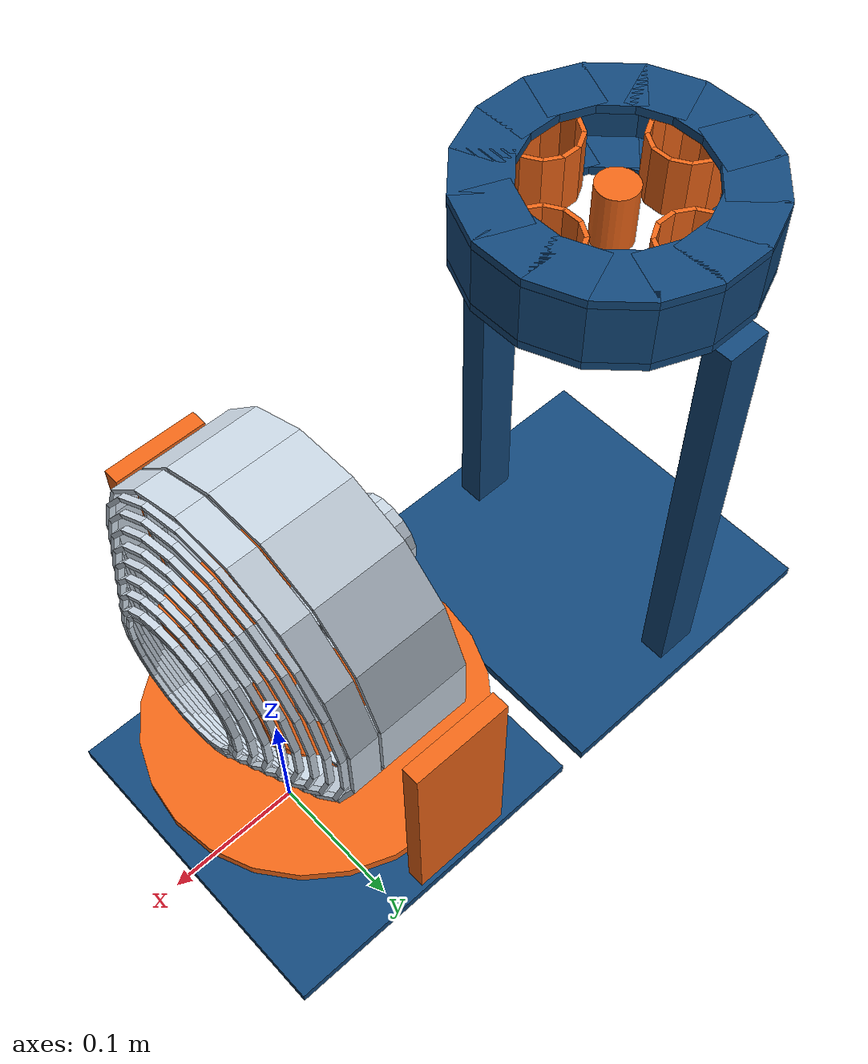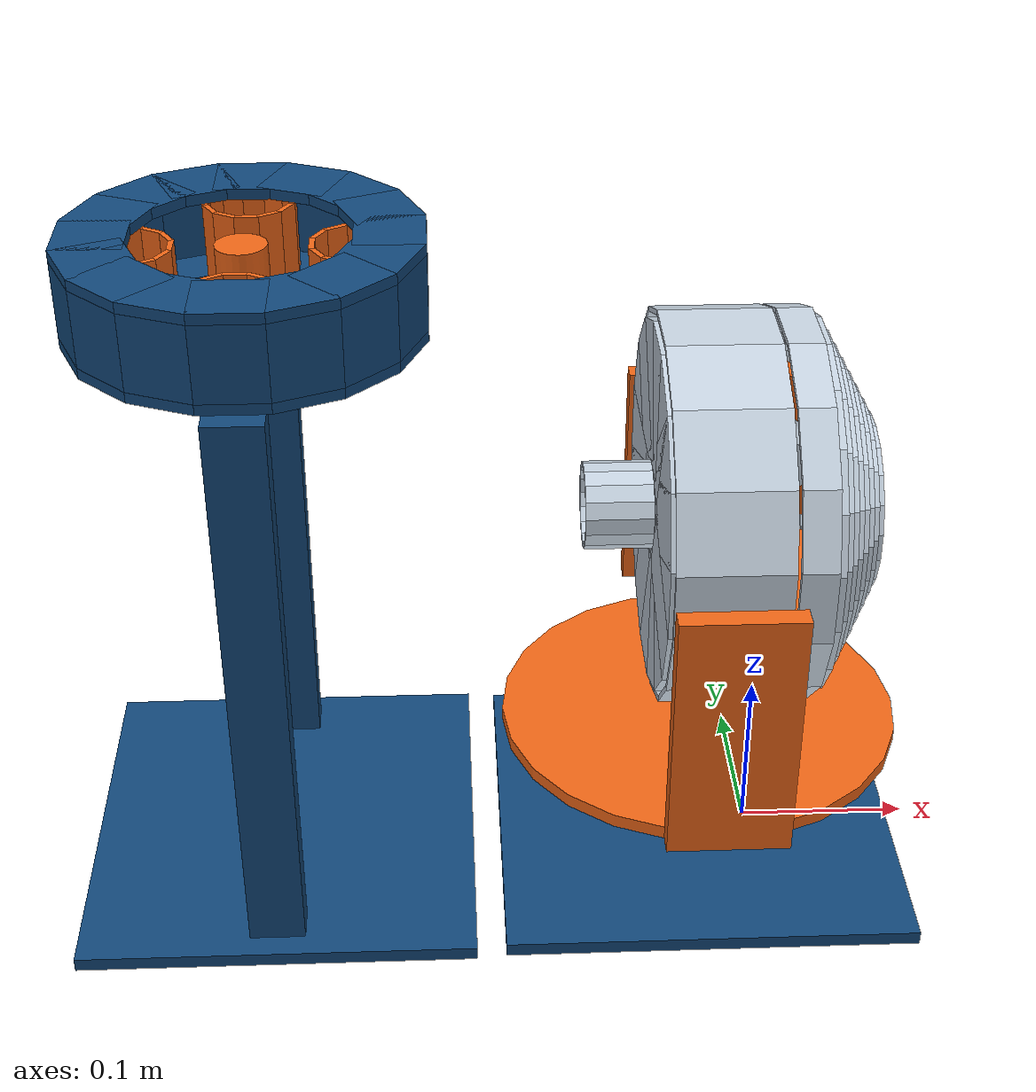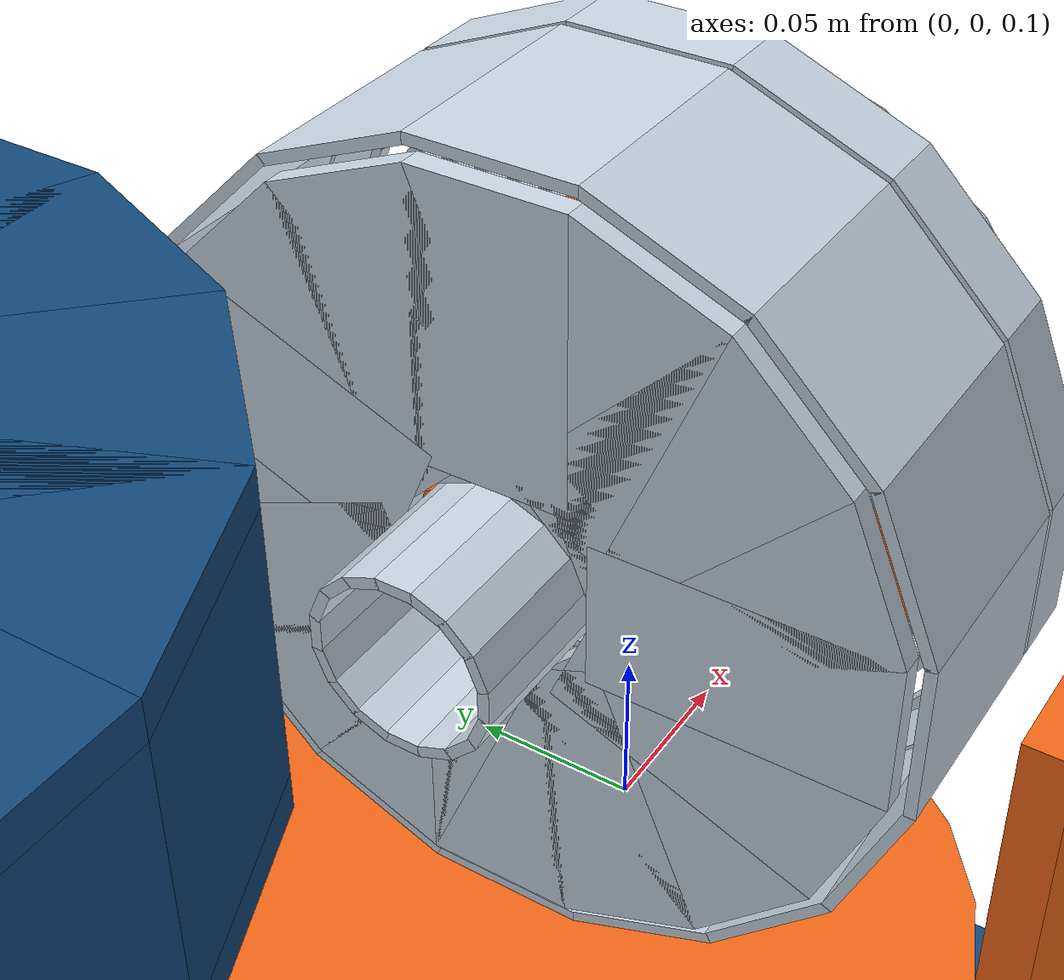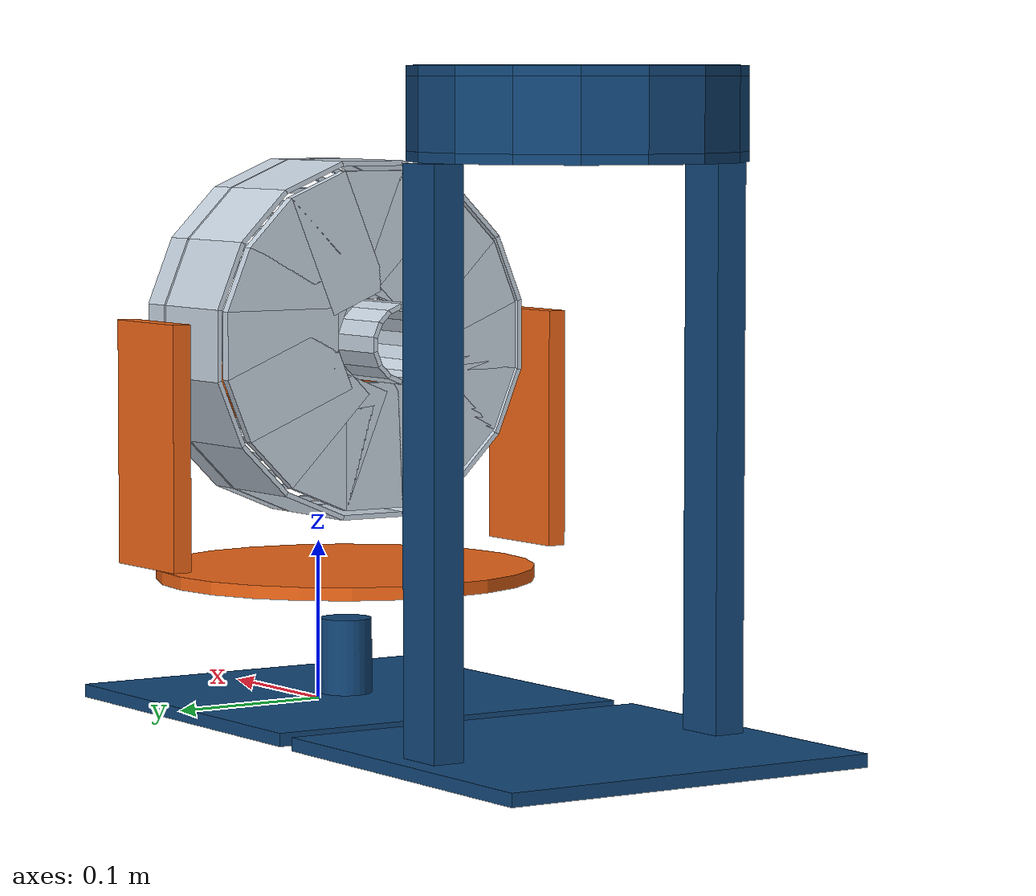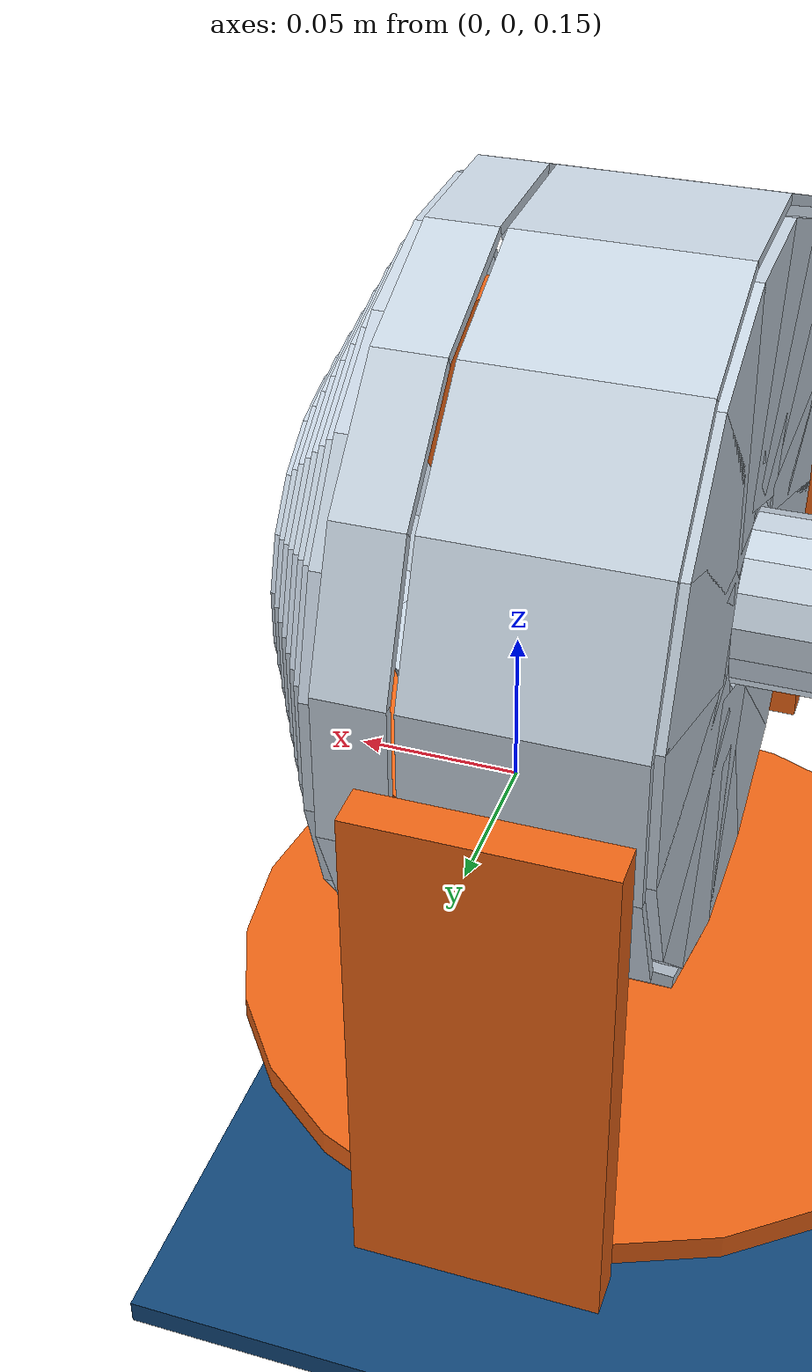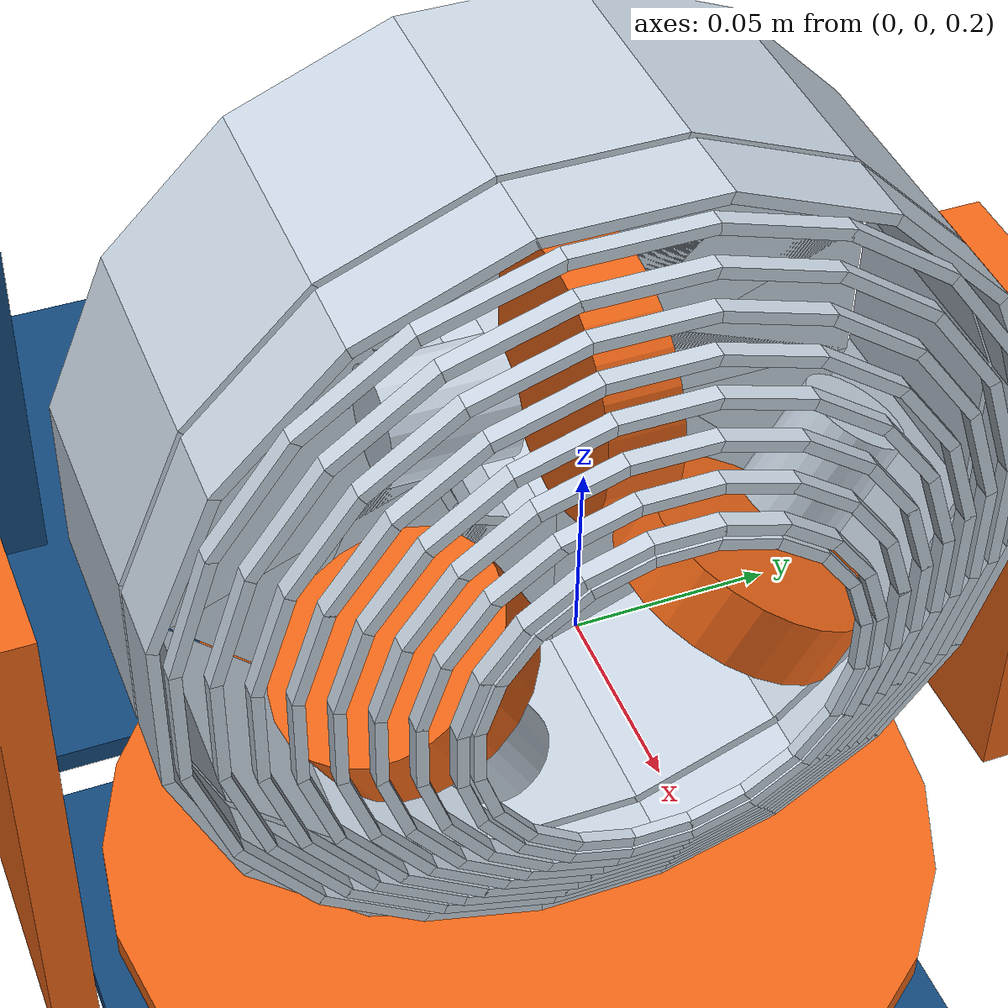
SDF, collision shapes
<?xml version='1.0' encoding='utf-8'?>
<sdf version="1.8">
  <model name="pingpong_launcher" canonical_link="base_link">
    <static>false</static>
    <self_collide>false</self_collide>
    <link name="base_link">
      <pose>0 0 0 0 0 0</pose>
      <self_collide>false</self_collide>
      <inertial>
        <pose>-0.19 0 0.22 0 0 0</pose>
        <mass>2.8</mass>
        <inertia>
          <ixx>0.0958066666667</ixx>
          <iyy>0.159716666667</iyy>
          <izz>0.0930766666667</izz>
          <ixy>0</ixy>
          <ixz>0</ixz>
          <iyz>0</iyz>
        </inertia>
      </inertial>
      <visual name="A03_Fixed_feeder_50mm_hose_spigot">
        <geometry>
          <mesh>
            <uri>model://pingpong_launcher/meshes/A03_Fixed_feeder_50mm_hose_spigot.stl</uri>
            <scale>1 1 1</scale>
          </mesh>
        </geometry>
        <material>
          <ambient>.07 .28 .48 1</ambient>
          <diffuse>.07 .28 .48 1</diffuse>
          <specular>.18 .18 .18 1</specular>
        </material>
      </visual>
      <visual name="A05_Yaw_base_and_bearing_tower">
        <geometry>
          <mesh>
            <uri>model://pingpong_launcher/meshes/A05_Yaw_base_and_bearing_tower.stl</uri>
            <scale>1 1 1</scale>
          </mesh>
        </geometry>
        <material>
          <ambient>.07 .28 .48 1</ambient>
          <diffuse>.07 .28 .48 1</diffuse>
          <specular>.18 .18 .18 1</specular>
        </material>
      </visual>
      <visual name="A06_NEMA17_yaw_motor_bridge">
        <geometry>
          <mesh>
            <uri>model://pingpong_launcher/meshes/A06_NEMA17_yaw_motor_bridge.stl</uri>
            <scale>1 1 1</scale>
          </mesh>
        </geometry>
        <material>
          <ambient>.07 .28 .48 1</ambient>
          <diffuse>.07 .28 .48 1</diffuse>
          <specular>.18 .18 .18 1</specular>
        </material>
      </visual>
      <visual name="A08_NEMA_yaw_pinion_18T_module2">
        <geometry>
          <mesh>
            <uri>model://pingpong_launcher/meshes/A08_NEMA_yaw_pinion_18T_module2.stl</uri>
            <scale>1 1 1</scale>
          </mesh>
        </geometry>
        <material>
          <ambient>.94 .40 .09 1</ambient>
          <diffuse>.94 .40 .09 1</diffuse>
          <specular>.18 .18 .18 1</specular>
        </material>
      </visual>
      <visual name="A16_Flush_lower_yaw_bearing_retainer">
        <geometry>
          <mesh>
            <uri>model://pingpong_launcher/meshes/A16_Flush_lower_yaw_bearing_retainer.stl</uri>
            <scale>1 1 1</scale>
          </mesh>
        </geometry>
        <material>
          <ambient>.07 .28 .48 1</ambient>
          <diffuse>.07 .28 .48 1</diffuse>
          <specular>.18 .18 .18 1</specular>
        </material>
      </visual>
      <visual name="F01_Feeder_pan_-_46mm_discharge">
        <geometry>
          <mesh>
            <uri>model://pingpong_launcher/meshes/F01_Feeder_pan_-_46mm_discharge.stl</uri>
            <scale>1 1 1</scale>
          </mesh>
        </geometry>
        <material>
          <ambient>.78 .83 .88 1</ambient>
          <diffuse>.78 .83 .88 1</diffuse>
          <specular>.18 .18 .18 1</specular>
        </material>
      </visual>
      <visual name="F02_Loading_cover_-_isolates_outlet">
        <geometry>
          <mesh>
            <uri>model://pingpong_launcher/meshes/F02_Loading_cover_-_isolates_outlet.stl</uri>
            <scale>1 1 1</scale>
          </mesh>
        </geometry>
        <material>
          <ambient>.78 .83 .88 1</ambient>
          <diffuse>.78 .83 .88 1</diffuse>
          <specular>.18 .18 .18 1</specular>
        </material>
      </visual>
      <visual name="F04_Basket_200x180_-_approximately_40_to_60_balls">
        <geometry>
          <mesh>
            <uri>model://pingpong_launcher/meshes/F04_Basket_200x180_-_approximately_40_to_60_balls.stl</uri>
            <scale>1 1 1</scale>
          </mesh>
        </geometry>
        <material>
          <ambient>.78 .83 .88 1</ambient>
          <diffuse>.78 .83 .88 1</diffuse>
          <specular>.18 .18 .18 1</specular>
        </material>
      </visual>
      <visual name="F07_Feeder_stand_base_-_230x244">
        <geometry>
          <mesh>
            <uri>model://pingpong_launcher/meshes/F07_Feeder_stand_base_-_230x244.stl</uri>
            <scale>1 1 1</scale>
          </mesh>
        </geometry>
        <material>
          <ambient>.07 .28 .48 1</ambient>
          <diffuse>.07 .28 .48 1</diffuse>
          <specular>.18 .18 .18 1</specular>
        </material>
      </visual>
      <visual name="F08_Stand_post_-9.8_0.8">
        <geometry>
          <mesh>
            <uri>model://pingpong_launcher/meshes/F08_Stand_post_-9.8_0.8.stl</uri>
            <scale>1 1 1</scale>
          </mesh>
        </geometry>
        <material>
          <ambient>.07 .28 .48 1</ambient>
          <diffuse>.07 .28 .48 1</diffuse>
          <specular>.18 .18 .18 1</specular>
        </material>
      </visual>
      <visual name="F08_Stand_post_-9.8_17.6">
        <geometry>
          <mesh>
            <uri>model://pingpong_launcher/meshes/F08_Stand_post_-9.8_17.6.stl</uri>
            <scale>1 1 1</scale>
          </mesh>
        </geometry>
        <material>
          <ambient>.07 .28 .48 1</ambient>
          <diffuse>.07 .28 .48 1</diffuse>
          <specular>.18 .18 .18 1</specular>
        </material>
      </visual>
      <visual name="F08_Stand_post_9.8_0.8">
        <geometry>
          <mesh>
            <uri>model://pingpong_launcher/meshes/F08_Stand_post_9.8_0.8.stl</uri>
            <scale>1 1 1</scale>
          </mesh>
        </geometry>
        <material>
          <ambient>.07 .28 .48 1</ambient>
          <diffuse>.07 .28 .48 1</diffuse>
          <specular>.18 .18 .18 1</specular>
        </material>
      </visual>
      <visual name="F08_Stand_post_9.8_17.6">
        <geometry>
          <mesh>
            <uri>model://pingpong_launcher/meshes/F08_Stand_post_9.8_17.6.stl</uri>
            <scale>1 1 1</scale>
          </mesh>
        </geometry>
        <material>
          <ambient>.07 .28 .48 1</ambient>
          <diffuse>.07 .28 .48 1</diffuse>
          <specular>.18 .18 .18 1</specular>
        </material>
      </visual>
      <visual name="yaw_stepper">
        <pose>0.057 0 0.0295 0 0 0</pose>
        <geometry>
          <box>
            <size>0.042 0.042 0.042</size>
          </box>
        </geometry>
        <material>
          <ambient>.09 .11 .14 1</ambient>
          <diffuse>.09 .11 .14 1</diffuse>
          <specular>.18 .18 .18 1</specular>
        </material>
      </visual>
      <visual name="feeder_stepper">
        <pose>-0.285 0 0.323 0 0 0</pose>
        <geometry>
          <box>
            <size>0.042 0.042 0.042</size>
          </box>
        </geometry>
        <material>
          <ambient>.09 .11 .14 1</ambient>
          <diffuse>.09 .11 .14 1</diffuse>
          <specular>.18 .18 .18 1</specular>
        </material>
      </visual>
      <collision name="base_foot">
        <pose>-0.033 0 0.004 0 0 0</pose>
        <geometry>
          <box>
            <size>0.24 0.24 0.008</size>
          </box>
        </geometry>
        <surface>
          <friction>
            <ode>
              <mu>0.6</mu>
              <mu2>0.6</mu2>
            </ode>
          </friction>
          <bounce>
            <restitution_coefficient>0.1</restitution_coefficient>
            <threshold>0.1</threshold>
          </bounce>
        </surface>
      </collision>
      <collision name="feeder_base">
        <pose>-0.285 0 0.004 0 0 0</pose>
        <geometry>
          <box>
            <size>0.23 0.244 0.008</size>
          </box>
        </geometry>
        <surface>
          <friction>
            <ode>
              <mu>0.6</mu>
              <mu2>0.6</mu2>
            </ode>
          </friction>
          <bounce>
            <restitution_coefficient>0.1</restitution_coefficient>
            <threshold>0.1</threshold>
          </bounce>
        </surface>
      </collision>
      <collision name="yaw_bearing_tower">
        <pose>-0.033 0 0.0315 0 0 0</pose>
        <geometry>
          <cylinder>
            <radius>0.016</radius>
            <length>0.047</length>
          </cylinder>
        </geometry>
        <surface>
          <friction>
            <ode>
              <mu>0.6</mu>
              <mu2>0.6</mu2>
            </ode>
          </friction>
          <bounce>
            <restitution_coefficient>0.1</restitution_coefficient>
            <threshold>0.1</threshold>
          </bounce>
        </surface>
      </collision>
      <collision name="feeder_post_-1">
        <pose>-0.285 -0.098 0.176 0 0 0</pose>
        <geometry>
          <box>
            <size>0.032 0.02 0.336</size>
          </box>
        </geometry>
        <surface>
          <friction>
            <ode>
              <mu>0.6</mu>
              <mu2>0.6</mu2>
            </ode>
          </friction>
          <bounce>
            <restitution_coefficient>0.1</restitution_coefficient>
            <threshold>0.1</threshold>
          </bounce>
        </surface>
      </collision>
      <collision name="feeder_post_1">
        <pose>-0.285 0.098 0.176 0 0 0</pose>
        <geometry>
          <box>
            <size>0.032 0.02 0.336</size>
          </box>
        </geometry>
        <surface>
          <friction>
            <ode>
              <mu>0.6</mu>
              <mu2>0.6</mu2>
            </ode>
          </friction>
          <bounce>
            <restitution_coefficient>0.1</restitution_coefficient>
            <threshold>0.1</threshold>
          </bounce>
        </surface>
      </collision>
      <collision name="feeder_pan_wall_00">
        <pose>-0.193 0 0.37135 0 0 0</pose>
        <geometry>
          <box>
            <size>0.008 0.0381911745369 0.0427</size>
          </box>
        </geometry>
        <surface>
          <friction>
            <ode>
              <mu>0.6</mu>
              <mu2>0.6</mu2>
            </ode>
          </friction>
          <bounce>
            <restitution_coefficient>0.1</restitution_coefficient>
            <threshold>0.1</threshold>
          </bounce>
        </surface>
      </collision>
      <collision name="feeder_pan_wall_01">
        <pose>-0.200003083009 0.0352068757776 0.37135 0 0 0.392699081699</pose>
        <geometry>
          <box>
            <size>0.008 0.0381911745369 0.0427</size>
          </box>
        </geometry>
        <surface>
          <friction>
            <ode>
              <mu>0.6</mu>
              <mu2>0.6</mu2>
            </ode>
          </friction>
          <bounce>
            <restitution_coefficient>0.1</restitution_coefficient>
            <threshold>0.1</threshold>
          </bounce>
        </surface>
      </collision>
      <collision name="feeder_pan_wall_02">
        <pose>-0.219946176131 0.0650538238692 0.37135 0 0 0.785398163397</pose>
        <geometry>
          <box>
            <size>0.008 0.0381911745369 0.0427</size>
          </box>
        </geometry>
        <surface>
          <friction>
            <ode>
              <mu>0.6</mu>
              <mu2>0.6</mu2>
            </ode>
          </friction>
          <bounce>
            <restitution_coefficient>0.1</restitution_coefficient>
            <threshold>0.1</threshold>
          </bounce>
        </surface>
      </collision>
      <collision name="feeder_pan_wall_03">
        <pose>-0.249793124222 0.084996916991 0.37135 0 0 1.1780972451</pose>
        <geometry>
          <box>
            <size>0.008 0.0381911745369 0.0427</size>
          </box>
        </geometry>
        <surface>
          <friction>
            <ode>
              <mu>0.6</mu>
              <mu2>0.6</mu2>
            </ode>
          </friction>
          <bounce>
            <restitution_coefficient>0.1</restitution_coefficient>
            <threshold>0.1</threshold>
          </bounce>
        </surface>
      </collision>
      <collision name="feeder_pan_wall_04">
        <pose>-0.285 0.092 0.37135 0 0 1.57079632679</pose>
        <geometry>
          <box>
            <size>0.008 0.0381911745369 0.0427</size>
          </box>
        </geometry>
        <surface>
          <friction>
            <ode>
              <mu>0.6</mu>
              <mu2>0.6</mu2>
            </ode>
          </friction>
          <bounce>
            <restitution_coefficient>0.1</restitution_coefficient>
            <threshold>0.1</threshold>
          </bounce>
        </surface>
      </collision>
      <collision name="feeder_pan_wall_05">
        <pose>-0.320206875778 0.084996916991 0.37135 0 0 1.96349540849</pose>
        <geometry>
          <box>
            <size>0.008 0.0381911745369 0.0427</size>
          </box>
        </geometry>
        <surface>
          <friction>
            <ode>
              <mu>0.6</mu>
              <mu2>0.6</mu2>
            </ode>
          </friction>
          <bounce>
            <restitution_coefficient>0.1</restitution_coefficient>
            <threshold>0.1</threshold>
          </bounce>
        </surface>
      </collision>
      <collision name="feeder_pan_wall_06">
        <pose>-0.350053823869 0.0650538238692 0.37135 0 0 2.35619449019</pose>
        <geometry>
          <box>
            <size>0.008 0.0381911745369 0.0427</size>
          </box>
        </geometry>
        <surface>
          <friction>
            <ode>
              <mu>0.6</mu>
              <mu2>0.6</mu2>
            </ode>
          </friction>
          <bounce>
            <restitution_coefficient>0.1</restitution_coefficient>
            <threshold>0.1</threshold>
          </bounce>
        </surface>
      </collision>
      <collision name="feeder_pan_wall_07">
        <pose>-0.369996916991 0.0352068757776 0.37135 0 0 2.74889357189</pose>
        <geometry>
          <box>
            <size>0.008 0.0381911745369 0.0427</size>
          </box>
        </geometry>
        <surface>
          <friction>
            <ode>
              <mu>0.6</mu>
              <mu2>0.6</mu2>
            </ode>
          </friction>
          <bounce>
            <restitution_coefficient>0.1</restitution_coefficient>
            <threshold>0.1</threshold>
          </bounce>
        </surface>
      </collision>
      <collision name="feeder_pan_wall_08">
        <pose>-0.377 1.12667505522e-17 0.37135 0 0 3.14159265359</pose>
        <geometry>
          <box>
            <size>0.008 0.0381911745369 0.0427</size>
          </box>
        </geometry>
        <surface>
          <friction>
            <ode>
              <mu>0.6</mu>
              <mu2>0.6</mu2>
            </ode>
          </friction>
          <bounce>
            <restitution_coefficient>0.1</restitution_coefficient>
            <threshold>0.1</threshold>
          </bounce>
        </surface>
      </collision>
      <collision name="feeder_pan_wall_09">
        <pose>-0.369996916991 -0.0352068757776 0.37135 0 0 3.53429173529</pose>
        <geometry>
          <box>
            <size>0.008 0.0381911745369 0.0427</size>
          </box>
        </geometry>
        <surface>
          <friction>
            <ode>
              <mu>0.6</mu>
              <mu2>0.6</mu2>
            </ode>
          </friction>
          <bounce>
            <restitution_coefficient>0.1</restitution_coefficient>
            <threshold>0.1</threshold>
          </bounce>
        </surface>
      </collision>
      <collision name="feeder_pan_wall_10">
        <pose>-0.350053823869 -0.0650538238692 0.37135 0 0 3.92699081699</pose>
        <geometry>
          <box>
            <size>0.008 0.0381911745369 0.0427</size>
          </box>
        </geometry>
        <surface>
          <friction>
            <ode>
              <mu>0.6</mu>
              <mu2>0.6</mu2>
            </ode>
          </friction>
          <bounce>
            <restitution_coefficient>0.1</restitution_coefficient>
            <threshold>0.1</threshold>
          </bounce>
        </surface>
      </collision>
      <collision name="feeder_pan_wall_11">
        <pose>-0.320206875778 -0.084996916991 0.37135 0 0 4.31968989869</pose>
        <geometry>
          <box>
            <size>0.008 0.0381911745369 0.0427</size>
          </box>
        </geometry>
        <surface>
          <friction>
            <ode>
              <mu>0.6</mu>
              <mu2>0.6</mu2>
            </ode>
          </friction>
          <bounce>
            <restitution_coefficient>0.1</restitution_coefficient>
            <threshold>0.1</threshold>
          </bounce>
        </surface>
      </collision>
      <collision name="feeder_pan_wall_12">
        <pose>-0.285 -0.092 0.37135 0 0 4.71238898038</pose>
        <geometry>
          <box>
            <size>0.008 0.0381911745369 0.0427</size>
          </box>
        </geometry>
        <surface>
          <friction>
            <ode>
              <mu>0.6</mu>
              <mu2>0.6</mu2>
            </ode>
          </friction>
          <bounce>
            <restitution_coefficient>0.1</restitution_coefficient>
            <threshold>0.1</threshold>
          </bounce>
        </surface>
      </collision>
      <collision name="feeder_pan_wall_13">
        <pose>-0.249793124222 -0.084996916991 0.37135 0 0 5.10508806208</pose>
        <geometry>
          <box>
            <size>0.008 0.0381911745369 0.0427</size>
          </box>
        </geometry>
        <surface>
          <friction>
            <ode>
              <mu>0.6</mu>
              <mu2>0.6</mu2>
            </ode>
          </friction>
          <bounce>
            <restitution_coefficient>0.1</restitution_coefficient>
            <threshold>0.1</threshold>
          </bounce>
        </surface>
      </collision>
      <collision name="feeder_pan_wall_14">
        <pose>-0.219946176131 -0.0650538238692 0.37135 0 0 5.49778714378</pose>
        <geometry>
          <box>
            <size>0.008 0.0381911745369 0.0427</size>
          </box>
        </geometry>
        <surface>
          <friction>
            <ode>
              <mu>0.6</mu>
              <mu2>0.6</mu2>
            </ode>
          </friction>
          <bounce>
            <restitution_coefficient>0.1</restitution_coefficient>
            <threshold>0.1</threshold>
          </bounce>
        </surface>
      </collision>
      <collision name="feeder_pan_wall_15">
        <pose>-0.200003083009 -0.0352068757776 0.37135 0 0 5.89048622548</pose>
        <geometry>
          <box>
            <size>0.008 0.0381911745369 0.0427</size>
          </box>
        </geometry>
        <surface>
          <friction>
            <ode>
              <mu>0.6</mu>
              <mu2>0.6</mu2>
            </ode>
          </friction>
          <bounce>
            <restitution_coefficient>0.1</restitution_coefficient>
            <threshold>0.1</threshold>
          </bounce>
        </surface>
      </collision>
      <collision name="pan_floor_00">
        <pose>-0.207 0 0.347 0 0 0</pose>
        <geometry>
          <box>
            <size>0.036 0.0381911745369 0.006</size>
          </box>
        </geometry>
        <surface>
          <friction>
            <ode>
              <mu>0.6</mu>
              <mu2>0.6</mu2>
            </ode>
          </friction>
          <bounce>
            <restitution_coefficient>0.1</restitution_coefficient>
            <threshold>0.1</threshold>
          </bounce>
        </surface>
      </collision>
      <collision name="pan_floor_01">
        <pose>-0.212937396464 0.0298493077245 0.347 0 0 0.392699081699</pose>
        <geometry>
          <box>
            <size>0.036 0.0381911745369 0.006</size>
          </box>
        </geometry>
        <surface>
          <friction>
            <ode>
              <mu>0.6</mu>
              <mu2>0.6</mu2>
            </ode>
          </friction>
          <bounce>
            <restitution_coefficient>0.1</restitution_coefficient>
            <threshold>0.1</threshold>
          </bounce>
        </surface>
      </collision>
      <collision name="pan_floor_02">
        <pose>-0.229845671067 0.0551543289326 0.347 0 0 0.785398163397</pose>
        <geometry>
          <box>
            <size>0.036 0.0381911745369 0.006</size>
          </box>
        </geometry>
        <surface>
          <friction>
            <ode>
              <mu>0.6</mu>
              <mu2>0.6</mu2>
            </ode>
          </friction>
          <bounce>
            <restitution_coefficient>0.1</restitution_coefficient>
            <threshold>0.1</threshold>
          </bounce>
        </surface>
      </collision>
      <collision name="pan_floor_03">
        <pose>-0.255150692276 0.0720626035359 0.347 0 0 1.1780972451</pose>
        <geometry>
          <box>
            <size>0.036 0.0381911745369 0.006</size>
          </box>
        </geometry>
        <surface>
          <friction>
            <ode>
              <mu>0.6</mu>
              <mu2>0.6</mu2>
            </ode>
          </friction>
          <bounce>
            <restitution_coefficient>0.1</restitution_coefficient>
            <threshold>0.1</threshold>
          </bounce>
        </surface>
      </collision>
      <collision name="pan_floor_04">
        <pose>-0.285 0.078 0.347 0 0 1.57079632679</pose>
        <geometry>
          <box>
            <size>0.036 0.0381911745369 0.006</size>
          </box>
        </geometry>
        <surface>
          <friction>
            <ode>
              <mu>0.6</mu>
              <mu2>0.6</mu2>
            </ode>
          </friction>
          <bounce>
            <restitution_coefficient>0.1</restitution_coefficient>
            <threshold>0.1</threshold>
          </bounce>
        </surface>
      </collision>
      <collision name="pan_floor_05">
        <pose>-0.314849307724 0.0720626035359 0.347 0 0 1.96349540849</pose>
        <geometry>
          <box>
            <size>0.036 0.0381911745369 0.006</size>
          </box>
        </geometry>
        <surface>
          <friction>
            <ode>
              <mu>0.6</mu>
              <mu2>0.6</mu2>
            </ode>
          </friction>
          <bounce>
            <restitution_coefficient>0.1</restitution_coefficient>
            <threshold>0.1</threshold>
          </bounce>
        </surface>
      </collision>
      <collision name="pan_floor_06">
        <pose>-0.340154328933 0.0551543289326 0.347 0 0 2.35619449019</pose>
        <geometry>
          <box>
            <size>0.036 0.0381911745369 0.006</size>
          </box>
        </geometry>
        <surface>
          <friction>
            <ode>
              <mu>0.6</mu>
              <mu2>0.6</mu2>
            </ode>
          </friction>
          <bounce>
            <restitution_coefficient>0.1</restitution_coefficient>
            <threshold>0.1</threshold>
          </bounce>
        </surface>
      </collision>
      <collision name="pan_floor_07">
        <pose>-0.357062603536 0.0298493077245 0.347 0 0 2.74889357189</pose>
        <geometry>
          <box>
            <size>0.036 0.0381911745369 0.006</size>
          </box>
        </geometry>
        <surface>
          <friction>
            <ode>
              <mu>0.6</mu>
              <mu2>0.6</mu2>
            </ode>
          </friction>
          <bounce>
            <restitution_coefficient>0.1</restitution_coefficient>
            <threshold>0.1</threshold>
          </bounce>
        </surface>
      </collision>
      <collision name="pan_floor_08">
        <pose>-0.363 9.55224503335e-18 0.347 0 0 3.14159265359</pose>
        <geometry>
          <box>
            <size>0.036 0.0381911745369 0.006</size>
          </box>
        </geometry>
        <surface>
          <friction>
            <ode>
              <mu>0.6</mu>
              <mu2>0.6</mu2>
            </ode>
          </friction>
          <bounce>
            <restitution_coefficient>0.1</restitution_coefficient>
            <threshold>0.1</threshold>
          </bounce>
        </surface>
      </collision>
      <collision name="pan_floor_09">
        <pose>-0.357062603536 -0.0298493077245 0.347 0 0 3.53429173529</pose>
        <geometry>
          <box>
            <size>0.036 0.0381911745369 0.006</size>
          </box>
        </geometry>
        <surface>
          <friction>
            <ode>
              <mu>0.6</mu>
              <mu2>0.6</mu2>
            </ode>
          </friction>
          <bounce>
            <restitution_coefficient>0.1</restitution_coefficient>
            <threshold>0.1</threshold>
          </bounce>
        </surface>
      </collision>
      <collision name="pan_floor_10">
        <pose>-0.340154328933 -0.0551543289326 0.347 0 0 3.92699081699</pose>
        <geometry>
          <box>
            <size>0.036 0.0381911745369 0.006</size>
          </box>
        </geometry>
        <surface>
          <friction>
            <ode>
              <mu>0.6</mu>
              <mu2>0.6</mu2>
            </ode>
          </friction>
          <bounce>
            <restitution_coefficient>0.1</restitution_coefficient>
            <threshold>0.1</threshold>
          </bounce>
        </surface>
      </collision>
      <collision name="pan_floor_11">
        <pose>-0.314849307724 -0.0720626035359 0.347 0 0 4.31968989869</pose>
        <geometry>
          <box>
            <size>0.036 0.0381911745369 0.006</size>
          </box>
        </geometry>
        <surface>
          <friction>
            <ode>
              <mu>0.6</mu>
              <mu2>0.6</mu2>
            </ode>
          </friction>
          <bounce>
            <restitution_coefficient>0.1</restitution_coefficient>
            <threshold>0.1</threshold>
          </bounce>
        </surface>
      </collision>
      <collision name="pan_floor_12">
        <pose>-0.285 -0.078 0.347 0 0 4.71238898038</pose>
        <geometry>
          <box>
            <size>0.036 0.0381911745369 0.006</size>
          </box>
        </geometry>
        <surface>
          <friction>
            <ode>
              <mu>0.6</mu>
              <mu2>0.6</mu2>
            </ode>
          </friction>
          <bounce>
            <restitution_coefficient>0.1</restitution_coefficient>
            <threshold>0.1</threshold>
          </bounce>
        </surface>
      </collision>
      <collision name="pan_floor_13">
        <pose>-0.255150692276 -0.0720626035359 0.347 0 0 5.10508806208</pose>
        <geometry>
          <box>
            <size>0.036 0.0381911745369 0.006</size>
          </box>
        </geometry>
        <surface>
          <friction>
            <ode>
              <mu>0.6</mu>
              <mu2>0.6</mu2>
            </ode>
          </friction>
          <bounce>
            <restitution_coefficient>0.1</restitution_coefficient>
            <threshold>0.1</threshold>
          </bounce>
        </surface>
      </collision>
      <collision name="pan_floor_14">
        <pose>-0.229845671067 -0.0551543289326 0.347 0 0 5.49778714378</pose>
        <geometry>
          <box>
            <size>0.036 0.0381911745369 0.006</size>
          </box>
        </geometry>
        <surface>
          <friction>
            <ode>
              <mu>0.6</mu>
              <mu2>0.6</mu2>
            </ode>
          </friction>
          <bounce>
            <restitution_coefficient>0.1</restitution_coefficient>
            <threshold>0.1</threshold>
          </bounce>
        </surface>
      </collision>
      <collision name="pan_floor_15">
        <pose>-0.212937396464 -0.0298493077245 0.347 0 0 5.89048622548</pose>
        <geometry>
          <box>
            <size>0.036 0.0381911745369 0.006</size>
          </box>
        </geometry>
        <surface>
          <friction>
            <ode>
              <mu>0.6</mu>
              <mu2>0.6</mu2>
            </ode>
          </friction>
          <bounce>
            <restitution_coefficient>0.1</restitution_coefficient>
            <threshold>0.1</threshold>
          </bounce>
        </surface>
      </collision>
      <collision name="feeder_lid_00">
        <pose>-0.208 0 0.3957 0 0 0</pose>
        <geometry>
          <box>
            <size>0.038 0.0381911745369 0.006</size>
          </box>
        </geometry>
        <surface>
          <friction>
            <ode>
              <mu>0.6</mu>
              <mu2>0.6</mu2>
            </ode>
          </friction>
          <bounce>
            <restitution_coefficient>0.1</restitution_coefficient>
            <threshold>0.1</threshold>
          </bounce>
        </surface>
      </collision>
      <collision name="feeder_lid_01">
        <pose>-0.213861275997 0.0294666242921 0.3957 0 0 0.392699081699</pose>
        <geometry>
          <box>
            <size>0.038 0.0381911745369 0.006</size>
          </box>
        </geometry>
        <surface>
          <friction>
            <ode>
              <mu>0.6</mu>
              <mu2>0.6</mu2>
            </ode>
          </friction>
          <bounce>
            <restitution_coefficient>0.1</restitution_coefficient>
            <threshold>0.1</threshold>
          </bounce>
        </surface>
      </collision>
      <collision name="feeder_lid_02">
        <pose>-0.230552777849 0.0544472221514 0.3957 0 0 0.785398163397</pose>
        <geometry>
          <box>
            <size>0.038 0.0381911745369 0.006</size>
          </box>
        </geometry>
        <surface>
          <friction>
            <ode>
              <mu>0.6</mu>
              <mu2>0.6</mu2>
            </ode>
          </friction>
          <bounce>
            <restitution_coefficient>0.1</restitution_coefficient>
            <threshold>0.1</threshold>
          </bounce>
        </surface>
      </collision>
      <collision name="feeder_lid_03">
        <pose>-0.255533375708 0.0711387240034 0.3957 0 0 1.1780972451</pose>
        <geometry>
          <box>
            <size>0.038 0.0381911745369 0.006</size>
          </box>
        </geometry>
        <surface>
          <friction>
            <ode>
              <mu>0.6</mu>
              <mu2>0.6</mu2>
            </ode>
          </friction>
          <bounce>
            <restitution_coefficient>0.1</restitution_coefficient>
            <threshold>0.1</threshold>
          </bounce>
        </surface>
      </collision>
      <collision name="feeder_lid_04">
        <pose>-0.285 0.077 0.3957 0 0 1.57079632679</pose>
        <geometry>
          <box>
            <size>0.038 0.0381911745369 0.006</size>
          </box>
        </geometry>
        <surface>
          <friction>
            <ode>
              <mu>0.6</mu>
              <mu2>0.6</mu2>
            </ode>
          </friction>
          <bounce>
            <restitution_coefficient>0.1</restitution_coefficient>
            <threshold>0.1</threshold>
          </bounce>
        </surface>
      </collision>
      <collision name="feeder_lid_05">
        <pose>-0.314466624292 0.0711387240034 0.3957 0 0 1.96349540849</pose>
        <geometry>
          <box>
            <size>0.038 0.0381911745369 0.006</size>
          </box>
        </geometry>
        <surface>
          <friction>
            <ode>
              <mu>0.6</mu>
              <mu2>0.6</mu2>
            </ode>
          </friction>
          <bounce>
            <restitution_coefficient>0.1</restitution_coefficient>
            <threshold>0.1</threshold>
          </bounce>
        </surface>
      </collision>
      <collision name="feeder_lid_06">
        <pose>-0.339447222151 0.0544472221514 0.3957 0 0 2.35619449019</pose>
        <geometry>
          <box>
            <size>0.038 0.0381911745369 0.006</size>
          </box>
        </geometry>
        <surface>
          <friction>
            <ode>
              <mu>0.6</mu>
              <mu2>0.6</mu2>
            </ode>
          </friction>
          <bounce>
            <restitution_coefficient>0.1</restitution_coefficient>
            <threshold>0.1</threshold>
          </bounce>
        </surface>
      </collision>
      <collision name="feeder_lid_07">
        <pose>-0.356138724003 0.0294666242921 0.3957 0 0 2.74889357189</pose>
        <geometry>
          <box>
            <size>0.038 0.0381911745369 0.006</size>
          </box>
        </geometry>
        <surface>
          <friction>
            <ode>
              <mu>0.6</mu>
              <mu2>0.6</mu2>
            </ode>
          </friction>
          <bounce>
            <restitution_coefficient>0.1</restitution_coefficient>
            <threshold>0.1</threshold>
          </bounce>
        </surface>
      </collision>
      <collision name="feeder_lid_08">
        <pose>-0.362 9.42978035343e-18 0.3957 0 0 3.14159265359</pose>
        <geometry>
          <box>
            <size>0.038 0.0381911745369 0.006</size>
          </box>
        </geometry>
        <surface>
          <friction>
            <ode>
              <mu>0.6</mu>
              <mu2>0.6</mu2>
            </ode>
          </friction>
          <bounce>
            <restitution_coefficient>0.1</restitution_coefficient>
            <threshold>0.1</threshold>
          </bounce>
        </surface>
      </collision>
      <collision name="feeder_lid_09">
        <pose>-0.356138724003 -0.0294666242921 0.3957 0 0 3.53429173529</pose>
        <geometry>
          <box>
            <size>0.038 0.0381911745369 0.006</size>
          </box>
        </geometry>
        <surface>
          <friction>
            <ode>
              <mu>0.6</mu>
              <mu2>0.6</mu2>
            </ode>
          </friction>
          <bounce>
            <restitution_coefficient>0.1</restitution_coefficient>
            <threshold>0.1</threshold>
          </bounce>
        </surface>
      </collision>
      <collision name="feeder_lid_10">
        <pose>-0.339447222151 -0.0544472221514 0.3957 0 0 3.92699081699</pose>
        <geometry>
          <box>
            <size>0.038 0.0381911745369 0.006</size>
          </box>
        </geometry>
        <surface>
          <friction>
            <ode>
              <mu>0.6</mu>
              <mu2>0.6</mu2>
            </ode>
          </friction>
          <bounce>
            <restitution_coefficient>0.1</restitution_coefficient>
            <threshold>0.1</threshold>
          </bounce>
        </surface>
      </collision>
      <collision name="feeder_lid_11">
        <pose>-0.314466624292 -0.0711387240034 0.3957 0 0 4.31968989869</pose>
        <geometry>
          <box>
            <size>0.038 0.0381911745369 0.006</size>
          </box>
        </geometry>
        <surface>
          <friction>
            <ode>
              <mu>0.6</mu>
              <mu2>0.6</mu2>
            </ode>
          </friction>
          <bounce>
            <restitution_coefficient>0.1</restitution_coefficient>
            <threshold>0.1</threshold>
          </bounce>
        </surface>
      </collision>
      <collision name="feeder_lid_12">
        <pose>-0.285 -0.077 0.3957 0 0 4.71238898038</pose>
        <geometry>
          <box>
            <size>0.038 0.0381911745369 0.006</size>
          </box>
        </geometry>
        <surface>
          <friction>
            <ode>
              <mu>0.6</mu>
              <mu2>0.6</mu2>
            </ode>
          </friction>
          <bounce>
            <restitution_coefficient>0.1</restitution_coefficient>
            <threshold>0.1</threshold>
          </bounce>
        </surface>
      </collision>
      <collision name="feeder_lid_13">
        <pose>-0.255533375708 -0.0711387240034 0.3957 0 0 5.10508806208</pose>
        <geometry>
          <box>
            <size>0.038 0.0381911745369 0.006</size>
          </box>
        </geometry>
        <surface>
          <friction>
            <ode>
              <mu>0.6</mu>
              <mu2>0.6</mu2>
            </ode>
          </friction>
          <bounce>
            <restitution_coefficient>0.1</restitution_coefficient>
            <threshold>0.1</threshold>
          </bounce>
        </surface>
      </collision>
      <collision name="feeder_lid_14">
        <pose>-0.230552777849 -0.0544472221514 0.3957 0 0 5.49778714378</pose>
        <geometry>
          <box>
            <size>0.038 0.0381911745369 0.006</size>
          </box>
        </geometry>
        <surface>
          <friction>
            <ode>
              <mu>0.6</mu>
              <mu2>0.6</mu2>
            </ode>
          </friction>
          <bounce>
            <restitution_coefficient>0.1</restitution_coefficient>
            <threshold>0.1</threshold>
          </bounce>
        </surface>
      </collision>
      <collision name="feeder_lid_15">
        <pose>-0.213861275997 -0.0294666242921 0.3957 0 0 5.89048622548</pose>
        <geometry>
          <box>
            <size>0.038 0.0381911745369 0.006</size>
          </box>
        </geometry>
        <surface>
          <friction>
            <ode>
              <mu>0.6</mu>
              <mu2>0.6</mu2>
            </ode>
          </friction>
          <bounce>
            <restitution_coefficient>0.1</restitution_coefficient>
            <threshold>0.1</threshold>
          </bounce>
        </surface>
      </collision>
    </link>
    <link name="yaw_link">
      <pose>-0.033 0 0.084 0 0 0</pose>
      <self_collide>false</self_collide>
      <inertial>
        <pose>0 0.012 0.035 0 0 0</pose>
        <mass>0.62</mass>
        <inertia>
          <ixx>0.00821629166667</ixx>
          <iyy>0.00504266666667</iyy>
          <izz>0.009125625</izz>
          <ixy>0</ixy>
          <ixz>0</ixz>
          <iyz>0</iyz>
        </inertia>
      </inertial>
      <visual name="A07_Yaw_turntable_72T_module2">
        <geometry>
          <mesh>
            <uri>model://pingpong_launcher/meshes/A07_Yaw_turntable_72T_module2.stl</uri>
            <scale>1 1 1</scale>
          </mesh>
        </geometry>
        <material>
          <ambient>.94 .40 .09 1</ambient>
          <diffuse>.94 .40 .09 1</diffuse>
          <specular>.18 .18 .18 1</specular>
        </material>
      </visual>
      <visual name="A09_Pitch_fork_arm_-1">
        <geometry>
          <mesh>
            <uri>model://pingpong_launcher/meshes/A09_Pitch_fork_arm_-1.stl</uri>
            <scale>1 1 1</scale>
          </mesh>
        </geometry>
        <material>
          <ambient>.07 .28 .48 1</ambient>
          <diffuse>.07 .28 .48 1</diffuse>
          <specular>.18 .18 .18 1</specular>
        </material>
      </visual>
      <visual name="A09_Pitch_fork_arm_1">
        <geometry>
          <mesh>
            <uri>model://pingpong_launcher/meshes/A09_Pitch_fork_arm_1.stl</uri>
            <scale>1 1 1</scale>
          </mesh>
        </geometry>
        <material>
          <ambient>.07 .28 .48 1</ambient>
          <diffuse>.07 .28 .48 1</diffuse>
          <specular>.18 .18 .18 1</specular>
        </material>
      </visual>
      <visual name="A10_MG996R_slotted_mounting_frame">
        <geometry>
          <mesh>
            <uri>model://pingpong_launcher/meshes/A10_MG996R_slotted_mounting_frame.stl</uri>
            <scale>1 1 1</scale>
          </mesh>
        </geometry>
        <material>
          <ambient>.07 .28 .48 1</ambient>
          <diffuse>.07 .28 .48 1</diffuse>
          <specular>.18 .18 .18 1</specular>
        </material>
      </visual>
      <visual name="A12_Servo_horn_pinion_30T_module1p5">
        <geometry>
          <mesh>
            <uri>model://pingpong_launcher/meshes/A12_Servo_horn_pinion_30T_module1p5.stl</uri>
            <scale>1 1 1</scale>
          </mesh>
        </geometry>
        <material>
          <ambient>.94 .40 .09 1</ambient>
          <diffuse>.94 .40 .09 1</diffuse>
          <specular>.18 .18 .18 1</specular>
        </material>
      </visual>
      <visual name="A13_Yaw_thrust_spacer_3mm">
        <geometry>
          <mesh>
            <uri>model://pingpong_launcher/meshes/A13_Yaw_thrust_spacer_3mm.stl</uri>
            <scale>1 1 1</scale>
          </mesh>
        </geometry>
        <material>
          <ambient>.07 .28 .48 1</ambient>
          <diffuse>.07 .28 .48 1</diffuse>
          <specular>.18 .18 .18 1</specular>
        </material>
      </visual>
      <visual name="pitch_servo">
        <pose>0 0.1755 0.06815 0 0 0</pose>
        <geometry>
          <box>
            <size>0.0197 0.037 0.0407</size>
          </box>
        </geometry>
        <material>
          <ambient>.09 .11 .14 1</ambient>
          <diffuse>.09 .11 .14 1</diffuse>
          <specular>.18 .18 .18 1</specular>
        </material>
      </visual>
      <visual name="yaw_shaft">
        <pose>0 0 -0.034 0 0 0</pose>
        <geometry>
          <cylinder>
            <radius>0.004</radius>
            <length>0.092</length>
          </cylinder>
        </geometry>
        <material>
          <ambient>.55 .58 .61 1</ambient>
          <diffuse>.55 .58 .61 1</diffuse>
          <specular>.18 .18 .18 1</specular>
        </material>
      </visual>
      <collision name="fork_-1">
        <pose>0 -0.136 0.0855 0 0 0</pose>
        <geometry>
          <box>
            <size>0.068 0.012 0.149</size>
          </box>
        </geometry>
        <surface>
          <friction>
            <ode>
              <mu>0.6</mu>
              <mu2>0.6</mu2>
            </ode>
          </friction>
          <bounce>
            <restitution_coefficient>0.1</restitution_coefficient>
            <threshold>0.1</threshold>
          </bounce>
        </surface>
      </collision>
      <collision name="fork_1">
        <pose>0 0.136 0.0855 0 0 0</pose>
        <geometry>
          <box>
            <size>0.068 0.012 0.149</size>
          </box>
        </geometry>
        <surface>
          <friction>
            <ode>
              <mu>0.6</mu>
              <mu2>0.6</mu2>
            </ode>
          </friction>
          <bounce>
            <restitution_coefficient>0.1</restitution_coefficient>
            <threshold>0.1</threshold>
          </bounce>
        </surface>
      </collision>
      <collision name="turntable">
        <pose>0 0 0 0 0 0</pose>
        <geometry>
          <cylinder>
            <radius>0.118</radius>
            <length>0.008</length>
          </cylinder>
        </geometry>
        <surface>
          <friction>
            <ode>
              <mu>0.6</mu>
              <mu2>0.6</mu2>
            </ode>
          </friction>
          <bounce>
            <restitution_coefficient>0.1</restitution_coefficient>
            <threshold>0.1</threshold>
          </bounce>
        </surface>
      </collision>
    </link>
    <link name="head_link">
      <pose relative_to="yaw_link">0 0 0.146 0 0 0</pose>
      <self_collide>false</self_collide>
      <inertial>
        <pose>0.005 0 0 0 0 0</pose>
        <mass>0.93</mass>
        <inertia>
          <ixx>0.008928</ixx>
          <iyy>0.006448</iyy>
          <izz>0.006448</izz>
          <ixy>0</ixy>
          <ixz>0</ixz>
          <iyz>0</iyz>
        </inertia>
      </inertial>
      <visual name="A02_Head_guide_and_50mm_hose_spigot">
        <geometry>
          <mesh>
            <uri>model://pingpong_launcher/meshes/A02_Head_guide_and_50mm_hose_spigot.stl</uri>
            <scale>1 1 1</scale>
          </mesh>
        </geometry>
        <material>
          <ambient>.78 .83 .88 1</ambient>
          <diffuse>.78 .83 .88 1</diffuse>
          <specular>.18 .18 .18 1</specular>
        </material>
      </visual>
      <visual name="A04_Head_clamp_half_1">
        <geometry>
          <mesh>
            <uri>model://pingpong_launcher/meshes/A04_Head_clamp_half_1.stl</uri>
            <scale>1 1 1</scale>
          </mesh>
        </geometry>
        <material>
          <ambient>.07 .28 .48 1</ambient>
          <diffuse>.07 .28 .48 1</diffuse>
          <specular>.18 .18 .18 1</specular>
        </material>
      </visual>
      <visual name="A04_Head_clamp_half_2">
        <geometry>
          <mesh>
            <uri>model://pingpong_launcher/meshes/A04_Head_clamp_half_2.stl</uri>
            <scale>1 1 1</scale>
          </mesh>
        </geometry>
        <material>
          <ambient>.07 .28 .48 1</ambient>
          <diffuse>.07 .28 .48 1</diffuse>
          <specular>.18 .18 .18 1</specular>
        </material>
      </visual>
      <visual name="A11_Pitch_gear_60T_module1p5">
        <geometry>
          <mesh>
            <uri>model://pingpong_launcher/meshes/A11_Pitch_gear_60T_module1p5.stl</uri>
            <scale>1 1 1</scale>
          </mesh>
        </geometry>
        <material>
          <ambient>.94 .40 .09 1</ambient>
          <diffuse>.94 .40 .09 1</diffuse>
          <specular>.18 .18 .18 1</specular>
        </material>
      </visual>
      <visual name="A14_Pitch_inner_spacer_-1">
        <geometry>
          <mesh>
            <uri>model://pingpong_launcher/meshes/A14_Pitch_inner_spacer_-1.stl</uri>
            <scale>1 1 1</scale>
          </mesh>
        </geometry>
        <material>
          <ambient>.07 .28 .48 1</ambient>
          <diffuse>.07 .28 .48 1</diffuse>
          <specular>.18 .18 .18 1</specular>
        </material>
      </visual>
      <visual name="A14_Pitch_inner_spacer_1">
        <geometry>
          <mesh>
            <uri>model://pingpong_launcher/meshes/A14_Pitch_inner_spacer_1.stl</uri>
            <scale>1 1 1</scale>
          </mesh>
        </geometry>
        <material>
          <ambient>.07 .28 .48 1</ambient>
          <diffuse>.07 .28 .48 1</diffuse>
          <specular>.18 .18 .18 1</specular>
        </material>
      </visual>
      <visual name="A15_Pitch_outer_spacer_-1">
        <geometry>
          <mesh>
            <uri>model://pingpong_launcher/meshes/A15_Pitch_outer_spacer_-1.stl</uri>
            <scale>1 1 1</scale>
          </mesh>
        </geometry>
        <material>
          <ambient>.07 .28 .48 1</ambient>
          <diffuse>.07 .28 .48 1</diffuse>
          <specular>.18 .18 .18 1</specular>
        </material>
      </visual>
      <visual name="A15_Pitch_outer_spacer_1">
        <geometry>
          <mesh>
            <uri>model://pingpong_launcher/meshes/A15_Pitch_outer_spacer_1.stl</uri>
            <scale>1 1 1</scale>
          </mesh>
        </geometry>
        <material>
          <ambient>.07 .28 .48 1</ambient>
          <diffuse>.07 .28 .48 1</diffuse>
          <specular>.18 .18 .18 1</specular>
        </material>
      </visual>
      <visual name="r5_front_cover">
        <geometry>
          <mesh>
            <uri>model://pingpong_launcher/meshes/r5_front_cover.stl</uri>
            <scale>1 1 1</scale>
          </mesh>
        </geometry>
        <material>
          <ambient>.78 .83 .88 1</ambient>
          <diffuse>.78 .83 .88 1</diffuse>
          <specular>.18 .18 .18 1</specular>
        </material>
      </visual>
      <visual name="rear_housing">
        <geometry>
          <mesh>
            <uri>model://pingpong_launcher/meshes/rear_housing.stl</uri>
            <scale>1 1 1</scale>
          </mesh>
        </geometry>
        <material>
          <ambient>.78 .83 .88 1</ambient>
          <diffuse>.78 .83 .88 1</diffuse>
          <specular>.18 .18 .18 1</specular>
        </material>
      </visual>
      <visual name="motor_1_bracket">
        <geometry>
          <mesh>
            <uri>model://pingpong_launcher/meshes/motor_1_bracket.stl</uri>
            <scale>1 1 1</scale>
          </mesh>
        </geometry>
        <material>
          <ambient>.07 .28 .48 1</ambient>
          <diffuse>.07 .28 .48 1</diffuse>
          <specular>.18 .18 .18 1</specular>
        </material>
      </visual>
      <visual name="motor_1_envelope">
        <pose>0.033 -0.036 0.052 0 -1.57079632679 -1.57079632679</pose>
        <geometry>
          <cylinder>
            <radius>0.014</radius>
            <length>0.03</length>
          </cylinder>
        </geometry>
        <material>
          <ambient>.55 .58 .61 1</ambient>
          <diffuse>.55 .58 .61 1</diffuse>
          <specular>.18 .18 .18 1</specular>
        </material>
      </visual>
      <collision name="motor_1_body_collision">
        <pose>0.033 -0.036 0.052 0 -1.57079632679 -1.57079632679</pose>
        <geometry>
          <cylinder>
            <radius>0.014</radius>
            <length>0.03</length>
          </cylinder>
        </geometry>
        <surface>
          <friction>
            <ode>
              <mu>0.6</mu>
              <mu2>0.6</mu2>
            </ode>
          </friction>
          <bounce>
            <restitution_coefficient>0.1</restitution_coefficient>
            <threshold>0.1</threshold>
          </bounce>
        </surface>
      </collision>
      <visual name="motor_2_bracket">
        <geometry>
          <mesh>
            <uri>model://pingpong_launcher/meshes/motor_2_bracket.stl</uri>
            <scale>1 1 1</scale>
          </mesh>
        </geometry>
        <material>
          <ambient>.07 .28 .48 1</ambient>
          <diffuse>.07 .28 .48 1</diffuse>
          <specular>.18 .18 .18 1</specular>
        </material>
      </visual>
      <visual name="motor_2_envelope">
        <pose>0.033 -0.0270333209968 -0.0571769145362 0 0.523598775598 -1.57079632679</pose>
        <geometry>
          <cylinder>
            <radius>0.014</radius>
            <length>0.03</length>
          </cylinder>
        </geometry>
        <material>
          <ambient>.55 .58 .61 1</ambient>
          <diffuse>.55 .58 .61 1</diffuse>
          <specular>.18 .18 .18 1</specular>
        </material>
      </visual>
      <collision name="motor_2_body_collision">
        <pose>0.033 -0.0270333209968 -0.0571769145362 0 0.523598775598 -1.57079632679</pose>
        <geometry>
          <cylinder>
            <radius>0.014</radius>
            <length>0.03</length>
          </cylinder>
        </geometry>
        <surface>
          <friction>
            <ode>
              <mu>0.6</mu>
              <mu2>0.6</mu2>
            </ode>
          </friction>
          <bounce>
            <restitution_coefficient>0.1</restitution_coefficient>
            <threshold>0.1</threshold>
          </bounce>
        </surface>
      </collision>
      <visual name="motor_3_bracket">
        <geometry>
          <mesh>
            <uri>model://pingpong_launcher/meshes/motor_3_bracket.stl</uri>
            <scale>1 1 1</scale>
          </mesh>
        </geometry>
        <material>
          <ambient>.07 .28 .48 1</ambient>
          <diffuse>.07 .28 .48 1</diffuse>
          <specular>.18 .18 .18 1</specular>
        </material>
      </visual>
      <visual name="motor_3_envelope">
        <pose>0.033 0.0630333209968 0.00517691453624 3.14159265359 0.523598775598 1.57079632679</pose>
        <geometry>
          <cylinder>
            <radius>0.014</radius>
            <length>0.03</length>
          </cylinder>
        </geometry>
        <material>
          <ambient>.55 .58 .61 1</ambient>
          <diffuse>.55 .58 .61 1</diffuse>
          <specular>.18 .18 .18 1</specular>
        </material>
      </visual>
      <collision name="motor_3_body_collision">
        <pose>0.033 0.0630333209968 0.00517691453624 3.14159265359 0.523598775598 1.57079632679</pose>
        <geometry>
          <cylinder>
            <radius>0.014</radius>
            <length>0.03</length>
          </cylinder>
        </geometry>
        <surface>
          <friction>
            <ode>
              <mu>0.6</mu>
              <mu2>0.6</mu2>
            </ode>
          </friction>
          <bounce>
            <restitution_coefficient>0.1</restitution_coefficient>
            <threshold>0.1</threshold>
          </bounce>
        </surface>
      </collision>
      <visual name="pitch_shaft">
        <pose>0 0 0 1.57079632679 0 0</pose>
        <geometry>
          <cylinder>
            <radius>0.004</radius>
            <length>0.315</length>
          </cylinder>
        </geometry>
        <material>
          <ambient>.55 .58 .61 1</ambient>
          <diffuse>.55 .58 .61 1</diffuse>
          <specular>.18 .18 .18 1</specular>
        </material>
      </visual>
      <collision name="rear_shell_00">
        <pose>-0.0005 0.1085 0 -1.57079632679 0 0</pose>
        <geometry>
          <box>
            <size>0.063 0.0437607208235 0.003</size>
          </box>
        </geometry>
        <surface>
          <friction>
            <ode>
              <mu>0.6</mu>
              <mu2>0.6</mu2>
            </ode>
          </friction>
          <bounce>
            <restitution_coefficient>0.1</restitution_coefficient>
            <threshold>0.1</threshold>
          </bounce>
        </surface>
      </collision>
      <collision name="rear_shell_01">
        <pose>-0.0005 0.100240929277 0.0415211524116 -1.1780972451 0 0</pose>
        <geometry>
          <box>
            <size>0.063 0.0437607208235 0.003</size>
          </box>
        </geometry>
        <surface>
          <friction>
            <ode>
              <mu>0.6</mu>
              <mu2>0.6</mu2>
            </ode>
          </friction>
          <bounce>
            <restitution_coefficient>0.1</restitution_coefficient>
            <threshold>0.1</threshold>
          </bounce>
        </surface>
      </collision>
      <collision name="rear_shell_02">
        <pose>-0.0005 0.0767210857587 0.0767210857587 -0.785398163397 0 0</pose>
        <geometry>
          <box>
            <size>0.063 0.0437607208235 0.003</size>
          </box>
        </geometry>
        <surface>
          <friction>
            <ode>
              <mu>0.6</mu>
              <mu2>0.6</mu2>
            </ode>
          </friction>
          <bounce>
            <restitution_coefficient>0.1</restitution_coefficient>
            <threshold>0.1</threshold>
          </bounce>
        </surface>
      </collision>
      <collision name="rear_shell_03">
        <pose>-0.0005 0.0415211524116 0.100240929277 -0.392699081699 0 0</pose>
        <geometry>
          <box>
            <size>0.063 0.0437607208235 0.003</size>
          </box>
        </geometry>
        <surface>
          <friction>
            <ode>
              <mu>0.6</mu>
              <mu2>0.6</mu2>
            </ode>
          </friction>
          <bounce>
            <restitution_coefficient>0.1</restitution_coefficient>
            <threshold>0.1</threshold>
          </bounce>
        </surface>
      </collision>
      <collision name="rear_shell_04">
        <pose>-0.0005 6.64370888537e-18 0.1085 0 0 0</pose>
        <geometry>
          <box>
            <size>0.063 0.0437607208235 0.003</size>
          </box>
        </geometry>
        <surface>
          <friction>
            <ode>
              <mu>0.6</mu>
              <mu2>0.6</mu2>
            </ode>
          </friction>
          <bounce>
            <restitution_coefficient>0.1</restitution_coefficient>
            <threshold>0.1</threshold>
          </bounce>
        </surface>
      </collision>
      <collision name="rear_shell_05">
        <pose>-0.0005 -0.0415211524116 0.100240929277 0.392699081699 0 0</pose>
        <geometry>
          <box>
            <size>0.063 0.0437607208235 0.003</size>
          </box>
        </geometry>
        <surface>
          <friction>
            <ode>
              <mu>0.6</mu>
              <mu2>0.6</mu2>
            </ode>
          </friction>
          <bounce>
            <restitution_coefficient>0.1</restitution_coefficient>
            <threshold>0.1</threshold>
          </bounce>
        </surface>
      </collision>
      <collision name="rear_shell_06">
        <pose>-0.0005 -0.0767210857587 0.0767210857587 0.785398163397 0 0</pose>
        <geometry>
          <box>
            <size>0.063 0.0437607208235 0.003</size>
          </box>
        </geometry>
        <surface>
          <friction>
            <ode>
              <mu>0.6</mu>
              <mu2>0.6</mu2>
            </ode>
          </friction>
          <bounce>
            <restitution_coefficient>0.1</restitution_coefficient>
            <threshold>0.1</threshold>
          </bounce>
        </surface>
      </collision>
      <collision name="rear_shell_07">
        <pose>-0.0005 -0.100240929277 0.0415211524116 1.1780972451 0 0</pose>
        <geometry>
          <box>
            <size>0.063 0.0437607208235 0.003</size>
          </box>
        </geometry>
        <surface>
          <friction>
            <ode>
              <mu>0.6</mu>
              <mu2>0.6</mu2>
            </ode>
          </friction>
          <bounce>
            <restitution_coefficient>0.1</restitution_coefficient>
            <threshold>0.1</threshold>
          </bounce>
        </surface>
      </collision>
      <collision name="rear_shell_08">
        <pose>-0.0005 -0.1085 1.32874177707e-17 1.57079632679 0 0</pose>
        <geometry>
          <box>
            <size>0.063 0.0437607208235 0.003</size>
          </box>
        </geometry>
        <surface>
          <friction>
            <ode>
              <mu>0.6</mu>
              <mu2>0.6</mu2>
            </ode>
          </friction>
          <bounce>
            <restitution_coefficient>0.1</restitution_coefficient>
            <threshold>0.1</threshold>
          </bounce>
        </surface>
      </collision>
      <collision name="rear_shell_09">
        <pose>-0.0005 -0.100240929277 -0.0415211524116 1.96349540849 0 0</pose>
        <geometry>
          <box>
            <size>0.063 0.0437607208235 0.003</size>
          </box>
        </geometry>
        <surface>
          <friction>
            <ode>
              <mu>0.6</mu>
              <mu2>0.6</mu2>
            </ode>
          </friction>
          <bounce>
            <restitution_coefficient>0.1</restitution_coefficient>
            <threshold>0.1</threshold>
          </bounce>
        </surface>
      </collision>
      <collision name="rear_shell_10">
        <pose>-0.0005 -0.0767210857587 -0.0767210857587 2.35619449019 0 0</pose>
        <geometry>
          <box>
            <size>0.063 0.0437607208235 0.003</size>
          </box>
        </geometry>
        <surface>
          <friction>
            <ode>
              <mu>0.6</mu>
              <mu2>0.6</mu2>
            </ode>
          </friction>
          <bounce>
            <restitution_coefficient>0.1</restitution_coefficient>
            <threshold>0.1</threshold>
          </bounce>
        </surface>
      </collision>
      <collision name="rear_shell_11">
        <pose>-0.0005 -0.0415211524116 -0.100240929277 2.74889357189 0 0</pose>
        <geometry>
          <box>
            <size>0.063 0.0437607208235 0.003</size>
          </box>
        </geometry>
        <surface>
          <friction>
            <ode>
              <mu>0.6</mu>
              <mu2>0.6</mu2>
            </ode>
          </friction>
          <bounce>
            <restitution_coefficient>0.1</restitution_coefficient>
            <threshold>0.1</threshold>
          </bounce>
        </surface>
      </collision>
      <collision name="rear_shell_12">
        <pose>-0.0005 -1.99311266561e-17 -0.1085 3.14159265359 0 0</pose>
        <geometry>
          <box>
            <size>0.063 0.0437607208235 0.003</size>
          </box>
        </geometry>
        <surface>
          <friction>
            <ode>
              <mu>0.6</mu>
              <mu2>0.6</mu2>
            </ode>
          </friction>
          <bounce>
            <restitution_coefficient>0.1</restitution_coefficient>
            <threshold>0.1</threshold>
          </bounce>
        </surface>
      </collision>
      <collision name="rear_shell_13">
        <pose>-0.0005 0.0415211524116 -0.100240929277 3.53429173529 0 0</pose>
        <geometry>
          <box>
            <size>0.063 0.0437607208235 0.003</size>
          </box>
        </geometry>
        <surface>
          <friction>
            <ode>
              <mu>0.6</mu>
              <mu2>0.6</mu2>
            </ode>
          </friction>
          <bounce>
            <restitution_coefficient>0.1</restitution_coefficient>
            <threshold>0.1</threshold>
          </bounce>
        </surface>
      </collision>
      <collision name="rear_shell_14">
        <pose>-0.0005 0.0767210857587 -0.0767210857587 3.92699081699 0 0</pose>
        <geometry>
          <box>
            <size>0.063 0.0437607208235 0.003</size>
          </box>
        </geometry>
        <surface>
          <friction>
            <ode>
              <mu>0.6</mu>
              <mu2>0.6</mu2>
            </ode>
          </friction>
          <bounce>
            <restitution_coefficient>0.1</restitution_coefficient>
            <threshold>0.1</threshold>
          </bounce>
        </surface>
      </collision>
      <collision name="rear_shell_15">
        <pose>-0.0005 0.100240929277 -0.0415211524116 4.31968989869 0 0</pose>
        <geometry>
          <box>
            <size>0.063 0.0437607208235 0.003</size>
          </box>
        </geometry>
        <surface>
          <friction>
            <ode>
              <mu>0.6</mu>
              <mu2>0.6</mu2>
            </ode>
          </friction>
          <bounce>
            <restitution_coefficient>0.1</restitution_coefficient>
            <threshold>0.1</threshold>
          </bounce>
        </surface>
      </collision>
      <collision name="rear_plate_00">
        <pose>-0.031 0.065 0 -1.57079632679 0 0</pose>
        <geometry>
          <box>
            <size>0.006 0.041373772415 0.078</size>
          </box>
        </geometry>
        <surface>
          <friction>
            <ode>
              <mu>0.6</mu>
              <mu2>0.6</mu2>
            </ode>
          </friction>
          <bounce>
            <restitution_coefficient>0.1</restitution_coefficient>
            <threshold>0.1</threshold>
          </bounce>
        </surface>
      </collision>
      <collision name="rear_plate_01">
        <pose>-0.031 0.0600521696132 0.0248744231037 -1.1780972451 0 0</pose>
        <geometry>
          <box>
            <size>0.006 0.041373772415 0.078</size>
          </box>
        </geometry>
        <surface>
          <friction>
            <ode>
              <mu>0.6</mu>
              <mu2>0.6</mu2>
            </ode>
          </friction>
          <bounce>
            <restitution_coefficient>0.1</restitution_coefficient>
            <threshold>0.1</threshold>
          </bounce>
        </surface>
      </collision>
      <collision name="rear_plate_02">
        <pose>-0.031 0.0459619407771 0.0459619407771 -0.785398163397 0 0</pose>
        <geometry>
          <box>
            <size>0.006 0.041373772415 0.078</size>
          </box>
        </geometry>
        <surface>
          <friction>
            <ode>
              <mu>0.6</mu>
              <mu2>0.6</mu2>
            </ode>
          </friction>
          <bounce>
            <restitution_coefficient>0.1</restitution_coefficient>
            <threshold>0.1</threshold>
          </bounce>
        </surface>
      </collision>
      <collision name="rear_plate_03">
        <pose>-0.031 0.0248744231037 0.0600521696132 -0.392699081699 0 0</pose>
        <geometry>
          <box>
            <size>0.006 0.041373772415 0.078</size>
          </box>
        </geometry>
        <surface>
          <friction>
            <ode>
              <mu>0.6</mu>
              <mu2>0.6</mu2>
            </ode>
          </friction>
          <bounce>
            <restitution_coefficient>0.1</restitution_coefficient>
            <threshold>0.1</threshold>
          </bounce>
        </surface>
      </collision>
      <collision name="rear_plate_04">
        <pose>-0.031 3.98010209723e-18 0.065 0 0 0</pose>
        <geometry>
          <box>
            <size>0.006 0.041373772415 0.078</size>
          </box>
        </geometry>
        <surface>
          <friction>
            <ode>
              <mu>0.6</mu>
              <mu2>0.6</mu2>
            </ode>
          </friction>
          <bounce>
            <restitution_coefficient>0.1</restitution_coefficient>
            <threshold>0.1</threshold>
          </bounce>
        </surface>
      </collision>
      <collision name="rear_plate_05">
        <pose>-0.031 -0.0248744231037 0.0600521696132 0.392699081699 0 0</pose>
        <geometry>
          <box>
            <size>0.006 0.041373772415 0.078</size>
          </box>
        </geometry>
        <surface>
          <friction>
            <ode>
              <mu>0.6</mu>
              <mu2>0.6</mu2>
            </ode>
          </friction>
          <bounce>
            <restitution_coefficient>0.1</restitution_coefficient>
            <threshold>0.1</threshold>
          </bounce>
        </surface>
      </collision>
      <collision name="rear_plate_06">
        <pose>-0.031 -0.0459619407771 0.0459619407771 0.785398163397 0 0</pose>
        <geometry>
          <box>
            <size>0.006 0.041373772415 0.078</size>
          </box>
        </geometry>
        <surface>
          <friction>
            <ode>
              <mu>0.6</mu>
              <mu2>0.6</mu2>
            </ode>
          </friction>
          <bounce>
            <restitution_coefficient>0.1</restitution_coefficient>
            <threshold>0.1</threshold>
          </bounce>
        </surface>
      </collision>
      <collision name="rear_plate_07">
        <pose>-0.031 -0.0600521696132 0.0248744231037 1.1780972451 0 0</pose>
        <geometry>
          <box>
            <size>0.006 0.041373772415 0.078</size>
          </box>
        </geometry>
        <surface>
          <friction>
            <ode>
              <mu>0.6</mu>
              <mu2>0.6</mu2>
            </ode>
          </friction>
          <bounce>
            <restitution_coefficient>0.1</restitution_coefficient>
            <threshold>0.1</threshold>
          </bounce>
        </surface>
      </collision>
      <collision name="rear_plate_08">
        <pose>-0.031 -0.065 7.96020419446e-18 1.57079632679 0 0</pose>
        <geometry>
          <box>
            <size>0.006 0.041373772415 0.078</size>
          </box>
        </geometry>
        <surface>
          <friction>
            <ode>
              <mu>0.6</mu>
              <mu2>0.6</mu2>
            </ode>
          </friction>
          <bounce>
            <restitution_coefficient>0.1</restitution_coefficient>
            <threshold>0.1</threshold>
          </bounce>
        </surface>
      </collision>
      <collision name="rear_plate_09">
        <pose>-0.031 -0.0600521696132 -0.0248744231037 1.96349540849 0 0</pose>
        <geometry>
          <box>
            <size>0.006 0.041373772415 0.078</size>
          </box>
        </geometry>
        <surface>
          <friction>
            <ode>
              <mu>0.6</mu>
              <mu2>0.6</mu2>
            </ode>
          </friction>
          <bounce>
            <restitution_coefficient>0.1</restitution_coefficient>
            <threshold>0.1</threshold>
          </bounce>
        </surface>
      </collision>
      <collision name="rear_plate_10">
        <pose>-0.031 -0.0459619407771 -0.0459619407771 2.35619449019 0 0</pose>
        <geometry>
          <box>
            <size>0.006 0.041373772415 0.078</size>
          </box>
        </geometry>
        <surface>
          <friction>
            <ode>
              <mu>0.6</mu>
              <mu2>0.6</mu2>
            </ode>
          </friction>
          <bounce>
            <restitution_coefficient>0.1</restitution_coefficient>
            <threshold>0.1</threshold>
          </bounce>
        </surface>
      </collision>
      <collision name="rear_plate_11">
        <pose>-0.031 -0.0248744231037 -0.0600521696132 2.74889357189 0 0</pose>
        <geometry>
          <box>
            <size>0.006 0.041373772415 0.078</size>
          </box>
        </geometry>
        <surface>
          <friction>
            <ode>
              <mu>0.6</mu>
              <mu2>0.6</mu2>
            </ode>
          </friction>
          <bounce>
            <restitution_coefficient>0.1</restitution_coefficient>
            <threshold>0.1</threshold>
          </bounce>
        </surface>
      </collision>
      <collision name="rear_plate_12">
        <pose>-0.031 -1.19403062917e-17 -0.065 3.14159265359 0 0</pose>
        <geometry>
          <box>
            <size>0.006 0.041373772415 0.078</size>
          </box>
        </geometry>
        <surface>
          <friction>
            <ode>
              <mu>0.6</mu>
              <mu2>0.6</mu2>
            </ode>
          </friction>
          <bounce>
            <restitution_coefficient>0.1</restitution_coefficient>
            <threshold>0.1</threshold>
          </bounce>
        </surface>
      </collision>
      <collision name="rear_plate_13">
        <pose>-0.031 0.0248744231037 -0.0600521696132 3.53429173529 0 0</pose>
        <geometry>
          <box>
            <size>0.006 0.041373772415 0.078</size>
          </box>
        </geometry>
        <surface>
          <friction>
            <ode>
              <mu>0.6</mu>
              <mu2>0.6</mu2>
            </ode>
          </friction>
          <bounce>
            <restitution_coefficient>0.1</restitution_coefficient>
            <threshold>0.1</threshold>
          </bounce>
        </surface>
      </collision>
      <collision name="rear_plate_14">
        <pose>-0.031 0.0459619407771 -0.0459619407771 3.92699081699 0 0</pose>
        <geometry>
          <box>
            <size>0.006 0.041373772415 0.078</size>
          </box>
        </geometry>
        <surface>
          <friction>
            <ode>
              <mu>0.6</mu>
              <mu2>0.6</mu2>
            </ode>
          </friction>
          <bounce>
            <restitution_coefficient>0.1</restitution_coefficient>
            <threshold>0.1</threshold>
          </bounce>
        </surface>
      </collision>
      <collision name="rear_plate_15">
        <pose>-0.031 0.0600521696132 -0.0248744231037 4.31968989869 0 0</pose>
        <geometry>
          <box>
            <size>0.006 0.041373772415 0.078</size>
          </box>
        </geometry>
        <surface>
          <friction>
            <ode>
              <mu>0.6</mu>
              <mu2>0.6</mu2>
            </ode>
          </friction>
          <bounce>
            <restitution_coefficient>0.1</restitution_coefficient>
            <threshold>0.1</threshold>
          </bounce>
        </surface>
      </collision>
      <collision name="front_collar_00">
        <pose>0.043 0.1085 0 -1.57079632679 0 0</pose>
        <geometry>
          <box>
            <size>0.02 0.0437607208235 0.003</size>
          </box>
        </geometry>
        <surface>
          <friction>
            <ode>
              <mu>0.6</mu>
              <mu2>0.6</mu2>
            </ode>
          </friction>
          <bounce>
            <restitution_coefficient>0.1</restitution_coefficient>
            <threshold>0.1</threshold>
          </bounce>
        </surface>
      </collision>
      <collision name="front_collar_01">
        <pose>0.043 0.100240929277 0.0415211524116 -1.1780972451 0 0</pose>
        <geometry>
          <box>
            <size>0.02 0.0437607208235 0.003</size>
          </box>
        </geometry>
        <surface>
          <friction>
            <ode>
              <mu>0.6</mu>
              <mu2>0.6</mu2>
            </ode>
          </friction>
          <bounce>
            <restitution_coefficient>0.1</restitution_coefficient>
            <threshold>0.1</threshold>
          </bounce>
        </surface>
      </collision>
      <collision name="front_collar_02">
        <pose>0.043 0.0767210857587 0.0767210857587 -0.785398163397 0 0</pose>
        <geometry>
          <box>
            <size>0.02 0.0437607208235 0.003</size>
          </box>
        </geometry>
        <surface>
          <friction>
            <ode>
              <mu>0.6</mu>
              <mu2>0.6</mu2>
            </ode>
          </friction>
          <bounce>
            <restitution_coefficient>0.1</restitution_coefficient>
            <threshold>0.1</threshold>
          </bounce>
        </surface>
      </collision>
      <collision name="front_collar_03">
        <pose>0.043 0.0415211524116 0.100240929277 -0.392699081699 0 0</pose>
        <geometry>
          <box>
            <size>0.02 0.0437607208235 0.003</size>
          </box>
        </geometry>
        <surface>
          <friction>
            <ode>
              <mu>0.6</mu>
              <mu2>0.6</mu2>
            </ode>
          </friction>
          <bounce>
            <restitution_coefficient>0.1</restitution_coefficient>
            <threshold>0.1</threshold>
          </bounce>
        </surface>
      </collision>
      <collision name="front_collar_04">
        <pose>0.043 6.64370888537e-18 0.1085 0 0 0</pose>
        <geometry>
          <box>
            <size>0.02 0.0437607208235 0.003</size>
          </box>
        </geometry>
        <surface>
          <friction>
            <ode>
              <mu>0.6</mu>
              <mu2>0.6</mu2>
            </ode>
          </friction>
          <bounce>
            <restitution_coefficient>0.1</restitution_coefficient>
            <threshold>0.1</threshold>
          </bounce>
        </surface>
      </collision>
      <collision name="front_collar_05">
        <pose>0.043 -0.0415211524116 0.100240929277 0.392699081699 0 0</pose>
        <geometry>
          <box>
            <size>0.02 0.0437607208235 0.003</size>
          </box>
        </geometry>
        <surface>
          <friction>
            <ode>
              <mu>0.6</mu>
              <mu2>0.6</mu2>
            </ode>
          </friction>
          <bounce>
            <restitution_coefficient>0.1</restitution_coefficient>
            <threshold>0.1</threshold>
          </bounce>
        </surface>
      </collision>
      <collision name="front_collar_06">
        <pose>0.043 -0.0767210857587 0.0767210857587 0.785398163397 0 0</pose>
        <geometry>
          <box>
            <size>0.02 0.0437607208235 0.003</size>
          </box>
        </geometry>
        <surface>
          <friction>
            <ode>
              <mu>0.6</mu>
              <mu2>0.6</mu2>
            </ode>
          </friction>
          <bounce>
            <restitution_coefficient>0.1</restitution_coefficient>
            <threshold>0.1</threshold>
          </bounce>
        </surface>
      </collision>
      <collision name="front_collar_07">
        <pose>0.043 -0.100240929277 0.0415211524116 1.1780972451 0 0</pose>
        <geometry>
          <box>
            <size>0.02 0.0437607208235 0.003</size>
          </box>
        </geometry>
        <surface>
          <friction>
            <ode>
              <mu>0.6</mu>
              <mu2>0.6</mu2>
            </ode>
          </friction>
          <bounce>
            <restitution_coefficient>0.1</restitution_coefficient>
            <threshold>0.1</threshold>
          </bounce>
        </surface>
      </collision>
      <collision name="front_collar_08">
        <pose>0.043 -0.1085 1.32874177707e-17 1.57079632679 0 0</pose>
        <geometry>
          <box>
            <size>0.02 0.0437607208235 0.003</size>
          </box>
        </geometry>
        <surface>
          <friction>
            <ode>
              <mu>0.6</mu>
              <mu2>0.6</mu2>
            </ode>
          </friction>
          <bounce>
            <restitution_coefficient>0.1</restitution_coefficient>
            <threshold>0.1</threshold>
          </bounce>
        </surface>
      </collision>
      <collision name="front_collar_09">
        <pose>0.043 -0.100240929277 -0.0415211524116 1.96349540849 0 0</pose>
        <geometry>
          <box>
            <size>0.02 0.0437607208235 0.003</size>
          </box>
        </geometry>
        <surface>
          <friction>
            <ode>
              <mu>0.6</mu>
              <mu2>0.6</mu2>
            </ode>
          </friction>
          <bounce>
            <restitution_coefficient>0.1</restitution_coefficient>
            <threshold>0.1</threshold>
          </bounce>
        </surface>
      </collision>
      <collision name="front_collar_10">
        <pose>0.043 -0.0767210857587 -0.0767210857587 2.35619449019 0 0</pose>
        <geometry>
          <box>
            <size>0.02 0.0437607208235 0.003</size>
          </box>
        </geometry>
        <surface>
          <friction>
            <ode>
              <mu>0.6</mu>
              <mu2>0.6</mu2>
            </ode>
          </friction>
          <bounce>
            <restitution_coefficient>0.1</restitution_coefficient>
            <threshold>0.1</threshold>
          </bounce>
        </surface>
      </collision>
      <collision name="front_collar_11">
        <pose>0.043 -0.0415211524116 -0.100240929277 2.74889357189 0 0</pose>
        <geometry>
          <box>
            <size>0.02 0.0437607208235 0.003</size>
          </box>
        </geometry>
        <surface>
          <friction>
            <ode>
              <mu>0.6</mu>
              <mu2>0.6</mu2>
            </ode>
          </friction>
          <bounce>
            <restitution_coefficient>0.1</restitution_coefficient>
            <threshold>0.1</threshold>
          </bounce>
        </surface>
      </collision>
      <collision name="front_collar_12">
        <pose>0.043 -1.99311266561e-17 -0.1085 3.14159265359 0 0</pose>
        <geometry>
          <box>
            <size>0.02 0.0437607208235 0.003</size>
          </box>
        </geometry>
        <surface>
          <friction>
            <ode>
              <mu>0.6</mu>
              <mu2>0.6</mu2>
            </ode>
          </friction>
          <bounce>
            <restitution_coefficient>0.1</restitution_coefficient>
            <threshold>0.1</threshold>
          </bounce>
        </surface>
      </collision>
      <collision name="front_collar_13">
        <pose>0.043 0.0415211524116 -0.100240929277 3.53429173529 0 0</pose>
        <geometry>
          <box>
            <size>0.02 0.0437607208235 0.003</size>
          </box>
        </geometry>
        <surface>
          <friction>
            <ode>
              <mu>0.6</mu>
              <mu2>0.6</mu2>
            </ode>
          </friction>
          <bounce>
            <restitution_coefficient>0.1</restitution_coefficient>
            <threshold>0.1</threshold>
          </bounce>
        </surface>
      </collision>
      <collision name="front_collar_14">
        <pose>0.043 0.0767210857587 -0.0767210857587 3.92699081699 0 0</pose>
        <geometry>
          <box>
            <size>0.02 0.0437607208235 0.003</size>
          </box>
        </geometry>
        <surface>
          <friction>
            <ode>
              <mu>0.6</mu>
              <mu2>0.6</mu2>
            </ode>
          </friction>
          <bounce>
            <restitution_coefficient>0.1</restitution_coefficient>
            <threshold>0.1</threshold>
          </bounce>
        </surface>
      </collision>
      <collision name="front_collar_15">
        <pose>0.043 0.100240929277 -0.0415211524116 4.31968989869 0 0</pose>
        <geometry>
          <box>
            <size>0.02 0.0437607208235 0.003</size>
          </box>
        </geometry>
        <surface>
          <friction>
            <ode>
              <mu>0.6</mu>
              <mu2>0.6</mu2>
            </ode>
          </friction>
          <bounce>
            <restitution_coefficient>0.1</restitution_coefficient>
            <threshold>0.1</threshold>
          </bounce>
        </surface>
      </collision>
      <collision name="cover_taper_0_00">
        <pose>0.0551875 0.10509375 0 -1.57079632679 0 0</pose>
        <geometry>
          <box>
            <size>0.004375 0.0337655828717 0.003</size>
          </box>
        </geometry>
        <surface>
          <friction>
            <ode>
              <mu>0.6</mu>
              <mu2>0.6</mu2>
            </ode>
          </friction>
          <bounce>
            <restitution_coefficient>0.1</restitution_coefficient>
            <threshold>0.1</threshold>
          </bounce>
        </surface>
      </collision>
      <collision name="cover_taper_0_01">
        <pose>0.0551875 0.0999500957594 0.0324757547526 -1.25663706144 0 0</pose>
        <geometry>
          <box>
            <size>0.004375 0.0337655828717 0.003</size>
          </box>
        </geometry>
        <surface>
          <friction>
            <ode>
              <mu>0.6</mu>
              <mu2>0.6</mu2>
            </ode>
          </friction>
          <bounce>
            <restitution_coefficient>0.1</restitution_coefficient>
            <threshold>0.1</threshold>
          </bounce>
        </surface>
      </collision>
      <collision name="cover_taper_0_02">
        <pose>0.0551875 0.0850226297526 0.0617725563581 -0.942477796077 0 0</pose>
        <geometry>
          <box>
            <size>0.004375 0.0337655828717 0.003</size>
          </box>
        </geometry>
        <surface>
          <friction>
            <ode>
              <mu>0.6</mu>
              <mu2>0.6</mu2>
            </ode>
          </friction>
          <bounce>
            <restitution_coefficient>0.1</restitution_coefficient>
            <threshold>0.1</threshold>
          </bounce>
        </surface>
      </collision>
      <collision name="cover_taper_0_03">
        <pose>0.0551875 0.0617725563581 0.0850226297526 -0.628318530718 0 0</pose>
        <geometry>
          <box>
            <size>0.004375 0.0337655828717 0.003</size>
          </box>
        </geometry>
        <surface>
          <friction>
            <ode>
              <mu>0.6</mu>
              <mu2>0.6</mu2>
            </ode>
          </friction>
          <bounce>
            <restitution_coefficient>0.1</restitution_coefficient>
            <threshold>0.1</threshold>
          </bounce>
        </surface>
      </collision>
      <collision name="cover_taper_0_04">
        <pose>0.0551875 0.0324757547526 0.0999500957594 -0.314159265359 0 0</pose>
        <geometry>
          <box>
            <size>0.004375 0.0337655828717 0.003</size>
          </box>
        </geometry>
        <surface>
          <friction>
            <ode>
              <mu>0.6</mu>
              <mu2>0.6</mu2>
            </ode>
          </friction>
          <bounce>
            <restitution_coefficient>0.1</restitution_coefficient>
            <threshold>0.1</threshold>
          </bounce>
        </surface>
      </collision>
      <collision name="cover_taper_0_05">
        <pose>0.0551875 6.43513622739e-18 0.10509375 0 0 0</pose>
        <geometry>
          <box>
            <size>0.004375 0.0337655828717 0.003</size>
          </box>
        </geometry>
        <surface>
          <friction>
            <ode>
              <mu>0.6</mu>
              <mu2>0.6</mu2>
            </ode>
          </friction>
          <bounce>
            <restitution_coefficient>0.1</restitution_coefficient>
            <threshold>0.1</threshold>
          </bounce>
        </surface>
      </collision>
      <collision name="cover_taper_0_06">
        <pose>0.0551875 -0.0324757547526 0.0999500957594 0.314159265359 0 0</pose>
        <geometry>
          <box>
            <size>0.004375 0.0337655828717 0.003</size>
          </box>
        </geometry>
        <surface>
          <friction>
            <ode>
              <mu>0.6</mu>
              <mu2>0.6</mu2>
            </ode>
          </friction>
          <bounce>
            <restitution_coefficient>0.1</restitution_coefficient>
            <threshold>0.1</threshold>
          </bounce>
        </surface>
      </collision>
      <collision name="cover_taper_0_07">
        <pose>0.0551875 -0.0617725563581 0.0850226297526 0.628318530718 0 0</pose>
        <geometry>
          <box>
            <size>0.004375 0.0337655828717 0.003</size>
          </box>
        </geometry>
        <surface>
          <friction>
            <ode>
              <mu>0.6</mu>
              <mu2>0.6</mu2>
            </ode>
          </friction>
          <bounce>
            <restitution_coefficient>0.1</restitution_coefficient>
            <threshold>0.1</threshold>
          </bounce>
        </surface>
      </collision>
      <collision name="cover_taper_0_08">
        <pose>0.0551875 -0.0850226297526 0.0617725563581 0.942477796077 0 0</pose>
        <geometry>
          <box>
            <size>0.004375 0.0337655828717 0.003</size>
          </box>
        </geometry>
        <surface>
          <friction>
            <ode>
              <mu>0.6</mu>
              <mu2>0.6</mu2>
            </ode>
          </friction>
          <bounce>
            <restitution_coefficient>0.1</restitution_coefficient>
            <threshold>0.1</threshold>
          </bounce>
        </surface>
      </collision>
      <collision name="cover_taper_0_09">
        <pose>0.0551875 -0.0999500957594 0.0324757547526 1.25663706144 0 0</pose>
        <geometry>
          <box>
            <size>0.004375 0.0337655828717 0.003</size>
          </box>
        </geometry>
        <surface>
          <friction>
            <ode>
              <mu>0.6</mu>
              <mu2>0.6</mu2>
            </ode>
          </friction>
          <bounce>
            <restitution_coefficient>0.1</restitution_coefficient>
            <threshold>0.1</threshold>
          </bounce>
        </surface>
      </collision>
      <collision name="cover_taper_0_10">
        <pose>0.0551875 -0.10509375 1.28702724548e-17 1.57079632679 0 0</pose>
        <geometry>
          <box>
            <size>0.004375 0.0337655828717 0.003</size>
          </box>
        </geometry>
        <surface>
          <friction>
            <ode>
              <mu>0.6</mu>
              <mu2>0.6</mu2>
            </ode>
          </friction>
          <bounce>
            <restitution_coefficient>0.1</restitution_coefficient>
            <threshold>0.1</threshold>
          </bounce>
        </surface>
      </collision>
      <collision name="cover_taper_0_11">
        <pose>0.0551875 -0.0999500957594 -0.0324757547526 1.88495559215 0 0</pose>
        <geometry>
          <box>
            <size>0.004375 0.0337655828717 0.003</size>
          </box>
        </geometry>
        <surface>
          <friction>
            <ode>
              <mu>0.6</mu>
              <mu2>0.6</mu2>
            </ode>
          </friction>
          <bounce>
            <restitution_coefficient>0.1</restitution_coefficient>
            <threshold>0.1</threshold>
          </bounce>
        </surface>
      </collision>
      <collision name="cover_taper_0_12">
        <pose>0.0551875 -0.0850226297526 -0.0617725563581 2.19911485751 0 0</pose>
        <geometry>
          <box>
            <size>0.004375 0.0337655828717 0.003</size>
          </box>
        </geometry>
        <surface>
          <friction>
            <ode>
              <mu>0.6</mu>
              <mu2>0.6</mu2>
            </ode>
          </friction>
          <bounce>
            <restitution_coefficient>0.1</restitution_coefficient>
            <threshold>0.1</threshold>
          </bounce>
        </surface>
      </collision>
      <collision name="cover_taper_0_13">
        <pose>0.0551875 -0.0617725563581 -0.0850226297526 2.51327412287 0 0</pose>
        <geometry>
          <box>
            <size>0.004375 0.0337655828717 0.003</size>
          </box>
        </geometry>
        <surface>
          <friction>
            <ode>
              <mu>0.6</mu>
              <mu2>0.6</mu2>
            </ode>
          </friction>
          <bounce>
            <restitution_coefficient>0.1</restitution_coefficient>
            <threshold>0.1</threshold>
          </bounce>
        </surface>
      </collision>
      <collision name="cover_taper_0_14">
        <pose>0.0551875 -0.0324757547526 -0.0999500957594 2.82743338823 0 0</pose>
        <geometry>
          <box>
            <size>0.004375 0.0337655828717 0.003</size>
          </box>
        </geometry>
        <surface>
          <friction>
            <ode>
              <mu>0.6</mu>
              <mu2>0.6</mu2>
            </ode>
          </friction>
          <bounce>
            <restitution_coefficient>0.1</restitution_coefficient>
            <threshold>0.1</threshold>
          </bounce>
        </surface>
      </collision>
      <collision name="cover_taper_0_15">
        <pose>0.0551875 -1.93054086822e-17 -0.10509375 3.14159265359 0 0</pose>
        <geometry>
          <box>
            <size>0.004375 0.0337655828717 0.003</size>
          </box>
        </geometry>
        <surface>
          <friction>
            <ode>
              <mu>0.6</mu>
              <mu2>0.6</mu2>
            </ode>
          </friction>
          <bounce>
            <restitution_coefficient>0.1</restitution_coefficient>
            <threshold>0.1</threshold>
          </bounce>
        </surface>
      </collision>
      <collision name="cover_taper_0_16">
        <pose>0.0551875 0.0324757547526 -0.0999500957594 3.45575191895 0 0</pose>
        <geometry>
          <box>
            <size>0.004375 0.0337655828717 0.003</size>
          </box>
        </geometry>
        <surface>
          <friction>
            <ode>
              <mu>0.6</mu>
              <mu2>0.6</mu2>
            </ode>
          </friction>
          <bounce>
            <restitution_coefficient>0.1</restitution_coefficient>
            <threshold>0.1</threshold>
          </bounce>
        </surface>
      </collision>
      <collision name="cover_taper_0_17">
        <pose>0.0551875 0.0617725563581 -0.0850226297526 3.76991118431 0 0</pose>
        <geometry>
          <box>
            <size>0.004375 0.0337655828717 0.003</size>
          </box>
        </geometry>
        <surface>
          <friction>
            <ode>
              <mu>0.6</mu>
              <mu2>0.6</mu2>
            </ode>
          </friction>
          <bounce>
            <restitution_coefficient>0.1</restitution_coefficient>
            <threshold>0.1</threshold>
          </bounce>
        </surface>
      </collision>
      <collision name="cover_taper_0_18">
        <pose>0.0551875 0.0850226297526 -0.0617725563581 4.08407044967 0 0</pose>
        <geometry>
          <box>
            <size>0.004375 0.0337655828717 0.003</size>
          </box>
        </geometry>
        <surface>
          <friction>
            <ode>
              <mu>0.6</mu>
              <mu2>0.6</mu2>
            </ode>
          </friction>
          <bounce>
            <restitution_coefficient>0.1</restitution_coefficient>
            <threshold>0.1</threshold>
          </bounce>
        </surface>
      </collision>
      <collision name="cover_taper_0_19">
        <pose>0.0551875 0.0999500957594 -0.0324757547526 4.39822971503 0 0</pose>
        <geometry>
          <box>
            <size>0.004375 0.0337655828717 0.003</size>
          </box>
        </geometry>
        <surface>
          <friction>
            <ode>
              <mu>0.6</mu>
              <mu2>0.6</mu2>
            </ode>
          </friction>
          <bounce>
            <restitution_coefficient>0.1</restitution_coefficient>
            <threshold>0.1</threshold>
          </bounce>
        </surface>
      </collision>
      <collision name="cover_taper_1_00">
        <pose>0.0595625 0.09728125 0 -1.57079632679 0 0</pose>
        <geometry>
          <box>
            <size>0.004375 0.0312908259916 0.003</size>
          </box>
        </geometry>
        <surface>
          <friction>
            <ode>
              <mu>0.6</mu>
              <mu2>0.6</mu2>
            </ode>
          </friction>
          <bounce>
            <restitution_coefficient>0.1</restitution_coefficient>
            <threshold>0.1</threshold>
          </bounce>
        </surface>
      </collision>
      <collision name="cover_taper_1_01">
        <pose>0.0595625 0.0925199667258 0.030061559484 -1.25663706144 0 0</pose>
        <geometry>
          <box>
            <size>0.004375 0.0312908259916 0.003</size>
          </box>
        </geometry>
        <surface>
          <friction>
            <ode>
              <mu>0.6</mu>
              <mu2>0.6</mu2>
            </ode>
          </friction>
          <bounce>
            <restitution_coefficient>0.1</restitution_coefficient>
            <threshold>0.1</threshold>
          </bounce>
        </surface>
      </collision>
      <collision name="cover_taper_1_02">
        <pose>0.0595625 0.078702184484 0.0571804840746 -0.942477796077 0 0</pose>
        <geometry>
          <box>
            <size>0.004375 0.0312908259916 0.003</size>
          </box>
        </geometry>
        <surface>
          <friction>
            <ode>
              <mu>0.6</mu>
              <mu2>0.6</mu2>
            </ode>
          </friction>
          <bounce>
            <restitution_coefficient>0.1</restitution_coefficient>
            <threshold>0.1</threshold>
          </bounce>
        </surface>
      </collision>
      <collision name="cover_taper_1_03">
        <pose>0.0595625 0.0571804840746 0.078702184484 -0.628318530718 0 0</pose>
        <geometry>
          <box>
            <size>0.004375 0.0312908259916 0.003</size>
          </box>
        </geometry>
        <surface>
          <friction>
            <ode>
              <mu>0.6</mu>
              <mu2>0.6</mu2>
            </ode>
          </friction>
          <bounce>
            <restitution_coefficient>0.1</restitution_coefficient>
            <threshold>0.1</threshold>
          </bounce>
        </surface>
      </collision>
      <collision name="cover_taper_1_04">
        <pose>0.0595625 0.030061559484 0.0925199667258 -0.314159265359 0 0</pose>
        <geometry>
          <box>
            <size>0.004375 0.0312908259916 0.003</size>
          </box>
        </geometry>
        <surface>
          <friction>
            <ode>
              <mu>0.6</mu>
              <mu2>0.6</mu2>
            </ode>
          </friction>
          <bounce>
            <restitution_coefficient>0.1</restitution_coefficient>
            <threshold>0.1</threshold>
          </bounce>
        </surface>
      </collision>
      <collision name="cover_taper_1_05">
        <pose>0.0595625 5.95675857148e-18 0.09728125 0 0 0</pose>
        <geometry>
          <box>
            <size>0.004375 0.0312908259916 0.003</size>
          </box>
        </geometry>
        <surface>
          <friction>
            <ode>
              <mu>0.6</mu>
              <mu2>0.6</mu2>
            </ode>
          </friction>
          <bounce>
            <restitution_coefficient>0.1</restitution_coefficient>
            <threshold>0.1</threshold>
          </bounce>
        </surface>
      </collision>
      <collision name="cover_taper_1_06">
        <pose>0.0595625 -0.030061559484 0.0925199667258 0.314159265359 0 0</pose>
        <geometry>
          <box>
            <size>0.004375 0.0312908259916 0.003</size>
          </box>
        </geometry>
        <surface>
          <friction>
            <ode>
              <mu>0.6</mu>
              <mu2>0.6</mu2>
            </ode>
          </friction>
          <bounce>
            <restitution_coefficient>0.1</restitution_coefficient>
            <threshold>0.1</threshold>
          </bounce>
        </surface>
      </collision>
      <collision name="cover_taper_1_07">
        <pose>0.0595625 -0.0571804840746 0.078702184484 0.628318530718 0 0</pose>
        <geometry>
          <box>
            <size>0.004375 0.0312908259916 0.003</size>
          </box>
        </geometry>
        <surface>
          <friction>
            <ode>
              <mu>0.6</mu>
              <mu2>0.6</mu2>
            </ode>
          </friction>
          <bounce>
            <restitution_coefficient>0.1</restitution_coefficient>
            <threshold>0.1</threshold>
          </bounce>
        </surface>
      </collision>
      <collision name="cover_taper_1_08">
        <pose>0.0595625 -0.078702184484 0.0571804840746 0.942477796077 0 0</pose>
        <geometry>
          <box>
            <size>0.004375 0.0312908259916 0.003</size>
          </box>
        </geometry>
        <surface>
          <friction>
            <ode>
              <mu>0.6</mu>
              <mu2>0.6</mu2>
            </ode>
          </friction>
          <bounce>
            <restitution_coefficient>0.1</restitution_coefficient>
            <threshold>0.1</threshold>
          </bounce>
        </surface>
      </collision>
      <collision name="cover_taper_1_09">
        <pose>0.0595625 -0.0925199667258 0.030061559484 1.25663706144 0 0</pose>
        <geometry>
          <box>
            <size>0.004375 0.0312908259916 0.003</size>
          </box>
        </geometry>
        <surface>
          <friction>
            <ode>
              <mu>0.6</mu>
              <mu2>0.6</mu2>
            </ode>
          </friction>
          <bounce>
            <restitution_coefficient>0.1</restitution_coefficient>
            <threshold>0.1</threshold>
          </bounce>
        </surface>
      </collision>
      <collision name="cover_taper_1_10">
        <pose>0.0595625 -0.09728125 1.1913517143e-17 1.57079632679 0 0</pose>
        <geometry>
          <box>
            <size>0.004375 0.0312908259916 0.003</size>
          </box>
        </geometry>
        <surface>
          <friction>
            <ode>
              <mu>0.6</mu>
              <mu2>0.6</mu2>
            </ode>
          </friction>
          <bounce>
            <restitution_coefficient>0.1</restitution_coefficient>
            <threshold>0.1</threshold>
          </bounce>
        </surface>
      </collision>
      <collision name="cover_taper_1_11">
        <pose>0.0595625 -0.0925199667258 -0.030061559484 1.88495559215 0 0</pose>
        <geometry>
          <box>
            <size>0.004375 0.0312908259916 0.003</size>
          </box>
        </geometry>
        <surface>
          <friction>
            <ode>
              <mu>0.6</mu>
              <mu2>0.6</mu2>
            </ode>
          </friction>
          <bounce>
            <restitution_coefficient>0.1</restitution_coefficient>
            <threshold>0.1</threshold>
          </bounce>
        </surface>
      </collision>
      <collision name="cover_taper_1_12">
        <pose>0.0595625 -0.078702184484 -0.0571804840746 2.19911485751 0 0</pose>
        <geometry>
          <box>
            <size>0.004375 0.0312908259916 0.003</size>
          </box>
        </geometry>
        <surface>
          <friction>
            <ode>
              <mu>0.6</mu>
              <mu2>0.6</mu2>
            </ode>
          </friction>
          <bounce>
            <restitution_coefficient>0.1</restitution_coefficient>
            <threshold>0.1</threshold>
          </bounce>
        </surface>
      </collision>
      <collision name="cover_taper_1_13">
        <pose>0.0595625 -0.0571804840746 -0.078702184484 2.51327412287 0 0</pose>
        <geometry>
          <box>
            <size>0.004375 0.0312908259916 0.003</size>
          </box>
        </geometry>
        <surface>
          <friction>
            <ode>
              <mu>0.6</mu>
              <mu2>0.6</mu2>
            </ode>
          </friction>
          <bounce>
            <restitution_coefficient>0.1</restitution_coefficient>
            <threshold>0.1</threshold>
          </bounce>
        </surface>
      </collision>
      <collision name="cover_taper_1_14">
        <pose>0.0595625 -0.030061559484 -0.0925199667258 2.82743338823 0 0</pose>
        <geometry>
          <box>
            <size>0.004375 0.0312908259916 0.003</size>
          </box>
        </geometry>
        <surface>
          <friction>
            <ode>
              <mu>0.6</mu>
              <mu2>0.6</mu2>
            </ode>
          </friction>
          <bounce>
            <restitution_coefficient>0.1</restitution_coefficient>
            <threshold>0.1</threshold>
          </bounce>
        </surface>
      </collision>
      <collision name="cover_taper_1_15">
        <pose>0.0595625 -1.78702757144e-17 -0.09728125 3.14159265359 0 0</pose>
        <geometry>
          <box>
            <size>0.004375 0.0312908259916 0.003</size>
          </box>
        </geometry>
        <surface>
          <friction>
            <ode>
              <mu>0.6</mu>
              <mu2>0.6</mu2>
            </ode>
          </friction>
          <bounce>
            <restitution_coefficient>0.1</restitution_coefficient>
            <threshold>0.1</threshold>
          </bounce>
        </surface>
      </collision>
      <collision name="cover_taper_1_16">
        <pose>0.0595625 0.030061559484 -0.0925199667258 3.45575191895 0 0</pose>
        <geometry>
          <box>
            <size>0.004375 0.0312908259916 0.003</size>
          </box>
        </geometry>
        <surface>
          <friction>
            <ode>
              <mu>0.6</mu>
              <mu2>0.6</mu2>
            </ode>
          </friction>
          <bounce>
            <restitution_coefficient>0.1</restitution_coefficient>
            <threshold>0.1</threshold>
          </bounce>
        </surface>
      </collision>
      <collision name="cover_taper_1_17">
        <pose>0.0595625 0.0571804840746 -0.078702184484 3.76991118431 0 0</pose>
        <geometry>
          <box>
            <size>0.004375 0.0312908259916 0.003</size>
          </box>
        </geometry>
        <surface>
          <friction>
            <ode>
              <mu>0.6</mu>
              <mu2>0.6</mu2>
            </ode>
          </friction>
          <bounce>
            <restitution_coefficient>0.1</restitution_coefficient>
            <threshold>0.1</threshold>
          </bounce>
        </surface>
      </collision>
      <collision name="cover_taper_1_18">
        <pose>0.0595625 0.078702184484 -0.0571804840746 4.08407044967 0 0</pose>
        <geometry>
          <box>
            <size>0.004375 0.0312908259916 0.003</size>
          </box>
        </geometry>
        <surface>
          <friction>
            <ode>
              <mu>0.6</mu>
              <mu2>0.6</mu2>
            </ode>
          </friction>
          <bounce>
            <restitution_coefficient>0.1</restitution_coefficient>
            <threshold>0.1</threshold>
          </bounce>
        </surface>
      </collision>
      <collision name="cover_taper_1_19">
        <pose>0.0595625 0.0925199667258 -0.030061559484 4.39822971503 0 0</pose>
        <geometry>
          <box>
            <size>0.004375 0.0312908259916 0.003</size>
          </box>
        </geometry>
        <surface>
          <friction>
            <ode>
              <mu>0.6</mu>
              <mu2>0.6</mu2>
            </ode>
          </friction>
          <bounce>
            <restitution_coefficient>0.1</restitution_coefficient>
            <threshold>0.1</threshold>
          </bounce>
        </surface>
      </collision>
      <collision name="cover_taper_2_00">
        <pose>0.0639375 0.08946875 0 -1.57079632679 0 0</pose>
        <geometry>
          <box>
            <size>0.004375 0.0288160691115 0.003</size>
          </box>
        </geometry>
        <surface>
          <friction>
            <ode>
              <mu>0.6</mu>
              <mu2>0.6</mu2>
            </ode>
          </friction>
          <bounce>
            <restitution_coefficient>0.1</restitution_coefficient>
            <threshold>0.1</threshold>
          </bounce>
        </surface>
      </collision>
      <collision name="cover_taper_2_01">
        <pose>0.0639375 0.0850898376923 0.0276473642155 -1.25663706144 0 0</pose>
        <geometry>
          <box>
            <size>0.004375 0.0288160691115 0.003</size>
          </box>
        </geometry>
        <surface>
          <friction>
            <ode>
              <mu>0.6</mu>
              <mu2>0.6</mu2>
            </ode>
          </friction>
          <bounce>
            <restitution_coefficient>0.1</restitution_coefficient>
            <threshold>0.1</threshold>
          </bounce>
        </surface>
      </collision>
      <collision name="cover_taper_2_02">
        <pose>0.0639375 0.0723817392155 0.052588411791 -0.942477796077 0 0</pose>
        <geometry>
          <box>
            <size>0.004375 0.0288160691115 0.003</size>
          </box>
        </geometry>
        <surface>
          <friction>
            <ode>
              <mu>0.6</mu>
              <mu2>0.6</mu2>
            </ode>
          </friction>
          <bounce>
            <restitution_coefficient>0.1</restitution_coefficient>
            <threshold>0.1</threshold>
          </bounce>
        </surface>
      </collision>
      <collision name="cover_taper_2_03">
        <pose>0.0639375 0.052588411791 0.0723817392155 -0.628318530718 0 0</pose>
        <geometry>
          <box>
            <size>0.004375 0.0288160691115 0.003</size>
          </box>
        </geometry>
        <surface>
          <friction>
            <ode>
              <mu>0.6</mu>
              <mu2>0.6</mu2>
            </ode>
          </friction>
          <bounce>
            <restitution_coefficient>0.1</restitution_coefficient>
            <threshold>0.1</threshold>
          </bounce>
        </surface>
      </collision>
      <collision name="cover_taper_2_04">
        <pose>0.0639375 0.0276473642155 0.0850898376923 -0.314159265359 0 0</pose>
        <geometry>
          <box>
            <size>0.004375 0.0288160691115 0.003</size>
          </box>
        </geometry>
        <surface>
          <friction>
            <ode>
              <mu>0.6</mu>
              <mu2>0.6</mu2>
            </ode>
          </friction>
          <bounce>
            <restitution_coefficient>0.1</restitution_coefficient>
            <threshold>0.1</threshold>
          </bounce>
        </surface>
      </collision>
      <collision name="cover_taper_2_05">
        <pose>0.0639375 5.47838091556e-18 0.08946875 0 0 0</pose>
        <geometry>
          <box>
            <size>0.004375 0.0288160691115 0.003</size>
          </box>
        </geometry>
        <surface>
          <friction>
            <ode>
              <mu>0.6</mu>
              <mu2>0.6</mu2>
            </ode>
          </friction>
          <bounce>
            <restitution_coefficient>0.1</restitution_coefficient>
            <threshold>0.1</threshold>
          </bounce>
        </surface>
      </collision>
      <collision name="cover_taper_2_06">
        <pose>0.0639375 -0.0276473642155 0.0850898376923 0.314159265359 0 0</pose>
        <geometry>
          <box>
            <size>0.004375 0.0288160691115 0.003</size>
          </box>
        </geometry>
        <surface>
          <friction>
            <ode>
              <mu>0.6</mu>
              <mu2>0.6</mu2>
            </ode>
          </friction>
          <bounce>
            <restitution_coefficient>0.1</restitution_coefficient>
            <threshold>0.1</threshold>
          </bounce>
        </surface>
      </collision>
      <collision name="cover_taper_2_07">
        <pose>0.0639375 -0.052588411791 0.0723817392155 0.628318530718 0 0</pose>
        <geometry>
          <box>
            <size>0.004375 0.0288160691115 0.003</size>
          </box>
        </geometry>
        <surface>
          <friction>
            <ode>
              <mu>0.6</mu>
              <mu2>0.6</mu2>
            </ode>
          </friction>
          <bounce>
            <restitution_coefficient>0.1</restitution_coefficient>
            <threshold>0.1</threshold>
          </bounce>
        </surface>
      </collision>
      <collision name="cover_taper_2_08">
        <pose>0.0639375 -0.0723817392155 0.052588411791 0.942477796077 0 0</pose>
        <geometry>
          <box>
            <size>0.004375 0.0288160691115 0.003</size>
          </box>
        </geometry>
        <surface>
          <friction>
            <ode>
              <mu>0.6</mu>
              <mu2>0.6</mu2>
            </ode>
          </friction>
          <bounce>
            <restitution_coefficient>0.1</restitution_coefficient>
            <threshold>0.1</threshold>
          </bounce>
        </surface>
      </collision>
      <collision name="cover_taper_2_09">
        <pose>0.0639375 -0.0850898376923 0.0276473642155 1.25663706144 0 0</pose>
        <geometry>
          <box>
            <size>0.004375 0.0288160691115 0.003</size>
          </box>
        </geometry>
        <surface>
          <friction>
            <ode>
              <mu>0.6</mu>
              <mu2>0.6</mu2>
            </ode>
          </friction>
          <bounce>
            <restitution_coefficient>0.1</restitution_coefficient>
            <threshold>0.1</threshold>
          </bounce>
        </surface>
      </collision>
      <collision name="cover_taper_2_10">
        <pose>0.0639375 -0.08946875 1.09567618311e-17 1.57079632679 0 0</pose>
        <geometry>
          <box>
            <size>0.004375 0.0288160691115 0.003</size>
          </box>
        </geometry>
        <surface>
          <friction>
            <ode>
              <mu>0.6</mu>
              <mu2>0.6</mu2>
            </ode>
          </friction>
          <bounce>
            <restitution_coefficient>0.1</restitution_coefficient>
            <threshold>0.1</threshold>
          </bounce>
        </surface>
      </collision>
      <collision name="cover_taper_2_11">
        <pose>0.0639375 -0.0850898376923 -0.0276473642155 1.88495559215 0 0</pose>
        <geometry>
          <box>
            <size>0.004375 0.0288160691115 0.003</size>
          </box>
        </geometry>
        <surface>
          <friction>
            <ode>
              <mu>0.6</mu>
              <mu2>0.6</mu2>
            </ode>
          </friction>
          <bounce>
            <restitution_coefficient>0.1</restitution_coefficient>
            <threshold>0.1</threshold>
          </bounce>
        </surface>
      </collision>
      <collision name="cover_taper_2_12">
        <pose>0.0639375 -0.0723817392155 -0.052588411791 2.19911485751 0 0</pose>
        <geometry>
          <box>
            <size>0.004375 0.0288160691115 0.003</size>
          </box>
        </geometry>
        <surface>
          <friction>
            <ode>
              <mu>0.6</mu>
              <mu2>0.6</mu2>
            </ode>
          </friction>
          <bounce>
            <restitution_coefficient>0.1</restitution_coefficient>
            <threshold>0.1</threshold>
          </bounce>
        </surface>
      </collision>
      <collision name="cover_taper_2_13">
        <pose>0.0639375 -0.052588411791 -0.0723817392155 2.51327412287 0 0</pose>
        <geometry>
          <box>
            <size>0.004375 0.0288160691115 0.003</size>
          </box>
        </geometry>
        <surface>
          <friction>
            <ode>
              <mu>0.6</mu>
              <mu2>0.6</mu2>
            </ode>
          </friction>
          <bounce>
            <restitution_coefficient>0.1</restitution_coefficient>
            <threshold>0.1</threshold>
          </bounce>
        </surface>
      </collision>
      <collision name="cover_taper_2_14">
        <pose>0.0639375 -0.0276473642155 -0.0850898376923 2.82743338823 0 0</pose>
        <geometry>
          <box>
            <size>0.004375 0.0288160691115 0.003</size>
          </box>
        </geometry>
        <surface>
          <friction>
            <ode>
              <mu>0.6</mu>
              <mu2>0.6</mu2>
            </ode>
          </friction>
          <bounce>
            <restitution_coefficient>0.1</restitution_coefficient>
            <threshold>0.1</threshold>
          </bounce>
        </surface>
      </collision>
      <collision name="cover_taper_2_15">
        <pose>0.0639375 -1.64351427467e-17 -0.08946875 3.14159265359 0 0</pose>
        <geometry>
          <box>
            <size>0.004375 0.0288160691115 0.003</size>
          </box>
        </geometry>
        <surface>
          <friction>
            <ode>
              <mu>0.6</mu>
              <mu2>0.6</mu2>
            </ode>
          </friction>
          <bounce>
            <restitution_coefficient>0.1</restitution_coefficient>
            <threshold>0.1</threshold>
          </bounce>
        </surface>
      </collision>
      <collision name="cover_taper_2_16">
        <pose>0.0639375 0.0276473642155 -0.0850898376923 3.45575191895 0 0</pose>
        <geometry>
          <box>
            <size>0.004375 0.0288160691115 0.003</size>
          </box>
        </geometry>
        <surface>
          <friction>
            <ode>
              <mu>0.6</mu>
              <mu2>0.6</mu2>
            </ode>
          </friction>
          <bounce>
            <restitution_coefficient>0.1</restitution_coefficient>
            <threshold>0.1</threshold>
          </bounce>
        </surface>
      </collision>
      <collision name="cover_taper_2_17">
        <pose>0.0639375 0.052588411791 -0.0723817392155 3.76991118431 0 0</pose>
        <geometry>
          <box>
            <size>0.004375 0.0288160691115 0.003</size>
          </box>
        </geometry>
        <surface>
          <friction>
            <ode>
              <mu>0.6</mu>
              <mu2>0.6</mu2>
            </ode>
          </friction>
          <bounce>
            <restitution_coefficient>0.1</restitution_coefficient>
            <threshold>0.1</threshold>
          </bounce>
        </surface>
      </collision>
      <collision name="cover_taper_2_18">
        <pose>0.0639375 0.0723817392155 -0.052588411791 4.08407044967 0 0</pose>
        <geometry>
          <box>
            <size>0.004375 0.0288160691115 0.003</size>
          </box>
        </geometry>
        <surface>
          <friction>
            <ode>
              <mu>0.6</mu>
              <mu2>0.6</mu2>
            </ode>
          </friction>
          <bounce>
            <restitution_coefficient>0.1</restitution_coefficient>
            <threshold>0.1</threshold>
          </bounce>
        </surface>
      </collision>
      <collision name="cover_taper_2_19">
        <pose>0.0639375 0.0850898376923 -0.0276473642155 4.39822971503 0 0</pose>
        <geometry>
          <box>
            <size>0.004375 0.0288160691115 0.003</size>
          </box>
        </geometry>
        <surface>
          <friction>
            <ode>
              <mu>0.6</mu>
              <mu2>0.6</mu2>
            </ode>
          </friction>
          <bounce>
            <restitution_coefficient>0.1</restitution_coefficient>
            <threshold>0.1</threshold>
          </bounce>
        </surface>
      </collision>
      <collision name="cover_taper_3_00">
        <pose>0.0683125 0.08165625 0 -1.57079632679 0 0</pose>
        <geometry>
          <box>
            <size>0.004375 0.0263413122315 0.003</size>
          </box>
        </geometry>
        <surface>
          <friction>
            <ode>
              <mu>0.6</mu>
              <mu2>0.6</mu2>
            </ode>
          </friction>
          <bounce>
            <restitution_coefficient>0.1</restitution_coefficient>
            <threshold>0.1</threshold>
          </bounce>
        </surface>
      </collision>
      <collision name="cover_taper_3_01">
        <pose>0.0683125 0.0776597086587 0.0252331689469 -1.25663706144 0 0</pose>
        <geometry>
          <box>
            <size>0.004375 0.0263413122315 0.003</size>
          </box>
        </geometry>
        <surface>
          <friction>
            <ode>
              <mu>0.6</mu>
              <mu2>0.6</mu2>
            </ode>
          </friction>
          <bounce>
            <restitution_coefficient>0.1</restitution_coefficient>
            <threshold>0.1</threshold>
          </bounce>
        </surface>
      </collision>
      <collision name="cover_taper_3_02">
        <pose>0.0683125 0.0660612939469 0.0479963395075 -0.942477796077 0 0</pose>
        <geometry>
          <box>
            <size>0.004375 0.0263413122315 0.003</size>
          </box>
        </geometry>
        <surface>
          <friction>
            <ode>
              <mu>0.6</mu>
              <mu2>0.6</mu2>
            </ode>
          </friction>
          <bounce>
            <restitution_coefficient>0.1</restitution_coefficient>
            <threshold>0.1</threshold>
          </bounce>
        </surface>
      </collision>
      <collision name="cover_taper_3_03">
        <pose>0.0683125 0.0479963395075 0.0660612939469 -0.628318530718 0 0</pose>
        <geometry>
          <box>
            <size>0.004375 0.0263413122315 0.003</size>
          </box>
        </geometry>
        <surface>
          <friction>
            <ode>
              <mu>0.6</mu>
              <mu2>0.6</mu2>
            </ode>
          </friction>
          <bounce>
            <restitution_coefficient>0.1</restitution_coefficient>
            <threshold>0.1</threshold>
          </bounce>
        </surface>
      </collision>
      <collision name="cover_taper_3_04">
        <pose>0.0683125 0.0252331689469 0.0776597086587 -0.314159265359 0 0</pose>
        <geometry>
          <box>
            <size>0.004375 0.0263413122315 0.003</size>
          </box>
        </geometry>
        <surface>
          <friction>
            <ode>
              <mu>0.6</mu>
              <mu2>0.6</mu2>
            </ode>
          </friction>
          <bounce>
            <restitution_coefficient>0.1</restitution_coefficient>
            <threshold>0.1</threshold>
          </bounce>
        </surface>
      </collision>
      <collision name="cover_taper_3_05">
        <pose>0.0683125 5.00000325964e-18 0.08165625 0 0 0</pose>
        <geometry>
          <box>
            <size>0.004375 0.0263413122315 0.003</size>
          </box>
        </geometry>
        <surface>
          <friction>
            <ode>
              <mu>0.6</mu>
              <mu2>0.6</mu2>
            </ode>
          </friction>
          <bounce>
            <restitution_coefficient>0.1</restitution_coefficient>
            <threshold>0.1</threshold>
          </bounce>
        </surface>
      </collision>
      <collision name="cover_taper_3_06">
        <pose>0.0683125 -0.0252331689469 0.0776597086587 0.314159265359 0 0</pose>
        <geometry>
          <box>
            <size>0.004375 0.0263413122315 0.003</size>
          </box>
        </geometry>
        <surface>
          <friction>
            <ode>
              <mu>0.6</mu>
              <mu2>0.6</mu2>
            </ode>
          </friction>
          <bounce>
            <restitution_coefficient>0.1</restitution_coefficient>
            <threshold>0.1</threshold>
          </bounce>
        </surface>
      </collision>
      <collision name="cover_taper_3_07">
        <pose>0.0683125 -0.0479963395075 0.0660612939469 0.628318530718 0 0</pose>
        <geometry>
          <box>
            <size>0.004375 0.0263413122315 0.003</size>
          </box>
        </geometry>
        <surface>
          <friction>
            <ode>
              <mu>0.6</mu>
              <mu2>0.6</mu2>
            </ode>
          </friction>
          <bounce>
            <restitution_coefficient>0.1</restitution_coefficient>
            <threshold>0.1</threshold>
          </bounce>
        </surface>
      </collision>
      <collision name="cover_taper_3_08">
        <pose>0.0683125 -0.0660612939469 0.0479963395075 0.942477796077 0 0</pose>
        <geometry>
          <box>
            <size>0.004375 0.0263413122315 0.003</size>
          </box>
        </geometry>
        <surface>
          <friction>
            <ode>
              <mu>0.6</mu>
              <mu2>0.6</mu2>
            </ode>
          </friction>
          <bounce>
            <restitution_coefficient>0.1</restitution_coefficient>
            <threshold>0.1</threshold>
          </bounce>
        </surface>
      </collision>
      <collision name="cover_taper_3_09">
        <pose>0.0683125 -0.0776597086587 0.0252331689469 1.25663706144 0 0</pose>
        <geometry>
          <box>
            <size>0.004375 0.0263413122315 0.003</size>
          </box>
        </geometry>
        <surface>
          <friction>
            <ode>
              <mu>0.6</mu>
              <mu2>0.6</mu2>
            </ode>
          </friction>
          <bounce>
            <restitution_coefficient>0.1</restitution_coefficient>
            <threshold>0.1</threshold>
          </bounce>
        </surface>
      </collision>
      <collision name="cover_taper_3_10">
        <pose>0.0683125 -0.08165625 1.00000065193e-17 1.57079632679 0 0</pose>
        <geometry>
          <box>
            <size>0.004375 0.0263413122315 0.003</size>
          </box>
        </geometry>
        <surface>
          <friction>
            <ode>
              <mu>0.6</mu>
              <mu2>0.6</mu2>
            </ode>
          </friction>
          <bounce>
            <restitution_coefficient>0.1</restitution_coefficient>
            <threshold>0.1</threshold>
          </bounce>
        </surface>
      </collision>
      <collision name="cover_taper_3_11">
        <pose>0.0683125 -0.0776597086587 -0.0252331689469 1.88495559215 0 0</pose>
        <geometry>
          <box>
            <size>0.004375 0.0263413122315 0.003</size>
          </box>
        </geometry>
        <surface>
          <friction>
            <ode>
              <mu>0.6</mu>
              <mu2>0.6</mu2>
            </ode>
          </friction>
          <bounce>
            <restitution_coefficient>0.1</restitution_coefficient>
            <threshold>0.1</threshold>
          </bounce>
        </surface>
      </collision>
      <collision name="cover_taper_3_12">
        <pose>0.0683125 -0.0660612939469 -0.0479963395075 2.19911485751 0 0</pose>
        <geometry>
          <box>
            <size>0.004375 0.0263413122315 0.003</size>
          </box>
        </geometry>
        <surface>
          <friction>
            <ode>
              <mu>0.6</mu>
              <mu2>0.6</mu2>
            </ode>
          </friction>
          <bounce>
            <restitution_coefficient>0.1</restitution_coefficient>
            <threshold>0.1</threshold>
          </bounce>
        </surface>
      </collision>
      <collision name="cover_taper_3_13">
        <pose>0.0683125 -0.0479963395075 -0.0660612939469 2.51327412287 0 0</pose>
        <geometry>
          <box>
            <size>0.004375 0.0263413122315 0.003</size>
          </box>
        </geometry>
        <surface>
          <friction>
            <ode>
              <mu>0.6</mu>
              <mu2>0.6</mu2>
            </ode>
          </friction>
          <bounce>
            <restitution_coefficient>0.1</restitution_coefficient>
            <threshold>0.1</threshold>
          </bounce>
        </surface>
      </collision>
      <collision name="cover_taper_3_14">
        <pose>0.0683125 -0.0252331689469 -0.0776597086587 2.82743338823 0 0</pose>
        <geometry>
          <box>
            <size>0.004375 0.0263413122315 0.003</size>
          </box>
        </geometry>
        <surface>
          <friction>
            <ode>
              <mu>0.6</mu>
              <mu2>0.6</mu2>
            </ode>
          </friction>
          <bounce>
            <restitution_coefficient>0.1</restitution_coefficient>
            <threshold>0.1</threshold>
          </bounce>
        </surface>
      </collision>
      <collision name="cover_taper_3_15">
        <pose>0.0683125 -1.50000097789e-17 -0.08165625 3.14159265359 0 0</pose>
        <geometry>
          <box>
            <size>0.004375 0.0263413122315 0.003</size>
          </box>
        </geometry>
        <surface>
          <friction>
            <ode>
              <mu>0.6</mu>
              <mu2>0.6</mu2>
            </ode>
          </friction>
          <bounce>
            <restitution_coefficient>0.1</restitution_coefficient>
            <threshold>0.1</threshold>
          </bounce>
        </surface>
      </collision>
      <collision name="cover_taper_3_16">
        <pose>0.0683125 0.0252331689469 -0.0776597086587 3.45575191895 0 0</pose>
        <geometry>
          <box>
            <size>0.004375 0.0263413122315 0.003</size>
          </box>
        </geometry>
        <surface>
          <friction>
            <ode>
              <mu>0.6</mu>
              <mu2>0.6</mu2>
            </ode>
          </friction>
          <bounce>
            <restitution_coefficient>0.1</restitution_coefficient>
            <threshold>0.1</threshold>
          </bounce>
        </surface>
      </collision>
      <collision name="cover_taper_3_17">
        <pose>0.0683125 0.0479963395075 -0.0660612939469 3.76991118431 0 0</pose>
        <geometry>
          <box>
            <size>0.004375 0.0263413122315 0.003</size>
          </box>
        </geometry>
        <surface>
          <friction>
            <ode>
              <mu>0.6</mu>
              <mu2>0.6</mu2>
            </ode>
          </friction>
          <bounce>
            <restitution_coefficient>0.1</restitution_coefficient>
            <threshold>0.1</threshold>
          </bounce>
        </surface>
      </collision>
      <collision name="cover_taper_3_18">
        <pose>0.0683125 0.0660612939469 -0.0479963395075 4.08407044967 0 0</pose>
        <geometry>
          <box>
            <size>0.004375 0.0263413122315 0.003</size>
          </box>
        </geometry>
        <surface>
          <friction>
            <ode>
              <mu>0.6</mu>
              <mu2>0.6</mu2>
            </ode>
          </friction>
          <bounce>
            <restitution_coefficient>0.1</restitution_coefficient>
            <threshold>0.1</threshold>
          </bounce>
        </surface>
      </collision>
      <collision name="cover_taper_3_19">
        <pose>0.0683125 0.0776597086587 -0.0252331689469 4.39822971503 0 0</pose>
        <geometry>
          <box>
            <size>0.004375 0.0263413122315 0.003</size>
          </box>
        </geometry>
        <surface>
          <friction>
            <ode>
              <mu>0.6</mu>
              <mu2>0.6</mu2>
            </ode>
          </friction>
          <bounce>
            <restitution_coefficient>0.1</restitution_coefficient>
            <threshold>0.1</threshold>
          </bounce>
        </surface>
      </collision>
      <collision name="cover_taper_4_00">
        <pose>0.0726875 0.07384375 0 -1.57079632679 0 0</pose>
        <geometry>
          <box>
            <size>0.004375 0.0238665553514 0.003</size>
          </box>
        </geometry>
        <surface>
          <friction>
            <ode>
              <mu>0.6</mu>
              <mu2>0.6</mu2>
            </ode>
          </friction>
          <bounce>
            <restitution_coefficient>0.1</restitution_coefficient>
            <threshold>0.1</threshold>
          </bounce>
        </surface>
      </collision>
      <collision name="cover_taper_4_01">
        <pose>0.0726875 0.0702295796252 0.0228189736784 -1.25663706144 0 0</pose>
        <geometry>
          <box>
            <size>0.004375 0.0238665553514 0.003</size>
          </box>
        </geometry>
        <surface>
          <friction>
            <ode>
              <mu>0.6</mu>
              <mu2>0.6</mu2>
            </ode>
          </friction>
          <bounce>
            <restitution_coefficient>0.1</restitution_coefficient>
            <threshold>0.1</threshold>
          </bounce>
        </surface>
      </collision>
      <collision name="cover_taper_4_02">
        <pose>0.0726875 0.0597408486784 0.043404267224 -0.942477796077 0 0</pose>
        <geometry>
          <box>
            <size>0.004375 0.0238665553514 0.003</size>
          </box>
        </geometry>
        <surface>
          <friction>
            <ode>
              <mu>0.6</mu>
              <mu2>0.6</mu2>
            </ode>
          </friction>
          <bounce>
            <restitution_coefficient>0.1</restitution_coefficient>
            <threshold>0.1</threshold>
          </bounce>
        </surface>
      </collision>
      <collision name="cover_taper_4_03">
        <pose>0.0726875 0.043404267224 0.0597408486784 -0.628318530718 0 0</pose>
        <geometry>
          <box>
            <size>0.004375 0.0238665553514 0.003</size>
          </box>
        </geometry>
        <surface>
          <friction>
            <ode>
              <mu>0.6</mu>
              <mu2>0.6</mu2>
            </ode>
          </friction>
          <bounce>
            <restitution_coefficient>0.1</restitution_coefficient>
            <threshold>0.1</threshold>
          </bounce>
        </surface>
      </collision>
      <collision name="cover_taper_4_04">
        <pose>0.0726875 0.0228189736784 0.0702295796252 -0.314159265359 0 0</pose>
        <geometry>
          <box>
            <size>0.004375 0.0238665553514 0.003</size>
          </box>
        </geometry>
        <surface>
          <friction>
            <ode>
              <mu>0.6</mu>
              <mu2>0.6</mu2>
            </ode>
          </friction>
          <bounce>
            <restitution_coefficient>0.1</restitution_coefficient>
            <threshold>0.1</threshold>
          </bounce>
        </surface>
      </collision>
      <collision name="cover_taper_4_05">
        <pose>0.0726875 4.52162560373e-18 0.07384375 0 0 0</pose>
        <geometry>
          <box>
            <size>0.004375 0.0238665553514 0.003</size>
          </box>
        </geometry>
        <surface>
          <friction>
            <ode>
              <mu>0.6</mu>
              <mu2>0.6</mu2>
            </ode>
          </friction>
          <bounce>
            <restitution_coefficient>0.1</restitution_coefficient>
            <threshold>0.1</threshold>
          </bounce>
        </surface>
      </collision>
      <collision name="cover_taper_4_06">
        <pose>0.0726875 -0.0228189736784 0.0702295796252 0.314159265359 0 0</pose>
        <geometry>
          <box>
            <size>0.004375 0.0238665553514 0.003</size>
          </box>
        </geometry>
        <surface>
          <friction>
            <ode>
              <mu>0.6</mu>
              <mu2>0.6</mu2>
            </ode>
          </friction>
          <bounce>
            <restitution_coefficient>0.1</restitution_coefficient>
            <threshold>0.1</threshold>
          </bounce>
        </surface>
      </collision>
      <collision name="cover_taper_4_07">
        <pose>0.0726875 -0.043404267224 0.0597408486784 0.628318530718 0 0</pose>
        <geometry>
          <box>
            <size>0.004375 0.0238665553514 0.003</size>
          </box>
        </geometry>
        <surface>
          <friction>
            <ode>
              <mu>0.6</mu>
              <mu2>0.6</mu2>
            </ode>
          </friction>
          <bounce>
            <restitution_coefficient>0.1</restitution_coefficient>
            <threshold>0.1</threshold>
          </bounce>
        </surface>
      </collision>
      <collision name="cover_taper_4_08">
        <pose>0.0726875 -0.0597408486784 0.043404267224 0.942477796077 0 0</pose>
        <geometry>
          <box>
            <size>0.004375 0.0238665553514 0.003</size>
          </box>
        </geometry>
        <surface>
          <friction>
            <ode>
              <mu>0.6</mu>
              <mu2>0.6</mu2>
            </ode>
          </friction>
          <bounce>
            <restitution_coefficient>0.1</restitution_coefficient>
            <threshold>0.1</threshold>
          </bounce>
        </surface>
      </collision>
      <collision name="cover_taper_4_09">
        <pose>0.0726875 -0.0702295796252 0.0228189736784 1.25663706144 0 0</pose>
        <geometry>
          <box>
            <size>0.004375 0.0238665553514 0.003</size>
          </box>
        </geometry>
        <surface>
          <friction>
            <ode>
              <mu>0.6</mu>
              <mu2>0.6</mu2>
            </ode>
          </friction>
          <bounce>
            <restitution_coefficient>0.1</restitution_coefficient>
            <threshold>0.1</threshold>
          </bounce>
        </surface>
      </collision>
      <collision name="cover_taper_4_10">
        <pose>0.0726875 -0.07384375 9.04325120745e-18 1.57079632679 0 0</pose>
        <geometry>
          <box>
            <size>0.004375 0.0238665553514 0.003</size>
          </box>
        </geometry>
        <surface>
          <friction>
            <ode>
              <mu>0.6</mu>
              <mu2>0.6</mu2>
            </ode>
          </friction>
          <bounce>
            <restitution_coefficient>0.1</restitution_coefficient>
            <threshold>0.1</threshold>
          </bounce>
        </surface>
      </collision>
      <collision name="cover_taper_4_11">
        <pose>0.0726875 -0.0702295796252 -0.0228189736784 1.88495559215 0 0</pose>
        <geometry>
          <box>
            <size>0.004375 0.0238665553514 0.003</size>
          </box>
        </geometry>
        <surface>
          <friction>
            <ode>
              <mu>0.6</mu>
              <mu2>0.6</mu2>
            </ode>
          </friction>
          <bounce>
            <restitution_coefficient>0.1</restitution_coefficient>
            <threshold>0.1</threshold>
          </bounce>
        </surface>
      </collision>
      <collision name="cover_taper_4_12">
        <pose>0.0726875 -0.0597408486784 -0.043404267224 2.19911485751 0 0</pose>
        <geometry>
          <box>
            <size>0.004375 0.0238665553514 0.003</size>
          </box>
        </geometry>
        <surface>
          <friction>
            <ode>
              <mu>0.6</mu>
              <mu2>0.6</mu2>
            </ode>
          </friction>
          <bounce>
            <restitution_coefficient>0.1</restitution_coefficient>
            <threshold>0.1</threshold>
          </bounce>
        </surface>
      </collision>
      <collision name="cover_taper_4_13">
        <pose>0.0726875 -0.043404267224 -0.0597408486784 2.51327412287 0 0</pose>
        <geometry>
          <box>
            <size>0.004375 0.0238665553514 0.003</size>
          </box>
        </geometry>
        <surface>
          <friction>
            <ode>
              <mu>0.6</mu>
              <mu2>0.6</mu2>
            </ode>
          </friction>
          <bounce>
            <restitution_coefficient>0.1</restitution_coefficient>
            <threshold>0.1</threshold>
          </bounce>
        </surface>
      </collision>
      <collision name="cover_taper_4_14">
        <pose>0.0726875 -0.0228189736784 -0.0702295796252 2.82743338823 0 0</pose>
        <geometry>
          <box>
            <size>0.004375 0.0238665553514 0.003</size>
          </box>
        </geometry>
        <surface>
          <friction>
            <ode>
              <mu>0.6</mu>
              <mu2>0.6</mu2>
            </ode>
          </friction>
          <bounce>
            <restitution_coefficient>0.1</restitution_coefficient>
            <threshold>0.1</threshold>
          </bounce>
        </surface>
      </collision>
      <collision name="cover_taper_4_15">
        <pose>0.0726875 -1.35648768112e-17 -0.07384375 3.14159265359 0 0</pose>
        <geometry>
          <box>
            <size>0.004375 0.0238665553514 0.003</size>
          </box>
        </geometry>
        <surface>
          <friction>
            <ode>
              <mu>0.6</mu>
              <mu2>0.6</mu2>
            </ode>
          </friction>
          <bounce>
            <restitution_coefficient>0.1</restitution_coefficient>
            <threshold>0.1</threshold>
          </bounce>
        </surface>
      </collision>
      <collision name="cover_taper_4_16">
        <pose>0.0726875 0.0228189736784 -0.0702295796252 3.45575191895 0 0</pose>
        <geometry>
          <box>
            <size>0.004375 0.0238665553514 0.003</size>
          </box>
        </geometry>
        <surface>
          <friction>
            <ode>
              <mu>0.6</mu>
              <mu2>0.6</mu2>
            </ode>
          </friction>
          <bounce>
            <restitution_coefficient>0.1</restitution_coefficient>
            <threshold>0.1</threshold>
          </bounce>
        </surface>
      </collision>
      <collision name="cover_taper_4_17">
        <pose>0.0726875 0.043404267224 -0.0597408486784 3.76991118431 0 0</pose>
        <geometry>
          <box>
            <size>0.004375 0.0238665553514 0.003</size>
          </box>
        </geometry>
        <surface>
          <friction>
            <ode>
              <mu>0.6</mu>
              <mu2>0.6</mu2>
            </ode>
          </friction>
          <bounce>
            <restitution_coefficient>0.1</restitution_coefficient>
            <threshold>0.1</threshold>
          </bounce>
        </surface>
      </collision>
      <collision name="cover_taper_4_18">
        <pose>0.0726875 0.0597408486784 -0.043404267224 4.08407044967 0 0</pose>
        <geometry>
          <box>
            <size>0.004375 0.0238665553514 0.003</size>
          </box>
        </geometry>
        <surface>
          <friction>
            <ode>
              <mu>0.6</mu>
              <mu2>0.6</mu2>
            </ode>
          </friction>
          <bounce>
            <restitution_coefficient>0.1</restitution_coefficient>
            <threshold>0.1</threshold>
          </bounce>
        </surface>
      </collision>
      <collision name="cover_taper_4_19">
        <pose>0.0726875 0.0702295796252 -0.0228189736784 4.39822971503 0 0</pose>
        <geometry>
          <box>
            <size>0.004375 0.0238665553514 0.003</size>
          </box>
        </geometry>
        <surface>
          <friction>
            <ode>
              <mu>0.6</mu>
              <mu2>0.6</mu2>
            </ode>
          </friction>
          <bounce>
            <restitution_coefficient>0.1</restitution_coefficient>
            <threshold>0.1</threshold>
          </bounce>
        </surface>
      </collision>
      <collision name="cover_taper_5_00">
        <pose>0.0770625 0.06603125 0 -1.57079632679 0 0</pose>
        <geometry>
          <box>
            <size>0.004375 0.0213917984713 0.003</size>
          </box>
        </geometry>
        <surface>
          <friction>
            <ode>
              <mu>0.6</mu>
              <mu2>0.6</mu2>
            </ode>
          </friction>
          <bounce>
            <restitution_coefficient>0.1</restitution_coefficient>
            <threshold>0.1</threshold>
          </bounce>
        </surface>
      </collision>
      <collision name="cover_taper_5_01">
        <pose>0.0770625 0.0627994505916 0.0204047784098 -1.25663706144 0 0</pose>
        <geometry>
          <box>
            <size>0.004375 0.0213917984713 0.003</size>
          </box>
        </geometry>
        <surface>
          <friction>
            <ode>
              <mu>0.6</mu>
              <mu2>0.6</mu2>
            </ode>
          </friction>
          <bounce>
            <restitution_coefficient>0.1</restitution_coefficient>
            <threshold>0.1</threshold>
          </bounce>
        </surface>
      </collision>
      <collision name="cover_taper_5_02">
        <pose>0.0770625 0.0534204034098 0.0388121949404 -0.942477796077 0 0</pose>
        <geometry>
          <box>
            <size>0.004375 0.0213917984713 0.003</size>
          </box>
        </geometry>
        <surface>
          <friction>
            <ode>
              <mu>0.6</mu>
              <mu2>0.6</mu2>
            </ode>
          </friction>
          <bounce>
            <restitution_coefficient>0.1</restitution_coefficient>
            <threshold>0.1</threshold>
          </bounce>
        </surface>
      </collision>
      <collision name="cover_taper_5_03">
        <pose>0.0770625 0.0388121949404 0.0534204034098 -0.628318530718 0 0</pose>
        <geometry>
          <box>
            <size>0.004375 0.0213917984713 0.003</size>
          </box>
        </geometry>
        <surface>
          <friction>
            <ode>
              <mu>0.6</mu>
              <mu2>0.6</mu2>
            </ode>
          </friction>
          <bounce>
            <restitution_coefficient>0.1</restitution_coefficient>
            <threshold>0.1</threshold>
          </bounce>
        </surface>
      </collision>
      <collision name="cover_taper_5_04">
        <pose>0.0770625 0.0204047784098 0.0627994505916 -0.314159265359 0 0</pose>
        <geometry>
          <box>
            <size>0.004375 0.0213917984713 0.003</size>
          </box>
        </geometry>
        <surface>
          <friction>
            <ode>
              <mu>0.6</mu>
              <mu2>0.6</mu2>
            </ode>
          </friction>
          <bounce>
            <restitution_coefficient>0.1</restitution_coefficient>
            <threshold>0.1</threshold>
          </bounce>
        </surface>
      </collision>
      <collision name="cover_taper_5_05">
        <pose>0.0770625 4.04324794781e-18 0.06603125 0 0 0</pose>
        <geometry>
          <box>
            <size>0.004375 0.0213917984713 0.003</size>
          </box>
        </geometry>
        <surface>
          <friction>
            <ode>
              <mu>0.6</mu>
              <mu2>0.6</mu2>
            </ode>
          </friction>
          <bounce>
            <restitution_coefficient>0.1</restitution_coefficient>
            <threshold>0.1</threshold>
          </bounce>
        </surface>
      </collision>
      <collision name="cover_taper_5_06">
        <pose>0.0770625 -0.0204047784098 0.0627994505916 0.314159265359 0 0</pose>
        <geometry>
          <box>
            <size>0.004375 0.0213917984713 0.003</size>
          </box>
        </geometry>
        <surface>
          <friction>
            <ode>
              <mu>0.6</mu>
              <mu2>0.6</mu2>
            </ode>
          </friction>
          <bounce>
            <restitution_coefficient>0.1</restitution_coefficient>
            <threshold>0.1</threshold>
          </bounce>
        </surface>
      </collision>
      <collision name="cover_taper_5_07">
        <pose>0.0770625 -0.0388121949404 0.0534204034098 0.628318530718 0 0</pose>
        <geometry>
          <box>
            <size>0.004375 0.0213917984713 0.003</size>
          </box>
        </geometry>
        <surface>
          <friction>
            <ode>
              <mu>0.6</mu>
              <mu2>0.6</mu2>
            </ode>
          </friction>
          <bounce>
            <restitution_coefficient>0.1</restitution_coefficient>
            <threshold>0.1</threshold>
          </bounce>
        </surface>
      </collision>
      <collision name="cover_taper_5_08">
        <pose>0.0770625 -0.0534204034098 0.0388121949404 0.942477796077 0 0</pose>
        <geometry>
          <box>
            <size>0.004375 0.0213917984713 0.003</size>
          </box>
        </geometry>
        <surface>
          <friction>
            <ode>
              <mu>0.6</mu>
              <mu2>0.6</mu2>
            </ode>
          </friction>
          <bounce>
            <restitution_coefficient>0.1</restitution_coefficient>
            <threshold>0.1</threshold>
          </bounce>
        </surface>
      </collision>
      <collision name="cover_taper_5_09">
        <pose>0.0770625 -0.0627994505916 0.0204047784098 1.25663706144 0 0</pose>
        <geometry>
          <box>
            <size>0.004375 0.0213917984713 0.003</size>
          </box>
        </geometry>
        <surface>
          <friction>
            <ode>
              <mu>0.6</mu>
              <mu2>0.6</mu2>
            </ode>
          </friction>
          <bounce>
            <restitution_coefficient>0.1</restitution_coefficient>
            <threshold>0.1</threshold>
          </bounce>
        </surface>
      </collision>
      <collision name="cover_taper_5_10">
        <pose>0.0770625 -0.06603125 8.08649589562e-18 1.57079632679 0 0</pose>
        <geometry>
          <box>
            <size>0.004375 0.0213917984713 0.003</size>
          </box>
        </geometry>
        <surface>
          <friction>
            <ode>
              <mu>0.6</mu>
              <mu2>0.6</mu2>
            </ode>
          </friction>
          <bounce>
            <restitution_coefficient>0.1</restitution_coefficient>
            <threshold>0.1</threshold>
          </bounce>
        </surface>
      </collision>
      <collision name="cover_taper_5_11">
        <pose>0.0770625 -0.0627994505916 -0.0204047784098 1.88495559215 0 0</pose>
        <geometry>
          <box>
            <size>0.004375 0.0213917984713 0.003</size>
          </box>
        </geometry>
        <surface>
          <friction>
            <ode>
              <mu>0.6</mu>
              <mu2>0.6</mu2>
            </ode>
          </friction>
          <bounce>
            <restitution_coefficient>0.1</restitution_coefficient>
            <threshold>0.1</threshold>
          </bounce>
        </surface>
      </collision>
      <collision name="cover_taper_5_12">
        <pose>0.0770625 -0.0534204034098 -0.0388121949404 2.19911485751 0 0</pose>
        <geometry>
          <box>
            <size>0.004375 0.0213917984713 0.003</size>
          </box>
        </geometry>
        <surface>
          <friction>
            <ode>
              <mu>0.6</mu>
              <mu2>0.6</mu2>
            </ode>
          </friction>
          <bounce>
            <restitution_coefficient>0.1</restitution_coefficient>
            <threshold>0.1</threshold>
          </bounce>
        </surface>
      </collision>
      <collision name="cover_taper_5_13">
        <pose>0.0770625 -0.0388121949404 -0.0534204034098 2.51327412287 0 0</pose>
        <geometry>
          <box>
            <size>0.004375 0.0213917984713 0.003</size>
          </box>
        </geometry>
        <surface>
          <friction>
            <ode>
              <mu>0.6</mu>
              <mu2>0.6</mu2>
            </ode>
          </friction>
          <bounce>
            <restitution_coefficient>0.1</restitution_coefficient>
            <threshold>0.1</threshold>
          </bounce>
        </surface>
      </collision>
      <collision name="cover_taper_5_14">
        <pose>0.0770625 -0.0204047784098 -0.0627994505916 2.82743338823 0 0</pose>
        <geometry>
          <box>
            <size>0.004375 0.0213917984713 0.003</size>
          </box>
        </geometry>
        <surface>
          <friction>
            <ode>
              <mu>0.6</mu>
              <mu2>0.6</mu2>
            </ode>
          </friction>
          <bounce>
            <restitution_coefficient>0.1</restitution_coefficient>
            <threshold>0.1</threshold>
          </bounce>
        </surface>
      </collision>
      <collision name="cover_taper_5_15">
        <pose>0.0770625 -1.21297438434e-17 -0.06603125 3.14159265359 0 0</pose>
        <geometry>
          <box>
            <size>0.004375 0.0213917984713 0.003</size>
          </box>
        </geometry>
        <surface>
          <friction>
            <ode>
              <mu>0.6</mu>
              <mu2>0.6</mu2>
            </ode>
          </friction>
          <bounce>
            <restitution_coefficient>0.1</restitution_coefficient>
            <threshold>0.1</threshold>
          </bounce>
        </surface>
      </collision>
      <collision name="cover_taper_5_16">
        <pose>0.0770625 0.0204047784098 -0.0627994505916 3.45575191895 0 0</pose>
        <geometry>
          <box>
            <size>0.004375 0.0213917984713 0.003</size>
          </box>
        </geometry>
        <surface>
          <friction>
            <ode>
              <mu>0.6</mu>
              <mu2>0.6</mu2>
            </ode>
          </friction>
          <bounce>
            <restitution_coefficient>0.1</restitution_coefficient>
            <threshold>0.1</threshold>
          </bounce>
        </surface>
      </collision>
      <collision name="cover_taper_5_17">
        <pose>0.0770625 0.0388121949404 -0.0534204034098 3.76991118431 0 0</pose>
        <geometry>
          <box>
            <size>0.004375 0.0213917984713 0.003</size>
          </box>
        </geometry>
        <surface>
          <friction>
            <ode>
              <mu>0.6</mu>
              <mu2>0.6</mu2>
            </ode>
          </friction>
          <bounce>
            <restitution_coefficient>0.1</restitution_coefficient>
            <threshold>0.1</threshold>
          </bounce>
        </surface>
      </collision>
      <collision name="cover_taper_5_18">
        <pose>0.0770625 0.0534204034098 -0.0388121949404 4.08407044967 0 0</pose>
        <geometry>
          <box>
            <size>0.004375 0.0213917984713 0.003</size>
          </box>
        </geometry>
        <surface>
          <friction>
            <ode>
              <mu>0.6</mu>
              <mu2>0.6</mu2>
            </ode>
          </friction>
          <bounce>
            <restitution_coefficient>0.1</restitution_coefficient>
            <threshold>0.1</threshold>
          </bounce>
        </surface>
      </collision>
      <collision name="cover_taper_5_19">
        <pose>0.0770625 0.0627994505916 -0.0204047784098 4.39822971503 0 0</pose>
        <geometry>
          <box>
            <size>0.004375 0.0213917984713 0.003</size>
          </box>
        </geometry>
        <surface>
          <friction>
            <ode>
              <mu>0.6</mu>
              <mu2>0.6</mu2>
            </ode>
          </friction>
          <bounce>
            <restitution_coefficient>0.1</restitution_coefficient>
            <threshold>0.1</threshold>
          </bounce>
        </surface>
      </collision>
      <collision name="cover_taper_6_00">
        <pose>0.0814375 0.05821875 0 -1.57079632679 0 0</pose>
        <geometry>
          <box>
            <size>0.004375 0.0189170415913 0.003</size>
          </box>
        </geometry>
        <surface>
          <friction>
            <ode>
              <mu>0.6</mu>
              <mu2>0.6</mu2>
            </ode>
          </friction>
          <bounce>
            <restitution_coefficient>0.1</restitution_coefficient>
            <threshold>0.1</threshold>
          </bounce>
        </surface>
      </collision>
      <collision name="cover_taper_6_01">
        <pose>0.0814375 0.0553693215581 0.0179905831413 -1.25663706144 0 0</pose>
        <geometry>
          <box>
            <size>0.004375 0.0189170415913 0.003</size>
          </box>
        </geometry>
        <surface>
          <friction>
            <ode>
              <mu>0.6</mu>
              <mu2>0.6</mu2>
            </ode>
          </friction>
          <bounce>
            <restitution_coefficient>0.1</restitution_coefficient>
            <threshold>0.1</threshold>
          </bounce>
        </surface>
      </collision>
      <collision name="cover_taper_6_02">
        <pose>0.0814375 0.0470999581413 0.0342201226569 -0.942477796077 0 0</pose>
        <geometry>
          <box>
            <size>0.004375 0.0189170415913 0.003</size>
          </box>
        </geometry>
        <surface>
          <friction>
            <ode>
              <mu>0.6</mu>
              <mu2>0.6</mu2>
            </ode>
          </friction>
          <bounce>
            <restitution_coefficient>0.1</restitution_coefficient>
            <threshold>0.1</threshold>
          </bounce>
        </surface>
      </collision>
      <collision name="cover_taper_6_03">
        <pose>0.0814375 0.0342201226569 0.0470999581413 -0.628318530718 0 0</pose>
        <geometry>
          <box>
            <size>0.004375 0.0189170415913 0.003</size>
          </box>
        </geometry>
        <surface>
          <friction>
            <ode>
              <mu>0.6</mu>
              <mu2>0.6</mu2>
            </ode>
          </friction>
          <bounce>
            <restitution_coefficient>0.1</restitution_coefficient>
            <threshold>0.1</threshold>
          </bounce>
        </surface>
      </collision>
      <collision name="cover_taper_6_04">
        <pose>0.0814375 0.0179905831413 0.0553693215581 -0.314159265359 0 0</pose>
        <geometry>
          <box>
            <size>0.004375 0.0189170415913 0.003</size>
          </box>
        </geometry>
        <surface>
          <friction>
            <ode>
              <mu>0.6</mu>
              <mu2>0.6</mu2>
            </ode>
          </friction>
          <bounce>
            <restitution_coefficient>0.1</restitution_coefficient>
            <threshold>0.1</threshold>
          </bounce>
        </surface>
      </collision>
      <collision name="cover_taper_6_05">
        <pose>0.0814375 3.56487029189e-18 0.05821875 0 0 0</pose>
        <geometry>
          <box>
            <size>0.004375 0.0189170415913 0.003</size>
          </box>
        </geometry>
        <surface>
          <friction>
            <ode>
              <mu>0.6</mu>
              <mu2>0.6</mu2>
            </ode>
          </friction>
          <bounce>
            <restitution_coefficient>0.1</restitution_coefficient>
            <threshold>0.1</threshold>
          </bounce>
        </surface>
      </collision>
      <collision name="cover_taper_6_06">
        <pose>0.0814375 -0.0179905831413 0.0553693215581 0.314159265359 0 0</pose>
        <geometry>
          <box>
            <size>0.004375 0.0189170415913 0.003</size>
          </box>
        </geometry>
        <surface>
          <friction>
            <ode>
              <mu>0.6</mu>
              <mu2>0.6</mu2>
            </ode>
          </friction>
          <bounce>
            <restitution_coefficient>0.1</restitution_coefficient>
            <threshold>0.1</threshold>
          </bounce>
        </surface>
      </collision>
      <collision name="cover_taper_6_07">
        <pose>0.0814375 -0.0342201226569 0.0470999581413 0.628318530718 0 0</pose>
        <geometry>
          <box>
            <size>0.004375 0.0189170415913 0.003</size>
          </box>
        </geometry>
        <surface>
          <friction>
            <ode>
              <mu>0.6</mu>
              <mu2>0.6</mu2>
            </ode>
          </friction>
          <bounce>
            <restitution_coefficient>0.1</restitution_coefficient>
            <threshold>0.1</threshold>
          </bounce>
        </surface>
      </collision>
      <collision name="cover_taper_6_08">
        <pose>0.0814375 -0.0470999581413 0.0342201226569 0.942477796077 0 0</pose>
        <geometry>
          <box>
            <size>0.004375 0.0189170415913 0.003</size>
          </box>
        </geometry>
        <surface>
          <friction>
            <ode>
              <mu>0.6</mu>
              <mu2>0.6</mu2>
            </ode>
          </friction>
          <bounce>
            <restitution_coefficient>0.1</restitution_coefficient>
            <threshold>0.1</threshold>
          </bounce>
        </surface>
      </collision>
      <collision name="cover_taper_6_09">
        <pose>0.0814375 -0.0553693215581 0.0179905831413 1.25663706144 0 0</pose>
        <geometry>
          <box>
            <size>0.004375 0.0189170415913 0.003</size>
          </box>
        </geometry>
        <surface>
          <friction>
            <ode>
              <mu>0.6</mu>
              <mu2>0.6</mu2>
            </ode>
          </friction>
          <bounce>
            <restitution_coefficient>0.1</restitution_coefficient>
            <threshold>0.1</threshold>
          </bounce>
        </surface>
      </collision>
      <collision name="cover_taper_6_10">
        <pose>0.0814375 -0.05821875 7.12974058379e-18 1.57079632679 0 0</pose>
        <geometry>
          <box>
            <size>0.004375 0.0189170415913 0.003</size>
          </box>
        </geometry>
        <surface>
          <friction>
            <ode>
              <mu>0.6</mu>
              <mu2>0.6</mu2>
            </ode>
          </friction>
          <bounce>
            <restitution_coefficient>0.1</restitution_coefficient>
            <threshold>0.1</threshold>
          </bounce>
        </surface>
      </collision>
      <collision name="cover_taper_6_11">
        <pose>0.0814375 -0.0553693215581 -0.0179905831413 1.88495559215 0 0</pose>
        <geometry>
          <box>
            <size>0.004375 0.0189170415913 0.003</size>
          </box>
        </geometry>
        <surface>
          <friction>
            <ode>
              <mu>0.6</mu>
              <mu2>0.6</mu2>
            </ode>
          </friction>
          <bounce>
            <restitution_coefficient>0.1</restitution_coefficient>
            <threshold>0.1</threshold>
          </bounce>
        </surface>
      </collision>
      <collision name="cover_taper_6_12">
        <pose>0.0814375 -0.0470999581413 -0.0342201226569 2.19911485751 0 0</pose>
        <geometry>
          <box>
            <size>0.004375 0.0189170415913 0.003</size>
          </box>
        </geometry>
        <surface>
          <friction>
            <ode>
              <mu>0.6</mu>
              <mu2>0.6</mu2>
            </ode>
          </friction>
          <bounce>
            <restitution_coefficient>0.1</restitution_coefficient>
            <threshold>0.1</threshold>
          </bounce>
        </surface>
      </collision>
      <collision name="cover_taper_6_13">
        <pose>0.0814375 -0.0342201226569 -0.0470999581413 2.51327412287 0 0</pose>
        <geometry>
          <box>
            <size>0.004375 0.0189170415913 0.003</size>
          </box>
        </geometry>
        <surface>
          <friction>
            <ode>
              <mu>0.6</mu>
              <mu2>0.6</mu2>
            </ode>
          </friction>
          <bounce>
            <restitution_coefficient>0.1</restitution_coefficient>
            <threshold>0.1</threshold>
          </bounce>
        </surface>
      </collision>
      <collision name="cover_taper_6_14">
        <pose>0.0814375 -0.0179905831413 -0.0553693215581 2.82743338823 0 0</pose>
        <geometry>
          <box>
            <size>0.004375 0.0189170415913 0.003</size>
          </box>
        </geometry>
        <surface>
          <friction>
            <ode>
              <mu>0.6</mu>
              <mu2>0.6</mu2>
            </ode>
          </friction>
          <bounce>
            <restitution_coefficient>0.1</restitution_coefficient>
            <threshold>0.1</threshold>
          </bounce>
        </surface>
      </collision>
      <collision name="cover_taper_6_15">
        <pose>0.0814375 -1.06946108757e-17 -0.05821875 3.14159265359 0 0</pose>
        <geometry>
          <box>
            <size>0.004375 0.0189170415913 0.003</size>
          </box>
        </geometry>
        <surface>
          <friction>
            <ode>
              <mu>0.6</mu>
              <mu2>0.6</mu2>
            </ode>
          </friction>
          <bounce>
            <restitution_coefficient>0.1</restitution_coefficient>
            <threshold>0.1</threshold>
          </bounce>
        </surface>
      </collision>
      <collision name="cover_taper_6_16">
        <pose>0.0814375 0.0179905831413 -0.0553693215581 3.45575191895 0 0</pose>
        <geometry>
          <box>
            <size>0.004375 0.0189170415913 0.003</size>
          </box>
        </geometry>
        <surface>
          <friction>
            <ode>
              <mu>0.6</mu>
              <mu2>0.6</mu2>
            </ode>
          </friction>
          <bounce>
            <restitution_coefficient>0.1</restitution_coefficient>
            <threshold>0.1</threshold>
          </bounce>
        </surface>
      </collision>
      <collision name="cover_taper_6_17">
        <pose>0.0814375 0.0342201226569 -0.0470999581413 3.76991118431 0 0</pose>
        <geometry>
          <box>
            <size>0.004375 0.0189170415913 0.003</size>
          </box>
        </geometry>
        <surface>
          <friction>
            <ode>
              <mu>0.6</mu>
              <mu2>0.6</mu2>
            </ode>
          </friction>
          <bounce>
            <restitution_coefficient>0.1</restitution_coefficient>
            <threshold>0.1</threshold>
          </bounce>
        </surface>
      </collision>
      <collision name="cover_taper_6_18">
        <pose>0.0814375 0.0470999581413 -0.0342201226569 4.08407044967 0 0</pose>
        <geometry>
          <box>
            <size>0.004375 0.0189170415913 0.003</size>
          </box>
        </geometry>
        <surface>
          <friction>
            <ode>
              <mu>0.6</mu>
              <mu2>0.6</mu2>
            </ode>
          </friction>
          <bounce>
            <restitution_coefficient>0.1</restitution_coefficient>
            <threshold>0.1</threshold>
          </bounce>
        </surface>
      </collision>
      <collision name="cover_taper_6_19">
        <pose>0.0814375 0.0553693215581 -0.0179905831413 4.39822971503 0 0</pose>
        <geometry>
          <box>
            <size>0.004375 0.0189170415913 0.003</size>
          </box>
        </geometry>
        <surface>
          <friction>
            <ode>
              <mu>0.6</mu>
              <mu2>0.6</mu2>
            </ode>
          </friction>
          <bounce>
            <restitution_coefficient>0.1</restitution_coefficient>
            <threshold>0.1</threshold>
          </bounce>
        </surface>
      </collision>
      <collision name="cover_taper_7_00">
        <pose>0.0858125 0.05040625 0 -1.57079632679 0 0</pose>
        <geometry>
          <box>
            <size>0.004375 0.0164422847112 0.003</size>
          </box>
        </geometry>
        <surface>
          <friction>
            <ode>
              <mu>0.6</mu>
              <mu2>0.6</mu2>
            </ode>
          </friction>
          <bounce>
            <restitution_coefficient>0.1</restitution_coefficient>
            <threshold>0.1</threshold>
          </bounce>
        </surface>
      </collision>
      <collision name="cover_taper_7_01">
        <pose>0.0858125 0.0479391925245 0.0155763878727 -1.25663706144 0 0</pose>
        <geometry>
          <box>
            <size>0.004375 0.0164422847112 0.003</size>
          </box>
        </geometry>
        <surface>
          <friction>
            <ode>
              <mu>0.6</mu>
              <mu2>0.6</mu2>
            </ode>
          </friction>
          <bounce>
            <restitution_coefficient>0.1</restitution_coefficient>
            <threshold>0.1</threshold>
          </bounce>
        </surface>
      </collision>
      <collision name="cover_taper_7_02">
        <pose>0.0858125 0.0407795128727 0.0296280503734 -0.942477796077 0 0</pose>
        <geometry>
          <box>
            <size>0.004375 0.0164422847112 0.003</size>
          </box>
        </geometry>
        <surface>
          <friction>
            <ode>
              <mu>0.6</mu>
              <mu2>0.6</mu2>
            </ode>
          </friction>
          <bounce>
            <restitution_coefficient>0.1</restitution_coefficient>
            <threshold>0.1</threshold>
          </bounce>
        </surface>
      </collision>
      <collision name="cover_taper_7_03">
        <pose>0.0858125 0.0296280503734 0.0407795128727 -0.628318530718 0 0</pose>
        <geometry>
          <box>
            <size>0.004375 0.0164422847112 0.003</size>
          </box>
        </geometry>
        <surface>
          <friction>
            <ode>
              <mu>0.6</mu>
              <mu2>0.6</mu2>
            </ode>
          </friction>
          <bounce>
            <restitution_coefficient>0.1</restitution_coefficient>
            <threshold>0.1</threshold>
          </bounce>
        </surface>
      </collision>
      <collision name="cover_taper_7_04">
        <pose>0.0858125 0.0155763878727 0.0479391925245 -0.314159265359 0 0</pose>
        <geometry>
          <box>
            <size>0.004375 0.0164422847112 0.003</size>
          </box>
        </geometry>
        <surface>
          <friction>
            <ode>
              <mu>0.6</mu>
              <mu2>0.6</mu2>
            </ode>
          </friction>
          <bounce>
            <restitution_coefficient>0.1</restitution_coefficient>
            <threshold>0.1</threshold>
          </bounce>
        </surface>
      </collision>
      <collision name="cover_taper_7_05">
        <pose>0.0858125 3.08649263598e-18 0.05040625 0 0 0</pose>
        <geometry>
          <box>
            <size>0.004375 0.0164422847112 0.003</size>
          </box>
        </geometry>
        <surface>
          <friction>
            <ode>
              <mu>0.6</mu>
              <mu2>0.6</mu2>
            </ode>
          </friction>
          <bounce>
            <restitution_coefficient>0.1</restitution_coefficient>
            <threshold>0.1</threshold>
          </bounce>
        </surface>
      </collision>
      <collision name="cover_taper_7_06">
        <pose>0.0858125 -0.0155763878727 0.0479391925245 0.314159265359 0 0</pose>
        <geometry>
          <box>
            <size>0.004375 0.0164422847112 0.003</size>
          </box>
        </geometry>
        <surface>
          <friction>
            <ode>
              <mu>0.6</mu>
              <mu2>0.6</mu2>
            </ode>
          </friction>
          <bounce>
            <restitution_coefficient>0.1</restitution_coefficient>
            <threshold>0.1</threshold>
          </bounce>
        </surface>
      </collision>
      <collision name="cover_taper_7_07">
        <pose>0.0858125 -0.0296280503734 0.0407795128727 0.628318530718 0 0</pose>
        <geometry>
          <box>
            <size>0.004375 0.0164422847112 0.003</size>
          </box>
        </geometry>
        <surface>
          <friction>
            <ode>
              <mu>0.6</mu>
              <mu2>0.6</mu2>
            </ode>
          </friction>
          <bounce>
            <restitution_coefficient>0.1</restitution_coefficient>
            <threshold>0.1</threshold>
          </bounce>
        </surface>
      </collision>
      <collision name="cover_taper_7_08">
        <pose>0.0858125 -0.0407795128727 0.0296280503734 0.942477796077 0 0</pose>
        <geometry>
          <box>
            <size>0.004375 0.0164422847112 0.003</size>
          </box>
        </geometry>
        <surface>
          <friction>
            <ode>
              <mu>0.6</mu>
              <mu2>0.6</mu2>
            </ode>
          </friction>
          <bounce>
            <restitution_coefficient>0.1</restitution_coefficient>
            <threshold>0.1</threshold>
          </bounce>
        </surface>
      </collision>
      <collision name="cover_taper_7_09">
        <pose>0.0858125 -0.0479391925245 0.0155763878727 1.25663706144 0 0</pose>
        <geometry>
          <box>
            <size>0.004375 0.0164422847112 0.003</size>
          </box>
        </geometry>
        <surface>
          <friction>
            <ode>
              <mu>0.6</mu>
              <mu2>0.6</mu2>
            </ode>
          </friction>
          <bounce>
            <restitution_coefficient>0.1</restitution_coefficient>
            <threshold>0.1</threshold>
          </bounce>
        </surface>
      </collision>
      <collision name="cover_taper_7_10">
        <pose>0.0858125 -0.05040625 6.17298527195e-18 1.57079632679 0 0</pose>
        <geometry>
          <box>
            <size>0.004375 0.0164422847112 0.003</size>
          </box>
        </geometry>
        <surface>
          <friction>
            <ode>
              <mu>0.6</mu>
              <mu2>0.6</mu2>
            </ode>
          </friction>
          <bounce>
            <restitution_coefficient>0.1</restitution_coefficient>
            <threshold>0.1</threshold>
          </bounce>
        </surface>
      </collision>
      <collision name="cover_taper_7_11">
        <pose>0.0858125 -0.0479391925245 -0.0155763878727 1.88495559215 0 0</pose>
        <geometry>
          <box>
            <size>0.004375 0.0164422847112 0.003</size>
          </box>
        </geometry>
        <surface>
          <friction>
            <ode>
              <mu>0.6</mu>
              <mu2>0.6</mu2>
            </ode>
          </friction>
          <bounce>
            <restitution_coefficient>0.1</restitution_coefficient>
            <threshold>0.1</threshold>
          </bounce>
        </surface>
      </collision>
      <collision name="cover_taper_7_12">
        <pose>0.0858125 -0.0407795128727 -0.0296280503734 2.19911485751 0 0</pose>
        <geometry>
          <box>
            <size>0.004375 0.0164422847112 0.003</size>
          </box>
        </geometry>
        <surface>
          <friction>
            <ode>
              <mu>0.6</mu>
              <mu2>0.6</mu2>
            </ode>
          </friction>
          <bounce>
            <restitution_coefficient>0.1</restitution_coefficient>
            <threshold>0.1</threshold>
          </bounce>
        </surface>
      </collision>
      <collision name="cover_taper_7_13">
        <pose>0.0858125 -0.0296280503734 -0.0407795128727 2.51327412287 0 0</pose>
        <geometry>
          <box>
            <size>0.004375 0.0164422847112 0.003</size>
          </box>
        </geometry>
        <surface>
          <friction>
            <ode>
              <mu>0.6</mu>
              <mu2>0.6</mu2>
            </ode>
          </friction>
          <bounce>
            <restitution_coefficient>0.1</restitution_coefficient>
            <threshold>0.1</threshold>
          </bounce>
        </surface>
      </collision>
      <collision name="cover_taper_7_14">
        <pose>0.0858125 -0.0155763878727 -0.0479391925245 2.82743338823 0 0</pose>
        <geometry>
          <box>
            <size>0.004375 0.0164422847112 0.003</size>
          </box>
        </geometry>
        <surface>
          <friction>
            <ode>
              <mu>0.6</mu>
              <mu2>0.6</mu2>
            </ode>
          </friction>
          <bounce>
            <restitution_coefficient>0.1</restitution_coefficient>
            <threshold>0.1</threshold>
          </bounce>
        </surface>
      </collision>
      <collision name="cover_taper_7_15">
        <pose>0.0858125 -9.25947790793e-18 -0.05040625 3.14159265359 0 0</pose>
        <geometry>
          <box>
            <size>0.004375 0.0164422847112 0.003</size>
          </box>
        </geometry>
        <surface>
          <friction>
            <ode>
              <mu>0.6</mu>
              <mu2>0.6</mu2>
            </ode>
          </friction>
          <bounce>
            <restitution_coefficient>0.1</restitution_coefficient>
            <threshold>0.1</threshold>
          </bounce>
        </surface>
      </collision>
      <collision name="cover_taper_7_16">
        <pose>0.0858125 0.0155763878727 -0.0479391925245 3.45575191895 0 0</pose>
        <geometry>
          <box>
            <size>0.004375 0.0164422847112 0.003</size>
          </box>
        </geometry>
        <surface>
          <friction>
            <ode>
              <mu>0.6</mu>
              <mu2>0.6</mu2>
            </ode>
          </friction>
          <bounce>
            <restitution_coefficient>0.1</restitution_coefficient>
            <threshold>0.1</threshold>
          </bounce>
        </surface>
      </collision>
      <collision name="cover_taper_7_17">
        <pose>0.0858125 0.0296280503734 -0.0407795128727 3.76991118431 0 0</pose>
        <geometry>
          <box>
            <size>0.004375 0.0164422847112 0.003</size>
          </box>
        </geometry>
        <surface>
          <friction>
            <ode>
              <mu>0.6</mu>
              <mu2>0.6</mu2>
            </ode>
          </friction>
          <bounce>
            <restitution_coefficient>0.1</restitution_coefficient>
            <threshold>0.1</threshold>
          </bounce>
        </surface>
      </collision>
      <collision name="cover_taper_7_18">
        <pose>0.0858125 0.0407795128727 -0.0296280503734 4.08407044967 0 0</pose>
        <geometry>
          <box>
            <size>0.004375 0.0164422847112 0.003</size>
          </box>
        </geometry>
        <surface>
          <friction>
            <ode>
              <mu>0.6</mu>
              <mu2>0.6</mu2>
            </ode>
          </friction>
          <bounce>
            <restitution_coefficient>0.1</restitution_coefficient>
            <threshold>0.1</threshold>
          </bounce>
        </surface>
      </collision>
      <collision name="cover_taper_7_19">
        <pose>0.0858125 0.0479391925245 -0.0155763878727 4.39822971503 0 0</pose>
        <geometry>
          <box>
            <size>0.004375 0.0164422847112 0.003</size>
          </box>
        </geometry>
        <surface>
          <friction>
            <ode>
              <mu>0.6</mu>
              <mu2>0.6</mu2>
            </ode>
          </friction>
          <bounce>
            <restitution_coefficient>0.1</restitution_coefficient>
            <threshold>0.1</threshold>
          </bounce>
        </surface>
      </collision>
      <collision name="cover_lip_00">
        <pose>0.0865 0.0465 0 -1.57079632679 0 0</pose>
        <geometry>
          <box>
            <size>0.003 0.0152049062712 0.003</size>
          </box>
        </geometry>
        <surface>
          <friction>
            <ode>
              <mu>0.6</mu>
              <mu2>0.6</mu2>
            </ode>
          </friction>
          <bounce>
            <restitution_coefficient>0.1</restitution_coefficient>
            <threshold>0.1</threshold>
          </bounce>
        </surface>
      </collision>
      <collision name="cover_lip_01">
        <pose>0.0865 0.0442241280077 0.0143692902384 -1.25663706144 0 0</pose>
        <geometry>
          <box>
            <size>0.003 0.0152049062712 0.003</size>
          </box>
        </geometry>
        <surface>
          <friction>
            <ode>
              <mu>0.6</mu>
              <mu2>0.6</mu2>
            </ode>
          </friction>
          <bounce>
            <restitution_coefficient>0.1</restitution_coefficient>
            <threshold>0.1</threshold>
          </bounce>
        </surface>
      </collision>
      <collision name="cover_lip_02">
        <pose>0.0865 0.0376192902384 0.0273320142316 -0.942477796077 0 0</pose>
        <geometry>
          <box>
            <size>0.003 0.0152049062712 0.003</size>
          </box>
        </geometry>
        <surface>
          <friction>
            <ode>
              <mu>0.6</mu>
              <mu2>0.6</mu2>
            </ode>
          </friction>
          <bounce>
            <restitution_coefficient>0.1</restitution_coefficient>
            <threshold>0.1</threshold>
          </bounce>
        </surface>
      </collision>
      <collision name="cover_lip_03">
        <pose>0.0865 0.0273320142316 0.0376192902384 -0.628318530718 0 0</pose>
        <geometry>
          <box>
            <size>0.003 0.0152049062712 0.003</size>
          </box>
        </geometry>
        <surface>
          <friction>
            <ode>
              <mu>0.6</mu>
              <mu2>0.6</mu2>
            </ode>
          </friction>
          <bounce>
            <restitution_coefficient>0.1</restitution_coefficient>
            <threshold>0.1</threshold>
          </bounce>
        </surface>
      </collision>
      <collision name="cover_lip_04">
        <pose>0.0865 0.0143692902384 0.0442241280077 -0.314159265359 0 0</pose>
        <geometry>
          <box>
            <size>0.003 0.0152049062712 0.003</size>
          </box>
        </geometry>
        <surface>
          <friction>
            <ode>
              <mu>0.6</mu>
              <mu2>0.6</mu2>
            </ode>
          </friction>
          <bounce>
            <restitution_coefficient>0.1</restitution_coefficient>
            <threshold>0.1</threshold>
          </bounce>
        </surface>
      </collision>
      <collision name="cover_lip_05">
        <pose>0.0865 2.84730380802e-18 0.0465 0 0 0</pose>
        <geometry>
          <box>
            <size>0.003 0.0152049062712 0.003</size>
          </box>
        </geometry>
        <surface>
          <friction>
            <ode>
              <mu>0.6</mu>
              <mu2>0.6</mu2>
            </ode>
          </friction>
          <bounce>
            <restitution_coefficient>0.1</restitution_coefficient>
            <threshold>0.1</threshold>
          </bounce>
        </surface>
      </collision>
      <collision name="cover_lip_06">
        <pose>0.0865 -0.0143692902384 0.0442241280077 0.314159265359 0 0</pose>
        <geometry>
          <box>
            <size>0.003 0.0152049062712 0.003</size>
          </box>
        </geometry>
        <surface>
          <friction>
            <ode>
              <mu>0.6</mu>
              <mu2>0.6</mu2>
            </ode>
          </friction>
          <bounce>
            <restitution_coefficient>0.1</restitution_coefficient>
            <threshold>0.1</threshold>
          </bounce>
        </surface>
      </collision>
      <collision name="cover_lip_07">
        <pose>0.0865 -0.0273320142316 0.0376192902384 0.628318530718 0 0</pose>
        <geometry>
          <box>
            <size>0.003 0.0152049062712 0.003</size>
          </box>
        </geometry>
        <surface>
          <friction>
            <ode>
              <mu>0.6</mu>
              <mu2>0.6</mu2>
            </ode>
          </friction>
          <bounce>
            <restitution_coefficient>0.1</restitution_coefficient>
            <threshold>0.1</threshold>
          </bounce>
        </surface>
      </collision>
      <collision name="cover_lip_08">
        <pose>0.0865 -0.0376192902384 0.0273320142316 0.942477796077 0 0</pose>
        <geometry>
          <box>
            <size>0.003 0.0152049062712 0.003</size>
          </box>
        </geometry>
        <surface>
          <friction>
            <ode>
              <mu>0.6</mu>
              <mu2>0.6</mu2>
            </ode>
          </friction>
          <bounce>
            <restitution_coefficient>0.1</restitution_coefficient>
            <threshold>0.1</threshold>
          </bounce>
        </surface>
      </collision>
      <collision name="cover_lip_09">
        <pose>0.0865 -0.0442241280077 0.0143692902384 1.25663706144 0 0</pose>
        <geometry>
          <box>
            <size>0.003 0.0152049062712 0.003</size>
          </box>
        </geometry>
        <surface>
          <friction>
            <ode>
              <mu>0.6</mu>
              <mu2>0.6</mu2>
            </ode>
          </friction>
          <bounce>
            <restitution_coefficient>0.1</restitution_coefficient>
            <threshold>0.1</threshold>
          </bounce>
        </surface>
      </collision>
      <collision name="cover_lip_10">
        <pose>0.0865 -0.0465 5.69460761604e-18 1.57079632679 0 0</pose>
        <geometry>
          <box>
            <size>0.003 0.0152049062712 0.003</size>
          </box>
        </geometry>
        <surface>
          <friction>
            <ode>
              <mu>0.6</mu>
              <mu2>0.6</mu2>
            </ode>
          </friction>
          <bounce>
            <restitution_coefficient>0.1</restitution_coefficient>
            <threshold>0.1</threshold>
          </bounce>
        </surface>
      </collision>
      <collision name="cover_lip_11">
        <pose>0.0865 -0.0442241280077 -0.0143692902384 1.88495559215 0 0</pose>
        <geometry>
          <box>
            <size>0.003 0.0152049062712 0.003</size>
          </box>
        </geometry>
        <surface>
          <friction>
            <ode>
              <mu>0.6</mu>
              <mu2>0.6</mu2>
            </ode>
          </friction>
          <bounce>
            <restitution_coefficient>0.1</restitution_coefficient>
            <threshold>0.1</threshold>
          </bounce>
        </surface>
      </collision>
      <collision name="cover_lip_12">
        <pose>0.0865 -0.0376192902384 -0.0273320142316 2.19911485751 0 0</pose>
        <geometry>
          <box>
            <size>0.003 0.0152049062712 0.003</size>
          </box>
        </geometry>
        <surface>
          <friction>
            <ode>
              <mu>0.6</mu>
              <mu2>0.6</mu2>
            </ode>
          </friction>
          <bounce>
            <restitution_coefficient>0.1</restitution_coefficient>
            <threshold>0.1</threshold>
          </bounce>
        </surface>
      </collision>
      <collision name="cover_lip_13">
        <pose>0.0865 -0.0273320142316 -0.0376192902384 2.51327412287 0 0</pose>
        <geometry>
          <box>
            <size>0.003 0.0152049062712 0.003</size>
          </box>
        </geometry>
        <surface>
          <friction>
            <ode>
              <mu>0.6</mu>
              <mu2>0.6</mu2>
            </ode>
          </friction>
          <bounce>
            <restitution_coefficient>0.1</restitution_coefficient>
            <threshold>0.1</threshold>
          </bounce>
        </surface>
      </collision>
      <collision name="cover_lip_14">
        <pose>0.0865 -0.0143692902384 -0.0442241280077 2.82743338823 0 0</pose>
        <geometry>
          <box>
            <size>0.003 0.0152049062712 0.003</size>
          </box>
        </geometry>
        <surface>
          <friction>
            <ode>
              <mu>0.6</mu>
              <mu2>0.6</mu2>
            </ode>
          </friction>
          <bounce>
            <restitution_coefficient>0.1</restitution_coefficient>
            <threshold>0.1</threshold>
          </bounce>
        </surface>
      </collision>
      <collision name="cover_lip_15">
        <pose>0.0865 -8.54191142405e-18 -0.0465 3.14159265359 0 0</pose>
        <geometry>
          <box>
            <size>0.003 0.0152049062712 0.003</size>
          </box>
        </geometry>
        <surface>
          <friction>
            <ode>
              <mu>0.6</mu>
              <mu2>0.6</mu2>
            </ode>
          </friction>
          <bounce>
            <restitution_coefficient>0.1</restitution_coefficient>
            <threshold>0.1</threshold>
          </bounce>
        </surface>
      </collision>
      <collision name="cover_lip_16">
        <pose>0.0865 0.0143692902384 -0.0442241280077 3.45575191895 0 0</pose>
        <geometry>
          <box>
            <size>0.003 0.0152049062712 0.003</size>
          </box>
        </geometry>
        <surface>
          <friction>
            <ode>
              <mu>0.6</mu>
              <mu2>0.6</mu2>
            </ode>
          </friction>
          <bounce>
            <restitution_coefficient>0.1</restitution_coefficient>
            <threshold>0.1</threshold>
          </bounce>
        </surface>
      </collision>
      <collision name="cover_lip_17">
        <pose>0.0865 0.0273320142316 -0.0376192902384 3.76991118431 0 0</pose>
        <geometry>
          <box>
            <size>0.003 0.0152049062712 0.003</size>
          </box>
        </geometry>
        <surface>
          <friction>
            <ode>
              <mu>0.6</mu>
              <mu2>0.6</mu2>
            </ode>
          </friction>
          <bounce>
            <restitution_coefficient>0.1</restitution_coefficient>
            <threshold>0.1</threshold>
          </bounce>
        </surface>
      </collision>
      <collision name="cover_lip_18">
        <pose>0.0865 0.0376192902384 -0.0273320142316 4.08407044967 0 0</pose>
        <geometry>
          <box>
            <size>0.003 0.0152049062712 0.003</size>
          </box>
        </geometry>
        <surface>
          <friction>
            <ode>
              <mu>0.6</mu>
              <mu2>0.6</mu2>
            </ode>
          </friction>
          <bounce>
            <restitution_coefficient>0.1</restitution_coefficient>
            <threshold>0.1</threshold>
          </bounce>
        </surface>
      </collision>
      <collision name="cover_lip_19">
        <pose>0.0865 0.0442241280077 -0.0143692902384 4.39822971503 0 0</pose>
        <geometry>
          <box>
            <size>0.003 0.0152049062712 0.003</size>
          </box>
        </geometry>
        <surface>
          <friction>
            <ode>
              <mu>0.6</mu>
              <mu2>0.6</mu2>
            </ode>
          </friction>
          <bounce>
            <restitution_coefficient>0.1</restitution_coefficient>
            <threshold>0.1</threshold>
          </bounce>
        </surface>
      </collision>
      <collision name="head_inlet_00">
        <pose>-0.036 0.023 0 -1.57079632679 0 0</pose>
        <geometry>
          <box>
            <size>0.072 0.0097467060016 0.003</size>
          </box>
        </geometry>
        <surface>
          <friction>
            <ode>
              <mu>0.6</mu>
              <mu2>0.6</mu2>
            </ode>
          </friction>
          <bounce>
            <restitution_coefficient>0.1</restitution_coefficient>
            <threshold>0.1</threshold>
          </bounce>
        </surface>
      </collision>
      <collision name="head_inlet_01">
        <pose>-0.036 0.0212492292478 0.0088017189444 -1.1780972451 0 0</pose>
        <geometry>
          <box>
            <size>0.072 0.0097467060016 0.003</size>
          </box>
        </geometry>
        <surface>
          <friction>
            <ode>
              <mu>0.6</mu>
              <mu2>0.6</mu2>
            </ode>
          </friction>
          <bounce>
            <restitution_coefficient>0.1</restitution_coefficient>
            <threshold>0.1</threshold>
          </bounce>
        </surface>
      </collision>
      <collision name="head_inlet_02">
        <pose>-0.036 0.0162634559673 0.0162634559673 -0.785398163397 0 0</pose>
        <geometry>
          <box>
            <size>0.072 0.0097467060016 0.003</size>
          </box>
        </geometry>
        <surface>
          <friction>
            <ode>
              <mu>0.6</mu>
              <mu2>0.6</mu2>
            </ode>
          </friction>
          <bounce>
            <restitution_coefficient>0.1</restitution_coefficient>
            <threshold>0.1</threshold>
          </bounce>
        </surface>
      </collision>
      <collision name="head_inlet_03">
        <pose>-0.036 0.0088017189444 0.0212492292478 -0.392699081699 0 0</pose>
        <geometry>
          <box>
            <size>0.072 0.0097467060016 0.003</size>
          </box>
        </geometry>
        <surface>
          <friction>
            <ode>
              <mu>0.6</mu>
              <mu2>0.6</mu2>
            </ode>
          </friction>
          <bounce>
            <restitution_coefficient>0.1</restitution_coefficient>
            <threshold>0.1</threshold>
          </bounce>
        </surface>
      </collision>
      <collision name="head_inlet_04">
        <pose>-0.036 1.40834381902e-18 0.023 0 0 0</pose>
        <geometry>
          <box>
            <size>0.072 0.0097467060016 0.003</size>
          </box>
        </geometry>
        <surface>
          <friction>
            <ode>
              <mu>0.6</mu>
              <mu2>0.6</mu2>
            </ode>
          </friction>
          <bounce>
            <restitution_coefficient>0.1</restitution_coefficient>
            <threshold>0.1</threshold>
          </bounce>
        </surface>
      </collision>
      <collision name="head_inlet_05">
        <pose>-0.036 -0.0088017189444 0.0212492292478 0.392699081699 0 0</pose>
        <geometry>
          <box>
            <size>0.072 0.0097467060016 0.003</size>
          </box>
        </geometry>
        <surface>
          <friction>
            <ode>
              <mu>0.6</mu>
              <mu2>0.6</mu2>
            </ode>
          </friction>
          <bounce>
            <restitution_coefficient>0.1</restitution_coefficient>
            <threshold>0.1</threshold>
          </bounce>
        </surface>
      </collision>
      <collision name="head_inlet_06">
        <pose>-0.036 -0.0162634559673 0.0162634559673 0.785398163397 0 0</pose>
        <geometry>
          <box>
            <size>0.072 0.0097467060016 0.003</size>
          </box>
        </geometry>
        <surface>
          <friction>
            <ode>
              <mu>0.6</mu>
              <mu2>0.6</mu2>
            </ode>
          </friction>
          <bounce>
            <restitution_coefficient>0.1</restitution_coefficient>
            <threshold>0.1</threshold>
          </bounce>
        </surface>
      </collision>
      <collision name="head_inlet_07">
        <pose>-0.036 -0.0212492292478 0.0088017189444 1.1780972451 0 0</pose>
        <geometry>
          <box>
            <size>0.072 0.0097467060016 0.003</size>
          </box>
        </geometry>
        <surface>
          <friction>
            <ode>
              <mu>0.6</mu>
              <mu2>0.6</mu2>
            </ode>
          </friction>
          <bounce>
            <restitution_coefficient>0.1</restitution_coefficient>
            <threshold>0.1</threshold>
          </bounce>
        </surface>
      </collision>
      <collision name="head_inlet_08">
        <pose>-0.036 -0.023 2.81668763804e-18 1.57079632679 0 0</pose>
        <geometry>
          <box>
            <size>0.072 0.0097467060016 0.003</size>
          </box>
        </geometry>
        <surface>
          <friction>
            <ode>
              <mu>0.6</mu>
              <mu2>0.6</mu2>
            </ode>
          </friction>
          <bounce>
            <restitution_coefficient>0.1</restitution_coefficient>
            <threshold>0.1</threshold>
          </bounce>
        </surface>
      </collision>
      <collision name="head_inlet_09">
        <pose>-0.036 -0.0212492292478 -0.0088017189444 1.96349540849 0 0</pose>
        <geometry>
          <box>
            <size>0.072 0.0097467060016 0.003</size>
          </box>
        </geometry>
        <surface>
          <friction>
            <ode>
              <mu>0.6</mu>
              <mu2>0.6</mu2>
            </ode>
          </friction>
          <bounce>
            <restitution_coefficient>0.1</restitution_coefficient>
            <threshold>0.1</threshold>
          </bounce>
        </surface>
      </collision>
      <collision name="head_inlet_10">
        <pose>-0.036 -0.0162634559673 -0.0162634559673 2.35619449019 0 0</pose>
        <geometry>
          <box>
            <size>0.072 0.0097467060016 0.003</size>
          </box>
        </geometry>
        <surface>
          <friction>
            <ode>
              <mu>0.6</mu>
              <mu2>0.6</mu2>
            </ode>
          </friction>
          <bounce>
            <restitution_coefficient>0.1</restitution_coefficient>
            <threshold>0.1</threshold>
          </bounce>
        </surface>
      </collision>
      <collision name="head_inlet_11">
        <pose>-0.036 -0.0088017189444 -0.0212492292478 2.74889357189 0 0</pose>
        <geometry>
          <box>
            <size>0.072 0.0097467060016 0.003</size>
          </box>
        </geometry>
        <surface>
          <friction>
            <ode>
              <mu>0.6</mu>
              <mu2>0.6</mu2>
            </ode>
          </friction>
          <bounce>
            <restitution_coefficient>0.1</restitution_coefficient>
            <threshold>0.1</threshold>
          </bounce>
        </surface>
      </collision>
      <collision name="head_inlet_12">
        <pose>-0.036 -4.22503145706e-18 -0.023 3.14159265359 0 0</pose>
        <geometry>
          <box>
            <size>0.072 0.0097467060016 0.003</size>
          </box>
        </geometry>
        <surface>
          <friction>
            <ode>
              <mu>0.6</mu>
              <mu2>0.6</mu2>
            </ode>
          </friction>
          <bounce>
            <restitution_coefficient>0.1</restitution_coefficient>
            <threshold>0.1</threshold>
          </bounce>
        </surface>
      </collision>
      <collision name="head_inlet_13">
        <pose>-0.036 0.0088017189444 -0.0212492292478 3.53429173529 0 0</pose>
        <geometry>
          <box>
            <size>0.072 0.0097467060016 0.003</size>
          </box>
        </geometry>
        <surface>
          <friction>
            <ode>
              <mu>0.6</mu>
              <mu2>0.6</mu2>
            </ode>
          </friction>
          <bounce>
            <restitution_coefficient>0.1</restitution_coefficient>
            <threshold>0.1</threshold>
          </bounce>
        </surface>
      </collision>
      <collision name="head_inlet_14">
        <pose>-0.036 0.0162634559673 -0.0162634559673 3.92699081699 0 0</pose>
        <geometry>
          <box>
            <size>0.072 0.0097467060016 0.003</size>
          </box>
        </geometry>
        <surface>
          <friction>
            <ode>
              <mu>0.6</mu>
              <mu2>0.6</mu2>
            </ode>
          </friction>
          <bounce>
            <restitution_coefficient>0.1</restitution_coefficient>
            <threshold>0.1</threshold>
          </bounce>
        </surface>
      </collision>
      <collision name="head_inlet_15">
        <pose>-0.036 0.0212492292478 -0.0088017189444 4.31968989869 0 0</pose>
        <geometry>
          <box>
            <size>0.072 0.0097467060016 0.003</size>
          </box>
        </geometry>
        <surface>
          <friction>
            <ode>
              <mu>0.6</mu>
              <mu2>0.6</mu2>
            </ode>
          </friction>
          <bounce>
            <restitution_coefficient>0.1</restitution_coefficient>
            <threshold>0.1</threshold>
          </bounce>
        </surface>
      </collision>
    </link>
    <link name="feeder_link">
      <pose>-0.285 0 0.3506 0 0 0</pose>
      <self_collide>false</self_collide>
      <inertial>
        <pose>0 0 0.02075 0 0 0</pose>
        <mass>0.09</mass>
        <inertia>
          <ixx>0.000179326875</ixx>
          <iyy>0.000179326875</iyy>
          <izz>0.00033282</izz>
          <ixy>0</ixy>
          <ixz>0</ixz>
          <iyz>0</iyz>
        </inertia>
      </inertial>
      <visual name="feeder_rotor">
        <geometry>
          <mesh>
            <uri>model://pingpong_launcher/meshes/feeder_rotor.stl</uri>
            <scale>1 1 1</scale>
          </mesh>
        </geometry>
        <material>
          <ambient>.94 .40 .09 1</ambient>
          <diffuse>.94 .40 .09 1</diffuse>
          <specular>.18 .18 .18 1</specular>
        </material>
      </visual>
      <collision name="rotor_hub">
        <pose>0 0 0.02075 0 0 0</pose>
        <geometry>
          <cylinder>
            <radius>0.014</radius>
            <length>0.0415</length>
          </cylinder>
        </geometry>
        <surface>
          <friction>
            <ode>
              <mu>0.6</mu>
              <mu2>0.6</mu2>
            </ode>
          </friction>
          <bounce>
            <restitution_coefficient>0.1</restitution_coefficient>
            <threshold>0.1</threshold>
          </bounce>
        </surface>
      </collision>
      <collision name="pocket_0_00">
        <pose>0.0835 0 0.02075 0 0 0</pose>
        <geometry>
          <box>
            <size>0.003 0.0133974596216 0.0415</size>
          </box>
        </geometry>
        <surface>
          <friction>
            <ode>
              <mu>0.6</mu>
              <mu2>0.6</mu2>
            </ode>
          </friction>
          <bounce>
            <restitution_coefficient>0.1</restitution_coefficient>
            <threshold>0.1</threshold>
          </bounce>
        </surface>
      </collision>
      <collision name="pocket_0_01">
        <pose>0.0803515969889 0.01175 0.02075 0 0 0.523598775598</pose>
        <geometry>
          <box>
            <size>0.003 0.0133974596216 0.0415</size>
          </box>
        </geometry>
        <surface>
          <friction>
            <ode>
              <mu>0.6</mu>
              <mu2>0.6</mu2>
            </ode>
          </friction>
          <bounce>
            <restitution_coefficient>0.1</restitution_coefficient>
            <threshold>0.1</threshold>
          </bounce>
        </surface>
      </collision>
      <collision name="pocket_0_02">
        <pose>0.07175 0.0203515969889 0.02075 0 0 1.0471975512</pose>
        <geometry>
          <box>
            <size>0.003 0.0133974596216 0.0415</size>
          </box>
        </geometry>
        <surface>
          <friction>
            <ode>
              <mu>0.6</mu>
              <mu2>0.6</mu2>
            </ode>
          </friction>
          <bounce>
            <restitution_coefficient>0.1</restitution_coefficient>
            <threshold>0.1</threshold>
          </bounce>
        </surface>
      </collision>
      <collision name="pocket_0_03">
        <pose>0.06 0.0235 0.02075 0 0 1.57079632679</pose>
        <geometry>
          <box>
            <size>0.003 0.0133974596216 0.0415</size>
          </box>
        </geometry>
        <surface>
          <friction>
            <ode>
              <mu>0.6</mu>
              <mu2>0.6</mu2>
            </ode>
          </friction>
          <bounce>
            <restitution_coefficient>0.1</restitution_coefficient>
            <threshold>0.1</threshold>
          </bounce>
        </surface>
      </collision>
      <collision name="pocket_0_04">
        <pose>0.04825 0.0203515969889 0.02075 0 0 2.09439510239</pose>
        <geometry>
          <box>
            <size>0.003 0.0133974596216 0.0415</size>
          </box>
        </geometry>
        <surface>
          <friction>
            <ode>
              <mu>0.6</mu>
              <mu2>0.6</mu2>
            </ode>
          </friction>
          <bounce>
            <restitution_coefficient>0.1</restitution_coefficient>
            <threshold>0.1</threshold>
          </bounce>
        </surface>
      </collision>
      <collision name="pocket_0_05">
        <pose>0.0396484030111 0.01175 0.02075 0 0 2.61799387799</pose>
        <geometry>
          <box>
            <size>0.003 0.0133974596216 0.0415</size>
          </box>
        </geometry>
        <surface>
          <friction>
            <ode>
              <mu>0.6</mu>
              <mu2>0.6</mu2>
            </ode>
          </friction>
          <bounce>
            <restitution_coefficient>0.1</restitution_coefficient>
            <threshold>0.1</threshold>
          </bounce>
        </surface>
      </collision>
      <collision name="pocket_0_06">
        <pose>0.0365 2.877919978e-18 0.02075 0 0 3.14159265359</pose>
        <geometry>
          <box>
            <size>0.003 0.0133974596216 0.0415</size>
          </box>
        </geometry>
        <surface>
          <friction>
            <ode>
              <mu>0.6</mu>
              <mu2>0.6</mu2>
            </ode>
          </friction>
          <bounce>
            <restitution_coefficient>0.1</restitution_coefficient>
            <threshold>0.1</threshold>
          </bounce>
        </surface>
      </collision>
      <collision name="pocket_0_07">
        <pose>0.0396484030111 -0.01175 0.02075 0 0 3.66519142919</pose>
        <geometry>
          <box>
            <size>0.003 0.0133974596216 0.0415</size>
          </box>
        </geometry>
        <surface>
          <friction>
            <ode>
              <mu>0.6</mu>
              <mu2>0.6</mu2>
            </ode>
          </friction>
          <bounce>
            <restitution_coefficient>0.1</restitution_coefficient>
            <threshold>0.1</threshold>
          </bounce>
        </surface>
      </collision>
      <collision name="pocket_0_08">
        <pose>0.04825 -0.0203515969889 0.02075 0 0 4.18879020479</pose>
        <geometry>
          <box>
            <size>0.003 0.0133974596216 0.0415</size>
          </box>
        </geometry>
        <surface>
          <friction>
            <ode>
              <mu>0.6</mu>
              <mu2>0.6</mu2>
            </ode>
          </friction>
          <bounce>
            <restitution_coefficient>0.1</restitution_coefficient>
            <threshold>0.1</threshold>
          </bounce>
        </surface>
      </collision>
      <collision name="pocket_0_09">
        <pose>0.06 -0.0235 0.02075 0 0 4.71238898038</pose>
        <geometry>
          <box>
            <size>0.003 0.0133974596216 0.0415</size>
          </box>
        </geometry>
        <surface>
          <friction>
            <ode>
              <mu>0.6</mu>
              <mu2>0.6</mu2>
            </ode>
          </friction>
          <bounce>
            <restitution_coefficient>0.1</restitution_coefficient>
            <threshold>0.1</threshold>
          </bounce>
        </surface>
      </collision>
      <collision name="pocket_0_10">
        <pose>0.07175 -0.0203515969889 0.02075 0 0 5.23598775598</pose>
        <geometry>
          <box>
            <size>0.003 0.0133974596216 0.0415</size>
          </box>
        </geometry>
        <surface>
          <friction>
            <ode>
              <mu>0.6</mu>
              <mu2>0.6</mu2>
            </ode>
          </friction>
          <bounce>
            <restitution_coefficient>0.1</restitution_coefficient>
            <threshold>0.1</threshold>
          </bounce>
        </surface>
      </collision>
      <collision name="pocket_0_11">
        <pose>0.0803515969889 -0.01175 0.02075 0 0 5.75958653158</pose>
        <geometry>
          <box>
            <size>0.003 0.0133974596216 0.0415</size>
          </box>
        </geometry>
        <surface>
          <friction>
            <ode>
              <mu>0.6</mu>
              <mu2>0.6</mu2>
            </ode>
          </friction>
          <bounce>
            <restitution_coefficient>0.1</restitution_coefficient>
            <threshold>0.1</threshold>
          </bounce>
        </surface>
      </collision>
      <collision name="pocket_1_00">
        <pose>0.0235 0.06 0.02075 0 0 0</pose>
        <geometry>
          <box>
            <size>0.003 0.0133974596216 0.0415</size>
          </box>
        </geometry>
        <surface>
          <friction>
            <ode>
              <mu>0.6</mu>
              <mu2>0.6</mu2>
            </ode>
          </friction>
          <bounce>
            <restitution_coefficient>0.1</restitution_coefficient>
            <threshold>0.1</threshold>
          </bounce>
        </surface>
      </collision>
      <collision name="pocket_1_01">
        <pose>0.0203515969889 0.07175 0.02075 0 0 0.523598775598</pose>
        <geometry>
          <box>
            <size>0.003 0.0133974596216 0.0415</size>
          </box>
        </geometry>
        <surface>
          <friction>
            <ode>
              <mu>0.6</mu>
              <mu2>0.6</mu2>
            </ode>
          </friction>
          <bounce>
            <restitution_coefficient>0.1</restitution_coefficient>
            <threshold>0.1</threshold>
          </bounce>
        </surface>
      </collision>
      <collision name="pocket_1_02">
        <pose>0.01175 0.0803515969889 0.02075 0 0 1.0471975512</pose>
        <geometry>
          <box>
            <size>0.003 0.0133974596216 0.0415</size>
          </box>
        </geometry>
        <surface>
          <friction>
            <ode>
              <mu>0.6</mu>
              <mu2>0.6</mu2>
            </ode>
          </friction>
          <bounce>
            <restitution_coefficient>0.1</restitution_coefficient>
            <threshold>0.1</threshold>
          </bounce>
        </surface>
      </collision>
      <collision name="pocket_1_03">
        <pose>5.11290038644e-18 0.0835 0.02075 0 0 1.57079632679</pose>
        <geometry>
          <box>
            <size>0.003 0.0133974596216 0.0415</size>
          </box>
        </geometry>
        <surface>
          <friction>
            <ode>
              <mu>0.6</mu>
              <mu2>0.6</mu2>
            </ode>
          </friction>
          <bounce>
            <restitution_coefficient>0.1</restitution_coefficient>
            <threshold>0.1</threshold>
          </bounce>
        </surface>
      </collision>
      <collision name="pocket_1_04">
        <pose>-0.01175 0.0803515969889 0.02075 0 0 2.09439510239</pose>
        <geometry>
          <box>
            <size>0.003 0.0133974596216 0.0415</size>
          </box>
        </geometry>
        <surface>
          <friction>
            <ode>
              <mu>0.6</mu>
              <mu2>0.6</mu2>
            </ode>
          </friction>
          <bounce>
            <restitution_coefficient>0.1</restitution_coefficient>
            <threshold>0.1</threshold>
          </bounce>
        </surface>
      </collision>
      <collision name="pocket_1_05">
        <pose>-0.0203515969889 0.07175 0.02075 0 0 2.61799387799</pose>
        <geometry>
          <box>
            <size>0.003 0.0133974596216 0.0415</size>
          </box>
        </geometry>
        <surface>
          <friction>
            <ode>
              <mu>0.6</mu>
              <mu2>0.6</mu2>
            </ode>
          </friction>
          <bounce>
            <restitution_coefficient>0.1</restitution_coefficient>
            <threshold>0.1</threshold>
          </bounce>
        </surface>
      </collision>
      <collision name="pocket_1_06">
        <pose>-0.0235 0.06 0.02075 0 0 3.14159265359</pose>
        <geometry>
          <box>
            <size>0.003 0.0133974596216 0.0415</size>
          </box>
        </geometry>
        <surface>
          <friction>
            <ode>
              <mu>0.6</mu>
              <mu2>0.6</mu2>
            </ode>
          </friction>
          <bounce>
            <restitution_coefficient>0.1</restitution_coefficient>
            <threshold>0.1</threshold>
          </bounce>
        </surface>
      </collision>
      <collision name="pocket_1_07">
        <pose>-0.0203515969889 0.04825 0.02075 0 0 3.66519142919</pose>
        <geometry>
          <box>
            <size>0.003 0.0133974596216 0.0415</size>
          </box>
        </geometry>
        <surface>
          <friction>
            <ode>
              <mu>0.6</mu>
              <mu2>0.6</mu2>
            </ode>
          </friction>
          <bounce>
            <restitution_coefficient>0.1</restitution_coefficient>
            <threshold>0.1</threshold>
          </bounce>
        </surface>
      </collision>
      <collision name="pocket_1_08">
        <pose>-0.01175 0.0396484030111 0.02075 0 0 4.18879020479</pose>
        <geometry>
          <box>
            <size>0.003 0.0133974596216 0.0415</size>
          </box>
        </geometry>
        <surface>
          <friction>
            <ode>
              <mu>0.6</mu>
              <mu2>0.6</mu2>
            </ode>
          </friction>
          <bounce>
            <restitution_coefficient>0.1</restitution_coefficient>
            <threshold>0.1</threshold>
          </bounce>
        </surface>
      </collision>
      <collision name="pocket_1_09">
        <pose>-6.42939569552e-19 0.0365 0.02075 0 0 4.71238898038</pose>
        <geometry>
          <box>
            <size>0.003 0.0133974596216 0.0415</size>
          </box>
        </geometry>
        <surface>
          <friction>
            <ode>
              <mu>0.6</mu>
              <mu2>0.6</mu2>
            </ode>
          </friction>
          <bounce>
            <restitution_coefficient>0.1</restitution_coefficient>
            <threshold>0.1</threshold>
          </bounce>
        </surface>
      </collision>
      <collision name="pocket_1_10">
        <pose>0.01175 0.0396484030111 0.02075 0 0 5.23598775598</pose>
        <geometry>
          <box>
            <size>0.003 0.0133974596216 0.0415</size>
          </box>
        </geometry>
        <surface>
          <friction>
            <ode>
              <mu>0.6</mu>
              <mu2>0.6</mu2>
            </ode>
          </friction>
          <bounce>
            <restitution_coefficient>0.1</restitution_coefficient>
            <threshold>0.1</threshold>
          </bounce>
        </surface>
      </collision>
      <collision name="pocket_1_11">
        <pose>0.0203515969889 0.04825 0.02075 0 0 5.75958653158</pose>
        <geometry>
          <box>
            <size>0.003 0.0133974596216 0.0415</size>
          </box>
        </geometry>
        <surface>
          <friction>
            <ode>
              <mu>0.6</mu>
              <mu2>0.6</mu2>
            </ode>
          </friction>
          <bounce>
            <restitution_coefficient>0.1</restitution_coefficient>
            <threshold>0.1</threshold>
          </bounce>
        </surface>
      </collision>
      <collision name="pocket_2_00">
        <pose>-0.0365 7.34788079488e-18 0.02075 0 0 0</pose>
        <geometry>
          <box>
            <size>0.003 0.0133974596216 0.0415</size>
          </box>
        </geometry>
        <surface>
          <friction>
            <ode>
              <mu>0.6</mu>
              <mu2>0.6</mu2>
            </ode>
          </friction>
          <bounce>
            <restitution_coefficient>0.1</restitution_coefficient>
            <threshold>0.1</threshold>
          </bounce>
        </surface>
      </collision>
      <collision name="pocket_2_01">
        <pose>-0.0396484030111 0.01175 0.02075 0 0 0.523598775598</pose>
        <geometry>
          <box>
            <size>0.003 0.0133974596216 0.0415</size>
          </box>
        </geometry>
        <surface>
          <friction>
            <ode>
              <mu>0.6</mu>
              <mu2>0.6</mu2>
            </ode>
          </friction>
          <bounce>
            <restitution_coefficient>0.1</restitution_coefficient>
            <threshold>0.1</threshold>
          </bounce>
        </surface>
      </collision>
      <collision name="pocket_2_02">
        <pose>-0.04825 0.0203515969889 0.02075 0 0 1.0471975512</pose>
        <geometry>
          <box>
            <size>0.003 0.0133974596216 0.0415</size>
          </box>
        </geometry>
        <surface>
          <friction>
            <ode>
              <mu>0.6</mu>
              <mu2>0.6</mu2>
            </ode>
          </friction>
          <bounce>
            <restitution_coefficient>0.1</restitution_coefficient>
            <threshold>0.1</threshold>
          </bounce>
        </surface>
      </collision>
      <collision name="pocket_2_03">
        <pose>-0.06 0.0235 0.02075 0 0 1.57079632679</pose>
        <geometry>
          <box>
            <size>0.003 0.0133974596216 0.0415</size>
          </box>
        </geometry>
        <surface>
          <friction>
            <ode>
              <mu>0.6</mu>
              <mu2>0.6</mu2>
            </ode>
          </friction>
          <bounce>
            <restitution_coefficient>0.1</restitution_coefficient>
            <threshold>0.1</threshold>
          </bounce>
        </surface>
      </collision>
      <collision name="pocket_2_04">
        <pose>-0.07175 0.0203515969889 0.02075 0 0 2.09439510239</pose>
        <geometry>
          <box>
            <size>0.003 0.0133974596216 0.0415</size>
          </box>
        </geometry>
        <surface>
          <friction>
            <ode>
              <mu>0.6</mu>
              <mu2>0.6</mu2>
            </ode>
          </friction>
          <bounce>
            <restitution_coefficient>0.1</restitution_coefficient>
            <threshold>0.1</threshold>
          </bounce>
        </surface>
      </collision>
      <collision name="pocket_2_05">
        <pose>-0.0803515969889 0.01175 0.02075 0 0 2.61799387799</pose>
        <geometry>
          <box>
            <size>0.003 0.0133974596216 0.0415</size>
          </box>
        </geometry>
        <surface>
          <friction>
            <ode>
              <mu>0.6</mu>
              <mu2>0.6</mu2>
            </ode>
          </friction>
          <bounce>
            <restitution_coefficient>0.1</restitution_coefficient>
            <threshold>0.1</threshold>
          </bounce>
        </surface>
      </collision>
      <collision name="pocket_2_06">
        <pose>-0.0835 1.02258007729e-17 0.02075 0 0 3.14159265359</pose>
        <geometry>
          <box>
            <size>0.003 0.0133974596216 0.0415</size>
          </box>
        </geometry>
        <surface>
          <friction>
            <ode>
              <mu>0.6</mu>
              <mu2>0.6</mu2>
            </ode>
          </friction>
          <bounce>
            <restitution_coefficient>0.1</restitution_coefficient>
            <threshold>0.1</threshold>
          </bounce>
        </surface>
      </collision>
      <collision name="pocket_2_07">
        <pose>-0.0803515969889 -0.01175 0.02075 0 0 3.66519142919</pose>
        <geometry>
          <box>
            <size>0.003 0.0133974596216 0.0415</size>
          </box>
        </geometry>
        <surface>
          <friction>
            <ode>
              <mu>0.6</mu>
              <mu2>0.6</mu2>
            </ode>
          </friction>
          <bounce>
            <restitution_coefficient>0.1</restitution_coefficient>
            <threshold>0.1</threshold>
          </bounce>
        </surface>
      </collision>
      <collision name="pocket_2_08">
        <pose>-0.07175 -0.0203515969889 0.02075 0 0 4.18879020479</pose>
        <geometry>
          <box>
            <size>0.003 0.0133974596216 0.0415</size>
          </box>
        </geometry>
        <surface>
          <friction>
            <ode>
              <mu>0.6</mu>
              <mu2>0.6</mu2>
            </ode>
          </friction>
          <bounce>
            <restitution_coefficient>0.1</restitution_coefficient>
            <threshold>0.1</threshold>
          </bounce>
        </surface>
      </collision>
      <collision name="pocket_2_09">
        <pose>-0.06 -0.0235 0.02075 0 0 4.71238898038</pose>
        <geometry>
          <box>
            <size>0.003 0.0133974596216 0.0415</size>
          </box>
        </geometry>
        <surface>
          <friction>
            <ode>
              <mu>0.6</mu>
              <mu2>0.6</mu2>
            </ode>
          </friction>
          <bounce>
            <restitution_coefficient>0.1</restitution_coefficient>
            <threshold>0.1</threshold>
          </bounce>
        </surface>
      </collision>
      <collision name="pocket_2_10">
        <pose>-0.04825 -0.0203515969889 0.02075 0 0 5.23598775598</pose>
        <geometry>
          <box>
            <size>0.003 0.0133974596216 0.0415</size>
          </box>
        </geometry>
        <surface>
          <friction>
            <ode>
              <mu>0.6</mu>
              <mu2>0.6</mu2>
            </ode>
          </friction>
          <bounce>
            <restitution_coefficient>0.1</restitution_coefficient>
            <threshold>0.1</threshold>
          </bounce>
        </surface>
      </collision>
      <collision name="pocket_2_11">
        <pose>-0.0396484030111 -0.01175 0.02075 0 0 5.75958653158</pose>
        <geometry>
          <box>
            <size>0.003 0.0133974596216 0.0415</size>
          </box>
        </geometry>
        <surface>
          <friction>
            <ode>
              <mu>0.6</mu>
              <mu2>0.6</mu2>
            </ode>
          </friction>
          <bounce>
            <restitution_coefficient>0.1</restitution_coefficient>
            <threshold>0.1</threshold>
          </bounce>
        </surface>
      </collision>
      <collision name="pocket_3_00">
        <pose>0.0235 -0.06 0.02075 0 0 0</pose>
        <geometry>
          <box>
            <size>0.003 0.0133974596216 0.0415</size>
          </box>
        </geometry>
        <surface>
          <friction>
            <ode>
              <mu>0.6</mu>
              <mu2>0.6</mu2>
            </ode>
          </friction>
          <bounce>
            <restitution_coefficient>0.1</restitution_coefficient>
            <threshold>0.1</threshold>
          </bounce>
        </surface>
      </collision>
      <collision name="pocket_3_01">
        <pose>0.0203515969889 -0.04825 0.02075 0 0 0.523598775598</pose>
        <geometry>
          <box>
            <size>0.003 0.0133974596216 0.0415</size>
          </box>
        </geometry>
        <surface>
          <friction>
            <ode>
              <mu>0.6</mu>
              <mu2>0.6</mu2>
            </ode>
          </friction>
          <bounce>
            <restitution_coefficient>0.1</restitution_coefficient>
            <threshold>0.1</threshold>
          </bounce>
        </surface>
      </collision>
      <collision name="pocket_3_02">
        <pose>0.01175 -0.0396484030111 0.02075 0 0 1.0471975512</pose>
        <geometry>
          <box>
            <size>0.003 0.0133974596216 0.0415</size>
          </box>
        </geometry>
        <surface>
          <friction>
            <ode>
              <mu>0.6</mu>
              <mu2>0.6</mu2>
            </ode>
          </friction>
          <bounce>
            <restitution_coefficient>0.1</restitution_coefficient>
            <threshold>0.1</threshold>
          </bounce>
        </surface>
      </collision>
      <collision name="pocket_3_03">
        <pose>-9.58286120333e-18 -0.0365 0.02075 0 0 1.57079632679</pose>
        <geometry>
          <box>
            <size>0.003 0.0133974596216 0.0415</size>
          </box>
        </geometry>
        <surface>
          <friction>
            <ode>
              <mu>0.6</mu>
              <mu2>0.6</mu2>
            </ode>
          </friction>
          <bounce>
            <restitution_coefficient>0.1</restitution_coefficient>
            <threshold>0.1</threshold>
          </bounce>
        </surface>
      </collision>
      <collision name="pocket_3_04">
        <pose>-0.01175 -0.0396484030111 0.02075 0 0 2.09439510239</pose>
        <geometry>
          <box>
            <size>0.003 0.0133974596216 0.0415</size>
          </box>
        </geometry>
        <surface>
          <friction>
            <ode>
              <mu>0.6</mu>
              <mu2>0.6</mu2>
            </ode>
          </friction>
          <bounce>
            <restitution_coefficient>0.1</restitution_coefficient>
            <threshold>0.1</threshold>
          </bounce>
        </surface>
      </collision>
      <collision name="pocket_3_05">
        <pose>-0.0203515969889 -0.04825 0.02075 0 0 2.61799387799</pose>
        <geometry>
          <box>
            <size>0.003 0.0133974596216 0.0415</size>
          </box>
        </geometry>
        <surface>
          <friction>
            <ode>
              <mu>0.6</mu>
              <mu2>0.6</mu2>
            </ode>
          </friction>
          <bounce>
            <restitution_coefficient>0.1</restitution_coefficient>
            <threshold>0.1</threshold>
          </bounce>
        </surface>
      </collision>
      <collision name="pocket_3_06">
        <pose>-0.0235 -0.06 0.02075 0 0 3.14159265359</pose>
        <geometry>
          <box>
            <size>0.003 0.0133974596216 0.0415</size>
          </box>
        </geometry>
        <surface>
          <friction>
            <ode>
              <mu>0.6</mu>
              <mu2>0.6</mu2>
            </ode>
          </friction>
          <bounce>
            <restitution_coefficient>0.1</restitution_coefficient>
            <threshold>0.1</threshold>
          </bounce>
        </surface>
      </collision>
      <collision name="pocket_3_07">
        <pose>-0.0203515969889 -0.07175 0.02075 0 0 3.66519142919</pose>
        <geometry>
          <box>
            <size>0.003 0.0133974596216 0.0415</size>
          </box>
        </geometry>
        <surface>
          <friction>
            <ode>
              <mu>0.6</mu>
              <mu2>0.6</mu2>
            </ode>
          </friction>
          <bounce>
            <restitution_coefficient>0.1</restitution_coefficient>
            <threshold>0.1</threshold>
          </bounce>
        </surface>
      </collision>
      <collision name="pocket_3_08">
        <pose>-0.01175 -0.0803515969889 0.02075 0 0 4.18879020479</pose>
        <geometry>
          <box>
            <size>0.003 0.0133974596216 0.0415</size>
          </box>
        </geometry>
        <surface>
          <friction>
            <ode>
              <mu>0.6</mu>
              <mu2>0.6</mu2>
            </ode>
          </friction>
          <bounce>
            <restitution_coefficient>0.1</restitution_coefficient>
            <threshold>0.1</threshold>
          </bounce>
        </surface>
      </collision>
      <collision name="pocket_3_09">
        <pose>-1.53387011593e-17 -0.0835 0.02075 0 0 4.71238898038</pose>
        <geometry>
          <box>
            <size>0.003 0.0133974596216 0.0415</size>
          </box>
        </geometry>
        <surface>
          <friction>
            <ode>
              <mu>0.6</mu>
              <mu2>0.6</mu2>
            </ode>
          </friction>
          <bounce>
            <restitution_coefficient>0.1</restitution_coefficient>
            <threshold>0.1</threshold>
          </bounce>
        </surface>
      </collision>
      <collision name="pocket_3_10">
        <pose>0.01175 -0.0803515969889 0.02075 0 0 5.23598775598</pose>
        <geometry>
          <box>
            <size>0.003 0.0133974596216 0.0415</size>
          </box>
        </geometry>
        <surface>
          <friction>
            <ode>
              <mu>0.6</mu>
              <mu2>0.6</mu2>
            </ode>
          </friction>
          <bounce>
            <restitution_coefficient>0.1</restitution_coefficient>
            <threshold>0.1</threshold>
          </bounce>
        </surface>
      </collision>
      <collision name="pocket_3_11">
        <pose>0.0203515969889 -0.07175 0.02075 0 0 5.75958653158</pose>
        <geometry>
          <box>
            <size>0.003 0.0133974596216 0.0415</size>
          </box>
        </geometry>
        <surface>
          <friction>
            <ode>
              <mu>0.6</mu>
              <mu2>0.6</mu2>
            </ode>
          </friction>
          <bounce>
            <restitution_coefficient>0.1</restitution_coefficient>
            <threshold>0.1</threshold>
          </bounce>
        </surface>
      </collision>
    </link>
    <joint name="world_fixed" type="fixed">
      <parent>world</parent>
      <child>base_link</child>
      <pose relative_to="base_link">0 0 0 0 0 0</pose>
    </joint>
    <joint name="yaw_joint" type="revolute">
      <parent>base_link</parent>
      <child>yaw_link</child>
      <pose relative_to="yaw_link">0 0 0 0 0 0</pose>
      <axis>
        <xyz>0 0 1</xyz>
        <limit>
          <lower>-0.4363323129985824</lower>
          <upper>0.4363323129985824</upper>
          <velocity>0.6</velocity>
          <effort>2.0</effort>
        </limit>
        <dynamics>
          <damping>0.01</damping>
        </dynamics>
      </axis>
    </joint>
    <joint name="pitch_joint" type="revolute">
      <parent>yaw_link</parent>
      <child>head_link</child>
      <pose relative_to="head_link">0 0 0 0 0 0</pose>
      <axis>
        <xyz>0 1 0</xyz>
        <limit>
          <lower>-0.3490658503988659</lower>
          <upper>0.17453292519943295</upper>
          <velocity>0.45</velocity>
          <effort>1.8</effort>
        </limit>
        <dynamics>
          <damping>0.01</damping>
        </dynamics>
      </axis>
    </joint>
    <joint name="feeder_joint" type="revolute">
      <parent>base_link</parent>
      <child>feeder_link</child>
      <pose relative_to="feeder_link">0 0 0 0 0 0</pose>
      <axis>
        <xyz>0 0 1</xyz>
        <limit>
          <lower>-1e+16</lower>
          <upper>1e+16</upper>
          <velocity>2</velocity>
          <effort>0.5</effort>
        </limit>
        <dynamics>
          <damping>0.01</damping>
        </dynamics>
      </axis>
    </joint>
    <link name="wheel_1_link">
      <pose relative_to="head_link">0.033 3.18408167778e-18 0.052 0 0 0</pose>
      <self_collide>false</self_collide>
      <inertial>
        <pose>0 0 0 0 0 0</pose>
        <mass>0.035</mass>
        <inertia>
          <ixx>1.01871875e-05</ixx>
          <iyy>1.8484375e-05</iyy>
          <izz>1.01871875e-05</izz>
          <ixy>0</ixy>
          <ixz>0</ixz>
          <iyz>-5.0805620569e-22</iyz>
        </inertia>
      </inertial>
      <visual name="wheel_1_core">
        <geometry>
          <mesh>
            <uri>model://pingpong_launcher/meshes/wheel_1_core.stl</uri>
            <scale>1 1 1</scale>
          </mesh>
        </geometry>
        <material>
          <ambient>.94 .40 .09 1</ambient>
          <diffuse>.94 .40 .09 1</diffuse>
          <specular>.18 .18 .18 1</specular>
        </material>
      </visual>
      <visual name="rubber_tread">
        <pose>0 0 0 0 -1.57079632679 -1.57079632679</pose>
        <geometry>
          <cylinder>
            <radius>0.0325</radius>
            <length>0.0156</length>
          </cylinder>
        </geometry>
        <material>
          <ambient>.04 .045 .05 1</ambient>
          <diffuse>.04 .045 .05 1</diffuse>
          <specular>.18 .18 .18 1</specular>
        </material>
      </visual>
      <collision name="wheel_contact">
        <pose>0 0 0 0 -1.57079632679 -1.57079632679</pose>
        <geometry>
          <cylinder>
            <radius>0.0325</radius>
            <length>0.018</length>
          </cylinder>
        </geometry>
        <surface>
          <friction>
            <ode>
              <mu>0.6</mu>
              <mu2>0.6</mu2>
            </ode>
          </friction>
          <bounce>
            <restitution_coefficient>0.1</restitution_coefficient>
            <threshold>0.1</threshold>
          </bounce>
        </surface>
      </collision>
      <visual name="rotation_marker">
        <pose>0 0.0092 0.024 0 -1.57079632679 -1.57079632679</pose>
        <geometry>
          <box>
            <size>0.013 0.002 0.0005</size>
          </box>
        </geometry>
        <material>
          <ambient>.78 .83 .88 1</ambient>
          <diffuse>.78 .83 .88 1</diffuse>
          <specular>.18 .18 .18 1</specular>
        </material>
      </visual>
    </link>
    <joint name="wheel_1_joint" type="revolute">
      <parent>head_link</parent>
      <child>wheel_1_link</child>
      <pose relative_to="wheel_1_link">0 0 0 0 0 0</pose>
      <axis>
        <xyz>0 -1 6.12323399574e-17</xyz>
        <limit>
          <lower>-1e+16</lower>
          <upper>1e+16</upper>
          <velocity>1200</velocity>
          <effort>0.25</effort>
        </limit>
        <dynamics>
          <damping>0</damping>
        </dynamics>
      </axis>
    </joint>
    <plugin filename="ignition-gazebo-joint-controller-system" name="ignition::gazebo::systems::JointController">
      <joint_name>wheel_1_joint</joint_name>
      <topic>/pingpong/wheel_1_cmd</topic>
      <use_force_commands>false</use_force_commands>
      <initial_velocity>0</initial_velocity>
    </plugin>
    <link name="wheel_2_link">
      <pose relative_to="head_link">0.033 -0.0450333209968 -0.026 0 0 0</pose>
      <self_collide>false</self_collide>
      <inertial>
        <pose>0 0 0 0 0 0</pose>
        <mass>0.035</mass>
        <inertia>
          <ixx>1.01871875e-05</ixx>
          <iyy>1.2261484375e-05</iyy>
          <izz>1.6410078125e-05</izz>
          <ixy>0</ixy>
          <ixz>0</ixz>
          <iyz>-3.59278757748e-06</iyz>
        </inertia>
      </inertial>
      <visual name="wheel_2_core">
        <geometry>
          <mesh>
            <uri>model://pingpong_launcher/meshes/wheel_2_core.stl</uri>
            <scale>1 1 1</scale>
          </mesh>
        </geometry>
        <material>
          <ambient>.94 .40 .09 1</ambient>
          <diffuse>.94 .40 .09 1</diffuse>
          <specular>.18 .18 .18 1</specular>
        </material>
      </visual>
      <visual name="rubber_tread">
        <pose>0 0 0 0 0.523598775598 -1.57079632679</pose>
        <geometry>
          <cylinder>
            <radius>0.0325</radius>
            <length>0.0156</length>
          </cylinder>
        </geometry>
        <material>
          <ambient>.04 .045 .05 1</ambient>
          <diffuse>.04 .045 .05 1</diffuse>
          <specular>.18 .18 .18 1</specular>
        </material>
      </visual>
      <collision name="wheel_contact">
        <pose>0 0 0 0 0.523598775598 -1.57079632679</pose>
        <geometry>
          <cylinder>
            <radius>0.0325</radius>
            <length>0.018</length>
          </cylinder>
        </geometry>
        <surface>
          <friction>
            <ode>
              <mu>0.6</mu>
              <mu2>0.6</mu2>
            </ode>
          </friction>
          <bounce>
            <restitution_coefficient>0.1</restitution_coefficient>
            <threshold>0.1</threshold>
          </bounce>
        </surface>
      </collision>
      <visual name="rotation_marker">
        <pose>0 -0.0253846096908 -0.00403256628518 0 0.523598775598 -1.57079632679</pose>
        <geometry>
          <box>
            <size>0.013 0.002 0.0005</size>
          </box>
        </geometry>
        <material>
          <ambient>.78 .83 .88 1</ambient>
          <diffuse>.78 .83 .88 1</diffuse>
          <specular>.18 .18 .18 1</specular>
        </material>
      </visual>
    </link>
    <joint name="wheel_2_joint" type="revolute">
      <parent>head_link</parent>
      <child>wheel_2_link</child>
      <pose relative_to="wheel_2_link">0 0 0 0 0 0</pose>
      <axis>
        <xyz>0 0.5 -0.866025403784</xyz>
        <limit>
          <lower>-1e+16</lower>
          <upper>1e+16</upper>
          <velocity>1200</velocity>
          <effort>0.25</effort>
        </limit>
        <dynamics>
          <damping>0</damping>
        </dynamics>
      </axis>
    </joint>
    <plugin filename="ignition-gazebo-joint-controller-system" name="ignition::gazebo::systems::JointController">
      <joint_name>wheel_2_joint</joint_name>
      <topic>/pingpong/wheel_2_cmd</topic>
      <use_force_commands>false</use_force_commands>
      <initial_velocity>0</initial_velocity>
    </plugin>
    <link name="wheel_3_link">
      <pose relative_to="head_link">0.033 0.0450333209968 -0.026 0 0 0</pose>
      <self_collide>false</self_collide>
      <inertial>
        <pose>0 0 0 0 0 0</pose>
        <mass>0.035</mass>
        <inertia>
          <ixx>1.01871875e-05</ixx>
          <iyy>1.2261484375e-05</iyy>
          <izz>1.6410078125e-05</izz>
          <ixy>0</ixy>
          <ixz>0</ixz>
          <iyz>3.59278757748e-06</iyz>
        </inertia>
      </inertial>
      <visual name="wheel_3_core">
        <geometry>
          <mesh>
            <uri>model://pingpong_launcher/meshes/wheel_3_core.stl</uri>
            <scale>1 1 1</scale>
          </mesh>
        </geometry>
        <material>
          <ambient>.94 .40 .09 1</ambient>
          <diffuse>.94 .40 .09 1</diffuse>
          <specular>.18 .18 .18 1</specular>
        </material>
      </visual>
      <visual name="rubber_tread">
        <pose>0 0 0 3.14159265359 0.523598775598 1.57079632679</pose>
        <geometry>
          <cylinder>
            <radius>0.0325</radius>
            <length>0.0156</length>
          </cylinder>
        </geometry>
        <material>
          <ambient>.04 .045 .05 1</ambient>
          <diffuse>.04 .045 .05 1</diffuse>
          <specular>.18 .18 .18 1</specular>
        </material>
      </visual>
      <collision name="wheel_contact">
        <pose>0 0 0 3.14159265359 0.523598775598 1.57079632679</pose>
        <geometry>
          <cylinder>
            <radius>0.0325</radius>
            <length>0.018</length>
          </cylinder>
        </geometry>
        <surface>
          <friction>
            <ode>
              <mu>0.6</mu>
              <mu2>0.6</mu2>
            </ode>
          </friction>
          <bounce>
            <restitution_coefficient>0.1</restitution_coefficient>
            <threshold>0.1</threshold>
          </bounce>
        </surface>
      </collision>
      <visual name="rotation_marker">
        <pose>0 0.0161846096908 -0.0199674337148 3.14159265359 0.523598775598 1.57079632679</pose>
        <geometry>
          <box>
            <size>0.013 0.002 0.0005</size>
          </box>
        </geometry>
        <material>
          <ambient>.78 .83 .88 1</ambient>
          <diffuse>.78 .83 .88 1</diffuse>
          <specular>.18 .18 .18 1</specular>
        </material>
      </visual>
    </link>
    <joint name="wheel_3_joint" type="revolute">
      <parent>head_link</parent>
      <child>wheel_3_link</child>
      <pose relative_to="wheel_3_link">0 0 0 0 0 0</pose>
      <axis>
        <xyz>0 0.5 0.866025403784</xyz>
        <limit>
          <lower>-1e+16</lower>
          <upper>1e+16</upper>
          <velocity>1200</velocity>
          <effort>0.25</effort>
        </limit>
        <dynamics>
          <damping>0</damping>
        </dynamics>
      </axis>
    </joint>
    <plugin filename="ignition-gazebo-joint-controller-system" name="ignition::gazebo::systems::JointController">
      <joint_name>wheel_3_joint</joint_name>
      <topic>/pingpong/wheel_3_cmd</topic>
      <use_force_commands>false</use_force_commands>
      <initial_velocity>0</initial_velocity>
    </plugin>
    <plugin filename="ignition-gazebo-joint-position-controller-system" name="ignition::gazebo::systems::JointPositionController">
      <joint_name>yaw_joint</joint_name>
      <topic>/pingpong/yaw_cmd</topic>
      <use_velocity_commands>true</use_velocity_commands>
      <cmd_max>0.6</cmd_max>
      <cmd_min>-0.6</cmd_min>
      <initial_position>0</initial_position>
    </plugin>
    <plugin filename="ignition-gazebo-joint-position-controller-system" name="ignition::gazebo::systems::JointPositionController">
      <joint_name>pitch_joint</joint_name>
      <topic>/pingpong/pitch_cmd</topic>
      <use_velocity_commands>true</use_velocity_commands>
      <cmd_max>0.45</cmd_max>
      <cmd_min>-0.45</cmd_min>
      <initial_position>0</initial_position>
    </plugin>
    <plugin filename="ignition-gazebo-joint-position-controller-system" name="ignition::gazebo::systems::JointPositionController">
      <joint_name>feeder_joint</joint_name>
      <topic>/pingpong/feeder_cmd</topic>
      <use_velocity_commands>true</use_velocity_commands>
      <cmd_max>2</cmd_max>
      <cmd_min>-2</cmd_min>
      <initial_position>0</initial_position>
    </plugin>
    <plugin filename="ignition-gazebo-joint-state-publisher-system" name="ignition::gazebo::systems::JointStatePublisher">
      <topic>/pingpong/joint_states</topic>
      <update_rate>100</update_rate>
      <joint_name>yaw_joint</joint_name>
      <joint_name>pitch_joint</joint_name>
      <joint_name>feeder_joint</joint_name>
      <joint_name>wheel_1_joint</joint_name>
      <joint_name>wheel_2_joint</joint_name>
      <joint_name>wheel_3_joint</joint_name>
    </plugin>
    <plugin filename="libpingpong_ball_launcher.so" name="pingpong::BallLauncher">
      <head_link>head_link</head_link>
      <wheel_joint>wheel_1_joint</wheel_joint>
      <wheel_joint>wheel_2_joint</wheel_joint>
      <wheel_joint>wheel_3_joint</wheel_joint>
      <muzzle_pose>.113 0 0 0 0 0</muzzle_pose>
      <wheel_radius>0.0325</wheel_radius>
      <efficiency>0.75</efficiency>
      <ball_radius>0.02</ball_radius>
      <ball_mass>0.0027</ball_mass>
      <max_balls>30</max_balls>
      <ball_lifetime>15</ball_lifetime>
      <min_shot_interval>0.25</min_shot_interval>
      <drag_coefficient>0.47</drag_coefficient>
      <air_density>1.225</air_density>
      <fire_topic>/pingpong/fire</fire_topic>
      <shot_count_topic>/pingpong/shot_count</shot_count_topic>
      <status_topic>/pingpong/ball_status</status_topic>
    </plugin>
  </model>
</sdf>
